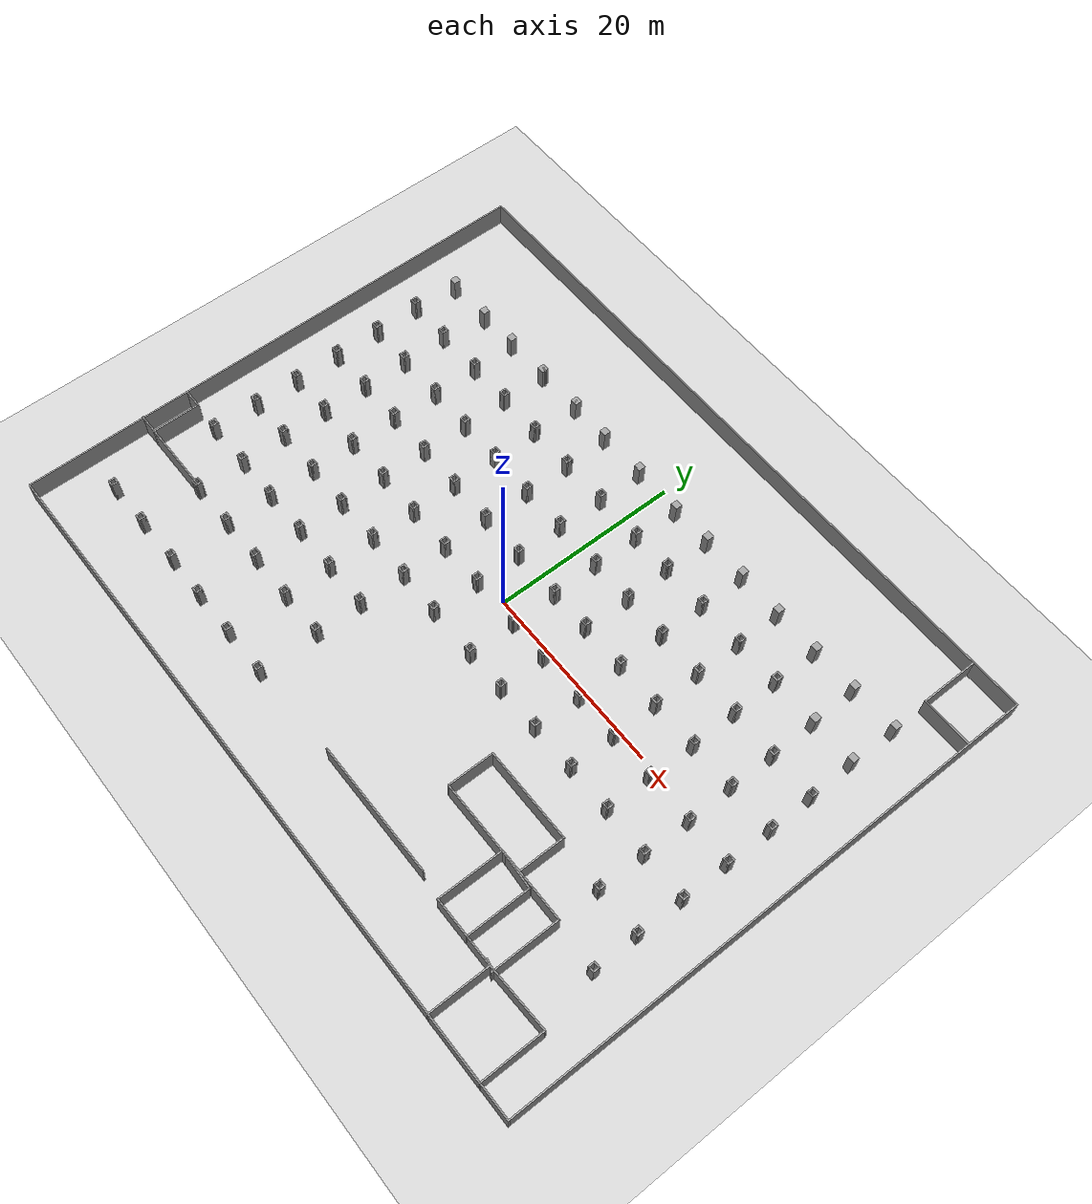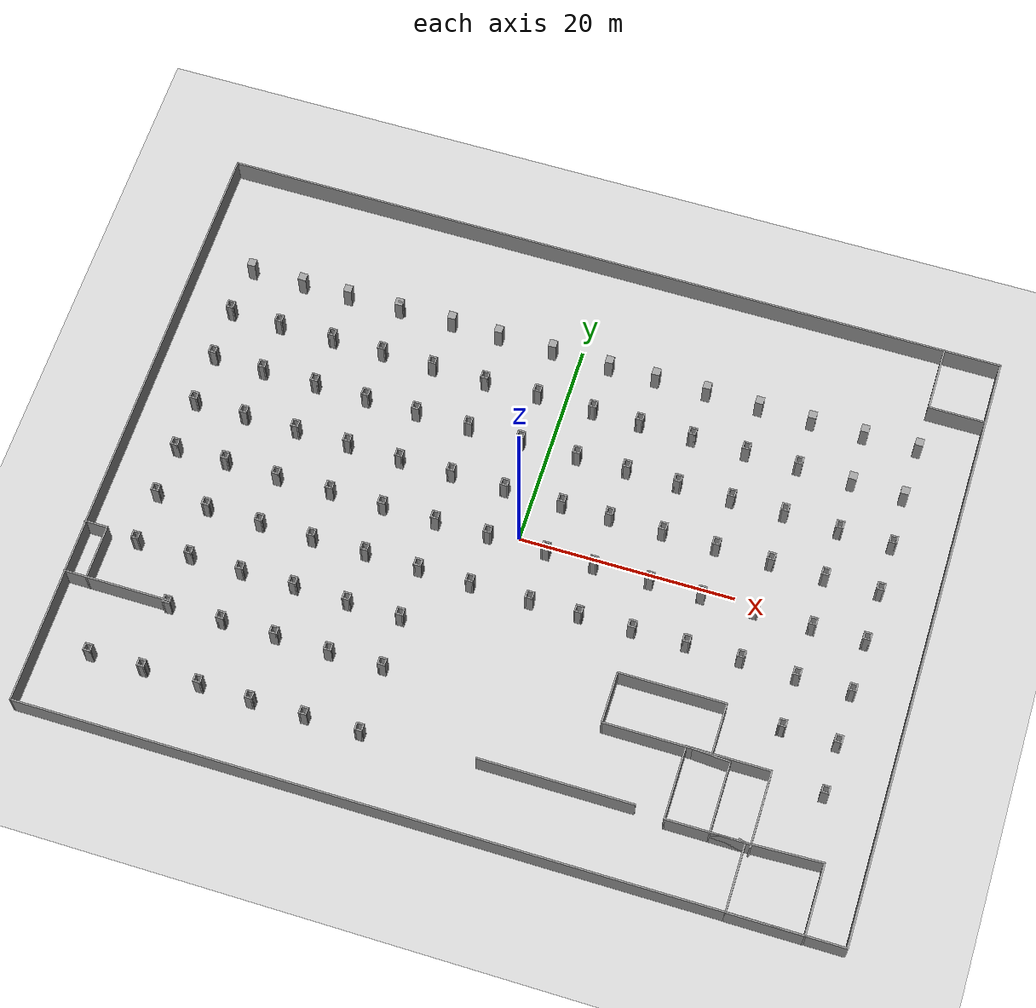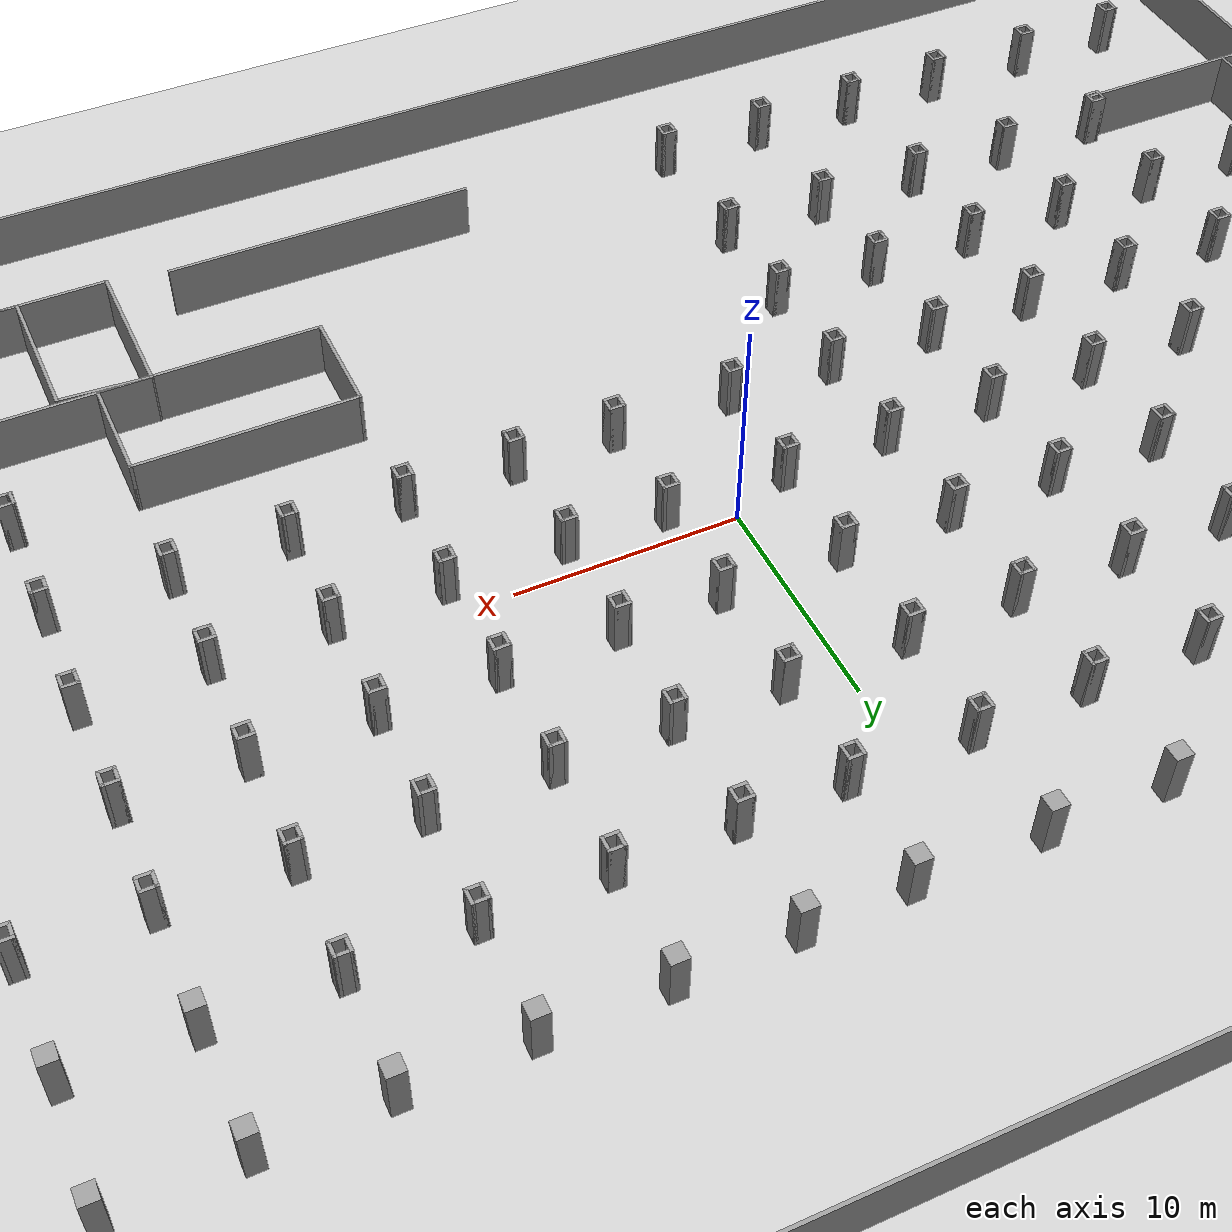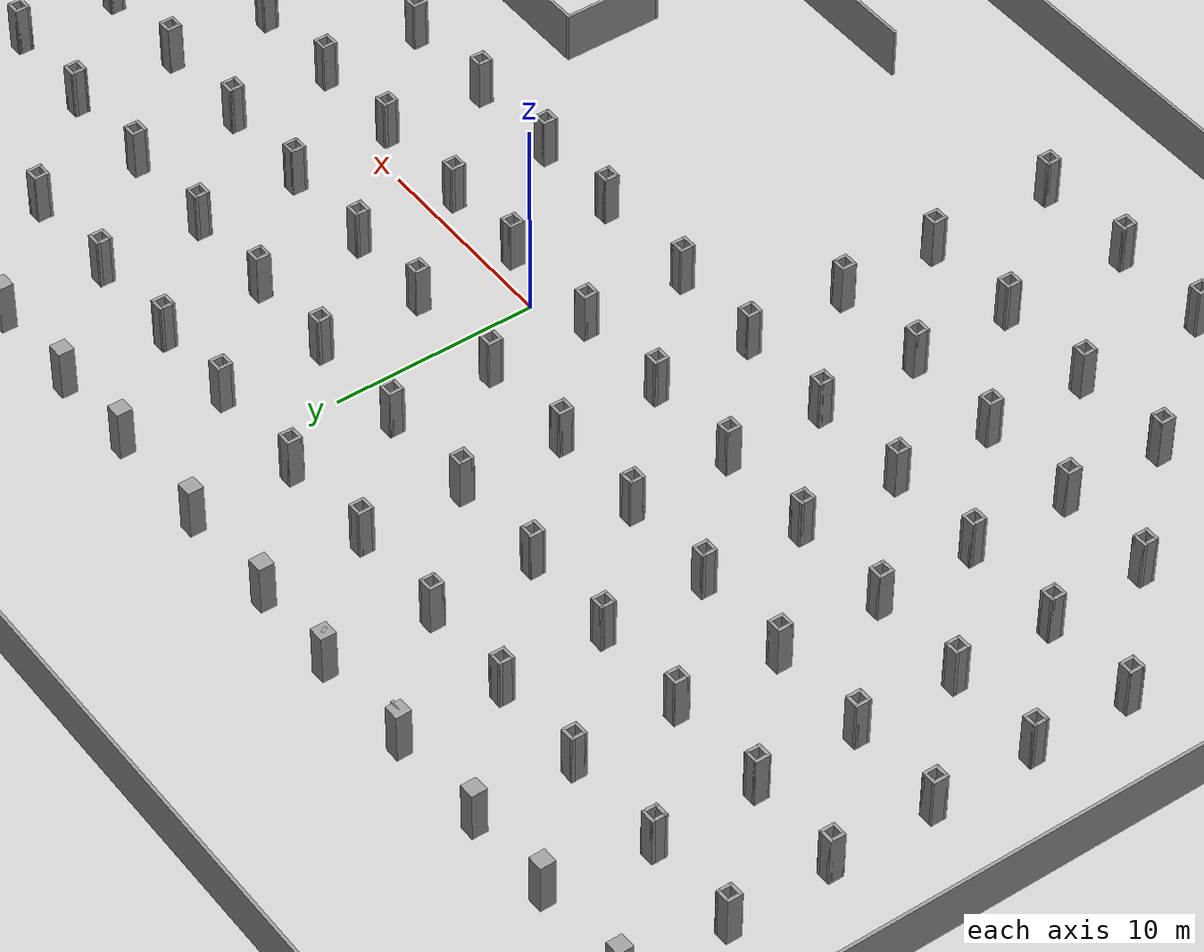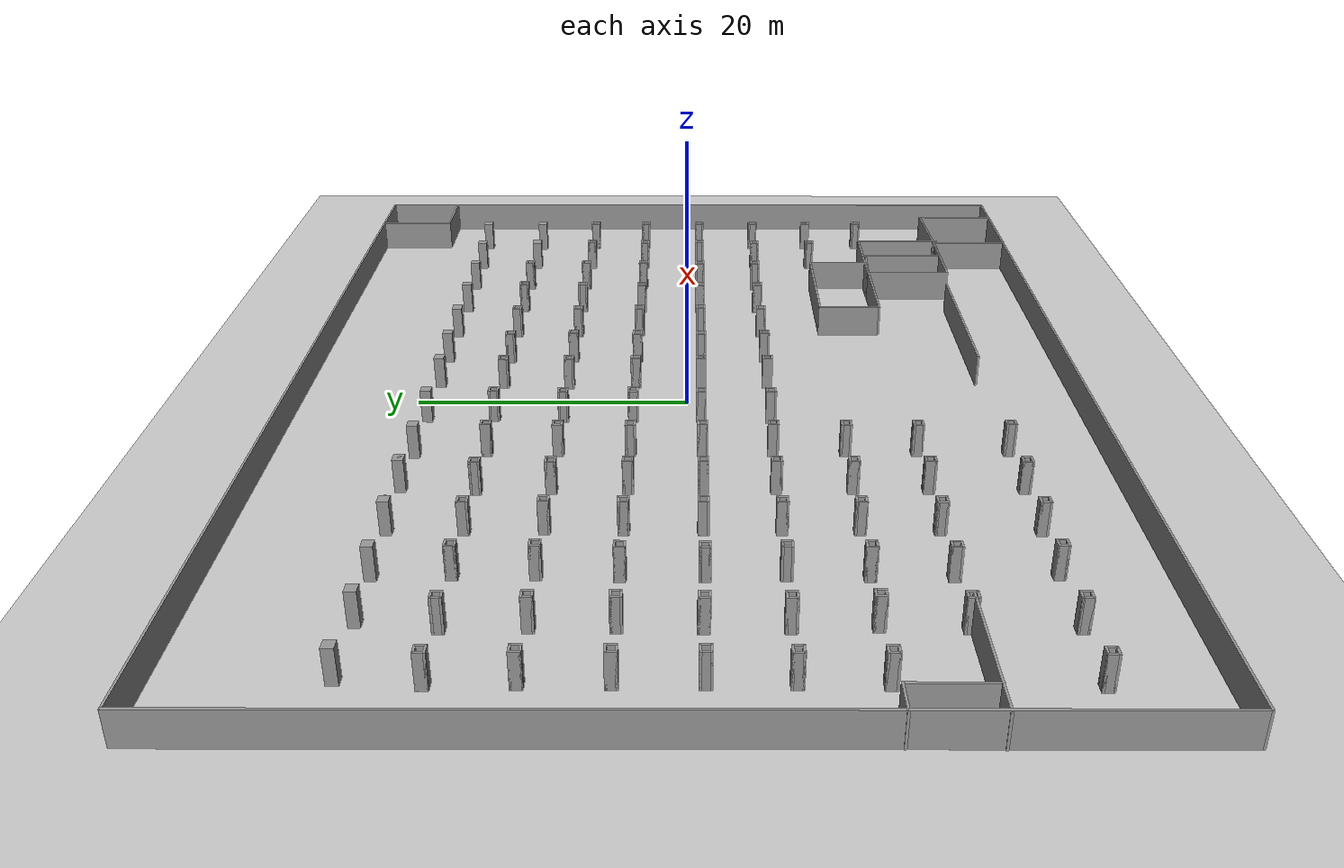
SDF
<sdf version="1.6">
 <world name="default">
  <light name="sun" type="directional">
   <pose>0 0 10 0 -0 0</pose>
   <diffuse>0.8 0.8 0.8 1</diffuse>
   <specular>0.2 0.2 0.2 1</specular>
   <attenuation>
    <range>1000</range>
    <constant>0.9</constant>
    <linear>0.01</linear>
    <quadratic>0.001</quadratic>
   </attenuation>
   <direction>-0.5 0.1 -0.9</direction>
  </light>
  <model name="ground_plane">
   <static>1</static>
   <link name="link">
    <collision name="collision">
     <geometry><plane><normal>0 0 1</normal><size>100 100</size></plane></geometry>
     <surface>
      <contact><collide_bitmask>65535</collide_bitmask></contact>
      <friction><ode><mu>100</mu><mu2>50</mu2></ode></friction>
     </surface>
    </collision>
    <visual name="visual">
     <cast_shadows>0</cast_shadows>
     <geometry><plane><normal>0 0 1</normal><size>100 100</size></plane></geometry>
     <material>
      <script><uri>file://media/materials/scripts/gazebo.material</uri><name>Gazebo/Grey</name></script>
     </material>
    </visual>
   </link>
  </model>
  <gravity>0 0 -9.8</gravity>
  <magnetic_field>6e-06 2.3e-05 -4.2e-05</magnetic_field>
  <atmosphere type="adiabatic"/>
  <physics name="default_physics" default="0" type="ode">
   <max_step_size>0.001</max_step_size>
   <real_time_factor>1</real_time_factor>
   <real_time_update_rate>1000</real_time_update_rate>
  </physics>
  <scene><ambient>0.4 0.4 0.4 1</ambient><background>0.7 0.7 0.7 1</background><shadows>1</shadows></scene>
  <audio><device>default</device></audio>
  <spherical_coordinates>
   <surface_model>EARTH_WGS84</surface_model>
   <latitude_deg>0</latitude_deg>
   <longitude_deg>0</longitude_deg>
   <elevation>0</elevation>
   <heading_deg>0</heading_deg>
  </spherical_coordinates>
  <model name="parking_area_big">
   <pose>0.030669 -0.012869 0 0 -0 0</pose>
   <link name="Wall_100">
    <collision name="Wall_100_Collision">
     <geometry><box><size>0.75 0.15 2.5</size></box></geometry>
     <pose>0 0 1.25 0 -0 0</pose>
    </collision>
    <visual name="Wall_100_Visual">
     <pose>0 0 1.25 0 -0 0</pose>
     <geometry><box><size>0.75 0.15 2.5</size></box></geometry>
     <material>
      <script><uri>file://media/materials/scripts/gazebo.material</uri><name>Gazebo/Grey</name></script>
      <ambient>1 1 1 1</ambient>
     </material>
     <meta><layer>0</layer></meta>
    </visual>
    <pose>27.266 -0.720336 0 0 -0 0</pose>
   </link>
   <link name="Wall_101">
    <collision name="Wall_101_Collision">
     <geometry><box><size>0.75 0.15 2.5</size></box></geometry>
     <pose>0 0 1.25 0 -0 0</pose>
    </collision>
    <visual name="Wall_101_Visual">
     <pose>0 0 1.25 0 -0 0</pose>
     <geometry><box><size>0.75 0.15 2.5</size></box></geometry>
     <material>
      <script><uri>file://media/materials/scripts/gazebo.material</uri><name>Gazebo/Grey</name></script>
      <ambient>1 1 1 1</ambient>
     </material>
     <meta><layer>0</layer></meta>
    </visual>
    <pose>27.566 -1.02034 0 0 -0 -1.5708</pose>
   </link>
   <link name="Wall_102">
    <collision name="Wall_102_Collision">
     <geometry><box><size>0.75 0.15 2.5</size></box></geometry>
     <pose>0 0 1.25 0 -0 0</pose>
    </collision>
    <visual name="Wall_102_Visual">
     <pose>0 0 1.25 0 -0 0</pose>
     <geometry><box><size>0.75 0.15 2.5</size></box></geometry>
     <material>
      <script><uri>file://media/materials/scripts/gazebo.material</uri><name>Gazebo/Grey</name></script>
      <ambient>1 1 1 1</ambient>
     </material>
     <meta><layer>0</layer></meta>
    </visual>
    <pose>27.266 -1.32034 0 0 -0 3.14159</pose>
   </link>
   <link name="Wall_103">
    <collision name="Wall_103_Collision">
     <geometry><box><size>0.75 0.15 2.5</size></box></geometry>
     <pose>0 0 1.25 0 -0 0</pose>
    </collision>
    <visual name="Wall_103_Visual">
     <pose>0 0 1.25 0 -0 0</pose>
     <geometry><box><size>0.75 0.15 2.5</size></box></geometry>
     <material>
      <script><uri>file://media/materials/scripts/gazebo.material</uri><name>Gazebo/Grey</name></script>
      <ambient>1 1 1 1</ambient>
     </material>
     <meta><layer>0</layer></meta>
    </visual>
    <pose>26.966 -1.02034 0 0 -0 1.5708</pose>
   </link>
   <link name="Wall_105">
    <collision name="Wall_105_Collision">
     <geometry><box><size>0.75 0.15 2.5</size></box></geometry>
     <pose>0 0 1.25 0 -0 0</pose>
    </collision>
    <visual name="Wall_105_Visual">
     <pose>0 0 1.25 0 -0 0</pose>
     <geometry><box><size>0.75 0.15 2.5</size></box></geometry>
     <material>
      <script><uri>file://media/materials/scripts/gazebo.material</uri><name>Gazebo/Grey</name></script>
      <ambient>1 1 1 1</ambient>
     </material>
     <meta><layer>0</layer></meta>
    </visual>
    <pose>32.1551 -0.719051 0 0 -0 0</pose>
   </link>
   <link name="Wall_106">
    <collision name="Wall_106_Collision">
     <geometry><box><size>0.75 0.15 2.5</size></box></geometry>
     <pose>0 0 1.25 0 -0 0</pose>
    </collision>
    <visual name="Wall_106_Visual">
     <pose>0 0 1.25 0 -0 0</pose>
     <geometry><box><size>0.75 0.15 2.5</size></box></geometry>
     <material>
      <script><uri>file://media/materials/scripts/gazebo.material</uri><name>Gazebo/Grey</name></script>
      <ambient>1 1 1 1</ambient>
     </material>
     <meta><layer>0</layer></meta>
    </visual>
    <pose>32.4551 -1.01905 0 0 -0 -1.5708</pose>
   </link>
   <link name="Wall_107">
    <collision name="Wall_107_Collision">
     <geometry><box><size>0.75 0.15 2.5</size></box></geometry>
     <pose>0 0 1.25 0 -0 0</pose>
    </collision>
    <visual name="Wall_107_Visual">
     <pose>0 0 1.25 0 -0 0</pose>
     <geometry><box><size>0.75 0.15 2.5</size></box></geometry>
     <material>
      <script><uri>file://media/materials/scripts/gazebo.material</uri><name>Gazebo/Grey</name></script>
      <ambient>1 1 1 1</ambient>
     </material>
     <meta><layer>0</layer></meta>
    </visual>
    <pose>32.1551 -1.31905 0 0 -0 3.14159</pose>
   </link>
   <link name="Wall_108">
    <collision name="Wall_108_Collision">
     <geometry><box><size>0.75 0.15 2.5</size></box></geometry>
     <pose>0 0 1.25 0 -0 0</pose>
    </collision>
    <visual name="Wall_108_Visual">
     <pose>0 0 1.25 0 -0 0</pose>
     <geometry><box><size>0.75 0.15 2.5</size></box></geometry>
     <material>
      <script><uri>file://media/materials/scripts/gazebo.material</uri><name>Gazebo/Grey</name></script>
      <ambient>1 1 1 1</ambient>
     </material>
     <meta><layer>0</layer></meta>
    </visual>
    <pose>31.8551 -1.01905 0 0 -0 1.5708</pose>
   </link>
   <link name="Wall_110">
    <collision name="Wall_110_Collision">
     <geometry><box><size>0.75 0.15 2.5</size></box></geometry>
     <pose>0 0 1.25 0 -0 0</pose>
    </collision>
    <visual name="Wall_110_Visual">
     <pose>0 0 1.25 0 -0 0</pose>
     <geometry><box><size>0.75 0.15 2.5</size></box></geometry>
     <material>
      <script><uri>file://media/materials/scripts/gazebo.material</uri><name>Gazebo/Grey</name></script>
      <ambient>1 1 1 1</ambient>
     </material>
     <meta><layer>0</layer></meta>
    </visual>
    <pose>27.1351 -5.75905 0 0 -0 0</pose>
   </link>
   <link name="Wall_111">
    <collision name="Wall_111_Collision">
     <geometry><box><size>0.75 0.15 2.5</size></box></geometry>
     <pose>0 0 1.25 0 -0 0</pose>
    </collision>
    <visual name="Wall_111_Visual">
     <pose>0 0 1.25 0 -0 0</pose>
     <geometry><box><size>0.75 0.15 2.5</size></box></geometry>
     <material>
      <script><uri>file://media/materials/scripts/gazebo.material</uri><name>Gazebo/Grey</name></script>
      <ambient>1 1 1 1</ambient>
     </material>
     <meta><layer>0</layer></meta>
    </visual>
    <pose>27.4351 -6.05905 0 0 -0 -1.5708</pose>
   </link>
   <link name="Wall_112">
    <collision name="Wall_112_Collision">
     <geometry><box><size>0.75 0.15 2.5</size></box></geometry>
     <pose>0 0 1.25 0 -0 0</pose>
    </collision>
    <visual name="Wall_112_Visual">
     <pose>0 0 1.25 0 -0 0</pose>
     <geometry><box><size>0.75 0.15 2.5</size></box></geometry>
     <material>
      <script><uri>file://media/materials/scripts/gazebo.material</uri><name>Gazebo/Grey</name></script>
      <ambient>1 1 1 1</ambient>
     </material>
     <meta><layer>0</layer></meta>
    </visual>
    <pose>27.1351 -6.35905 0 0 -0 3.14159</pose>
   </link>
   <link name="Wall_113">
    <collision name="Wall_113_Collision">
     <geometry><box><size>0.75 0.15 2.5</size></box></geometry>
     <pose>0 0 1.25 0 -0 0</pose>
    </collision>
    <visual name="Wall_113_Visual">
     <pose>0 0 1.25 0 -0 0</pose>
     <geometry><box><size>0.75 0.15 2.5</size></box></geometry>
     <material>
      <script><uri>file://media/materials/scripts/gazebo.material</uri><name>Gazebo/Grey</name></script>
      <ambient>1 1 1 1</ambient>
     </material>
     <meta><layer>0</layer></meta>
    </visual>
    <pose>26.8351 -6.05905 0 0 -0 1.5708</pose>
   </link>
   <link name="Wall_115">
    <collision name="Wall_115_Collision">
     <geometry><box><size>0.75 0.15 2.5</size></box></geometry>
     <pose>0 0 1.25 0 -0 0</pose>
    </collision>
    <visual name="Wall_115_Visual">
     <pose>0 0 1.25 0 -0 0</pose>
     <geometry><box><size>0.75 0.15 2.5</size></box></geometry>
     <material>
      <script><uri>file://media/materials/scripts/gazebo.material</uri><name>Gazebo/Grey</name></script>
      <ambient>1 1 1 1</ambient>
     </material>
     <meta><layer>0</layer></meta>
    </visual>
    <pose>32.1351 -5.75905 0 0 -0 0</pose>
   </link>
   <link name="Wall_116">
    <collision name="Wall_116_Collision">
     <geometry><box><size>0.75 0.15 2.5</size></box></geometry>
     <pose>0 0 1.25 0 -0 0</pose>
    </collision>
    <visual name="Wall_116_Visual">
     <pose>0 0 1.25 0 -0 0</pose>
     <geometry><box><size>0.75 0.15 2.5</size></box></geometry>
     <material>
      <script><uri>file://media/materials/scripts/gazebo.material</uri><name>Gazebo/Grey</name></script>
      <ambient>1 1 1 1</ambient>
     </material>
     <meta><layer>0</layer></meta>
    </visual>
    <pose>32.4351 -6.05905 0 0 -0 -1.5708</pose>
   </link>
   <link name="Wall_117">
    <collision name="Wall_117_Collision">
     <geometry><box><size>0.75 0.15 2.5</size></box></geometry>
     <pose>0 0 1.25 0 -0 0</pose>
    </collision>
    <visual name="Wall_117_Visual">
     <pose>0 0 1.25 0 -0 0</pose>
     <geometry><box><size>0.75 0.15 2.5</size></box></geometry>
     <material>
      <script><uri>file://media/materials/scripts/gazebo.material</uri><name>Gazebo/Grey</name></script>
      <ambient>1 1 1 1</ambient>
     </material>
     <meta><layer>0</layer></meta>
    </visual>
    <pose>32.1351 -6.35905 0 0 -0 3.14159</pose>
   </link>
   <link name="Wall_118">
    <collision name="Wall_118_Collision">
     <geometry><box><size>0.75 0.15 2.5</size></box></geometry>
     <pose>0 0 1.25 0 -0 0</pose>
    </collision>
    <visual name="Wall_118_Visual">
     <pose>0 0 1.25 0 -0 0</pose>
     <geometry><box><size>0.75 0.15 2.5</size></box></geometry>
     <material>
      <script><uri>file://media/materials/scripts/gazebo.material</uri><name>Gazebo/Grey</name></script>
      <ambient>1 1 1 1</ambient>
     </material>
     <meta><layer>0</layer></meta>
    </visual>
    <pose>31.8351 -6.05905 0 0 -0 1.5708</pose>
   </link>
   <link name="Wall_120">
    <collision name="Wall_120_Collision">
     <geometry><box><size>0.75 0.15 2.5</size></box></geometry>
     <pose>0 0 1.25 0 -0 0</pose>
    </collision>
    <visual name="Wall_120_Visual">
     <pose>0 0 1.25 0 -0 0</pose>
     <geometry><box><size>0.75 0.15 2.5</size></box></geometry>
     <material>
      <script><uri>file://media/materials/scripts/gazebo.material</uri><name>Gazebo/Grey</name></script>
      <ambient>1 1 1 1</ambient>
     </material>
     <meta><layer>0</layer></meta>
    </visual>
    <pose>27.1351 -10.7591 0 0 -0 0</pose>
   </link>
   <link name="Wall_121">
    <collision name="Wall_121_Collision">
     <geometry><box><size>0.75 0.15 2.5</size></box></geometry>
     <pose>0 0 1.25 0 -0 0</pose>
    </collision>
    <visual name="Wall_121_Visual">
     <pose>0 0 1.25 0 -0 0</pose>
     <geometry><box><size>0.75 0.15 2.5</size></box></geometry>
     <material>
      <script><uri>file://media/materials/scripts/gazebo.material</uri><name>Gazebo/Grey</name></script>
      <ambient>1 1 1 1</ambient>
     </material>
     <meta><layer>0</layer></meta>
    </visual>
    <pose>27.4351 -11.0591 0 0 -0 -1.5708</pose>
   </link>
   <link name="Wall_122">
    <collision name="Wall_122_Collision">
     <geometry><box><size>0.640408 0.15 2.5</size></box></geometry>
     <pose>0 0 1.25 0 -0 0</pose>
    </collision>
    <visual name="Wall_122_Visual">
     <pose>0 0 1.25 0 -0 0</pose>
     <geometry><box><size>0.640408 0.15 2.5</size></box></geometry>
     <material>
      <script><uri>file://media/materials/scripts/gazebo.material</uri><name>Gazebo/Grey</name></script>
      <ambient>1 1 1 1</ambient>
     </material>
     <meta><layer>0</layer></meta>
    </visual>
    <pose>27.19 -11.3491 0 0 -0 3.1008</pose>
   </link>
   <link name="Wall_123">
    <collision name="Wall_123_Collision">
     <geometry><box><size>0.25 0.15 2.5</size></box></geometry>
     <pose>0 0 1.25 0 -0 0</pose>
    </collision>
    <visual name="Wall_123_Visual">
     <pose>0 0 1.25 0 -0 0</pose>
     <geometry><box><size>0.25 0.15 2.5</size></box></geometry>
     <material>
      <script><uri>file://media/materials/scripts/gazebo.material</uri><name>Gazebo/Grey</name></script>
      <ambient>1 1 1 1</ambient>
     </material>
     <meta><layer>0</layer></meta>
    </visual>
    <pose>26.8751 -11.3391 0 0 -0 3.14159</pose>
   </link>
   <link name="Wall_124">
    <collision name="Wall_124_Collision">
     <geometry><box><size>0.15 0.15 2.5</size></box></geometry>
     <pose>0 0 1.25 0 -0 0</pose>
    </collision>
    <visual name="Wall_124_Visual">
     <pose>0 0 1.25 0 -0 0</pose>
     <geometry><box><size>0.15 0.15 2.5</size></box></geometry>
     <material>
      <script><uri>file://media/materials/scripts/gazebo.material</uri><name>Gazebo/Grey</name></script>
      <ambient>1 1 1 1</ambient>
     </material>
     <meta><layer>0</layer></meta>
    </visual>
    <pose>26.8451 -11.3391 0 0 -0 0</pose>
   </link>
   <link name="Wall_126">
    <collision name="Wall_126_Collision">
     <geometry><box><size>0.730086 0.15 2.5</size></box></geometry>
     <pose>0 0 1.25 0 -0 0</pose>
    </collision>
    <visual name="Wall_126_Visual">
     <pose>0 0 1.25 0 -0 0</pose>
     <geometry><box><size>0.730086 0.15 2.5</size></box></geometry>
     <material>
      <script><uri>file://media/materials/scripts/gazebo.material</uri><name>Gazebo/Grey</name></script>
      <ambient>1 1 1 1</ambient>
     </material>
     <meta><layer>0</layer></meta>
    </visual>
    <pose>26.8401 -11.0491 0 0 -0 -1.55356</pose>
   </link>
   <link name="Wall_128">
    <collision name="Wall_128_Collision">
     <geometry><box><size>0.75 0.15 2.5</size></box></geometry>
     <pose>0 0 1.25 0 -0 0</pose>
    </collision>
    <visual name="Wall_128_Visual">
     <pose>0 0 1.25 0 -0 0</pose>
     <geometry><box><size>0.75 0.15 2.5</size></box></geometry>
     <material>
      <script><uri>file://media/materials/scripts/gazebo.material</uri><name>Gazebo/Grey</name></script>
      <ambient>1 1 1 1</ambient>
     </material>
     <meta><layer>0</layer></meta>
    </visual>
    <pose>32.1151 -10.7391 0 0 -0 0</pose>
   </link>
   <link name="Wall_129">
    <collision name="Wall_129_Collision">
     <geometry><box><size>0.75 0.15 2.5</size></box></geometry>
     <pose>0 0 1.25 0 -0 0</pose>
    </collision>
    <visual name="Wall_129_Visual">
     <pose>0 0 1.25 0 -0 0</pose>
     <geometry><box><size>0.75 0.15 2.5</size></box></geometry>
     <material>
      <script><uri>file://media/materials/scripts/gazebo.material</uri><name>Gazebo/Grey</name></script>
      <ambient>1 1 1 1</ambient>
     </material>
     <meta><layer>0</layer></meta>
    </visual>
    <pose>32.4151 -11.0391 0 0 -0 -1.5708</pose>
   </link>
   <link name="Wall_130">
    <collision name="Wall_130_Collision">
     <geometry><box><size>0.75 0.15 2.5</size></box></geometry>
     <pose>0 0 1.25 0 -0 0</pose>
    </collision>
    <visual name="Wall_130_Visual">
     <pose>0 0 1.25 0 -0 0</pose>
     <geometry><box><size>0.75 0.15 2.5</size></box></geometry>
     <material>
      <script><uri>file://media/materials/scripts/gazebo.material</uri><name>Gazebo/Grey</name></script>
      <ambient>1 1 1 1</ambient>
     </material>
     <meta><layer>0</layer></meta>
    </visual>
    <pose>32.1151 -11.3391 0 0 -0 3.14159</pose>
   </link>
   <link name="Wall_131">
    <collision name="Wall_131_Collision">
     <geometry><box><size>0.75 0.15 2.5</size></box></geometry>
     <pose>0 0 1.25 0 -0 0</pose>
    </collision>
    <visual name="Wall_131_Visual">
     <pose>0 0 1.25 0 -0 0</pose>
     <geometry><box><size>0.75 0.15 2.5</size></box></geometry>
     <material>
      <script><uri>file://media/materials/scripts/gazebo.material</uri><name>Gazebo/Grey</name></script>
      <ambient>1 1 1 1</ambient>
     </material>
     <meta><layer>0</layer></meta>
    </visual>
    <pose>31.815 -11.0391 0 0 -0 1.5708</pose>
   </link>
   <link name="Wall_134">
    <collision name="Wall_134_Collision">
     <geometry><box><size>0.75 0.15 2.5</size></box></geometry>
     <pose>0 0 1.25 0 -0 0</pose>
    </collision>
    <visual name="Wall_134_Visual">
     <pose>0 0 1.25 0 -0 0</pose>
     <geometry><box><size>0.75 0.15 2.5</size></box></geometry>
     <material>
      <script><uri>file://media/materials/scripts/gazebo.material</uri><name>Gazebo/Grey</name></script>
      <ambient>1 1 1 1</ambient>
     </material>
     <meta><layer>0</layer></meta>
    </visual>
    <pose>32.1751 -15.5391 0 0 -0 0</pose>
   </link>
   <link name="Wall_135">
    <collision name="Wall_135_Collision">
     <geometry><box><size>0.75 0.15 2.5</size></box></geometry>
     <pose>0 0 1.25 0 -0 0</pose>
    </collision>
    <visual name="Wall_135_Visual">
     <pose>0 0 1.25 0 -0 0</pose>
     <geometry><box><size>0.75 0.15 2.5</size></box></geometry>
     <material>
      <script><uri>file://media/materials/scripts/gazebo.material</uri><name>Gazebo/Grey</name></script>
      <ambient>1 1 1 1</ambient>
     </material>
     <meta><layer>0</layer></meta>
    </visual>
    <pose>32.4751 -15.8391 0 0 -0 -1.5708</pose>
   </link>
   <link name="Wall_136">
    <collision name="Wall_136_Collision">
     <geometry><box><size>0.75 0.15 2.5</size></box></geometry>
     <pose>0 0 1.25 0 -0 0</pose>
    </collision>
    <visual name="Wall_136_Visual">
     <pose>0 0 1.25 0 -0 0</pose>
     <geometry><box><size>0.75 0.15 2.5</size></box></geometry>
     <material>
      <script><uri>file://media/materials/scripts/gazebo.material</uri><name>Gazebo/Grey</name></script>
      <ambient>1 1 1 1</ambient>
     </material>
     <meta><layer>0</layer></meta>
    </visual>
    <pose>32.1751 -16.1391 0 0 -0 3.14159</pose>
   </link>
   <link name="Wall_137">
    <collision name="Wall_137_Collision">
     <geometry><box><size>0.75 0.15 2.5</size></box></geometry>
     <pose>0 0 1.25 0 -0 0</pose>
    </collision>
    <visual name="Wall_137_Visual">
     <pose>0 0 1.25 0 -0 0</pose>
     <geometry><box><size>0.75 0.15 2.5</size></box></geometry>
     <material>
      <script><uri>file://media/materials/scripts/gazebo.material</uri><name>Gazebo/Grey</name></script>
      <ambient>1 1 1 1</ambient>
     </material>
     <meta><layer>0</layer></meta>
    </visual>
    <pose>31.8751 -15.8391 0 0 -0 1.5708</pose>
   </link>
   <link name="Wall_139">
    <collision name="Wall_139_Collision">
     <geometry><box><size>10 0.15 2.5</size></box></geometry>
     <pose>0 0 1.25 0 -0 0</pose>
    </collision>
    <visual name="Wall_139_Visual">
     <pose>0 0 1.25 0 -0 0</pose>
     <geometry><box><size>10 0.15 2.5</size></box></geometry>
     <material>
      <script><uri>file://media/materials/scripts/gazebo.material</uri><name>Gazebo/Grey</name></script>
      <ambient>1 1 1 1</ambient>
     </material>
     <meta><layer>0</layer></meta>
    </visual>
    <pose>17.1385 -10.7965 0 0 -0 0</pose>
   </link>
   <link name="Wall_140">
    <collision name="Wall_140_Collision">
     <geometry><box><size>5 0.15 2.5</size></box></geometry>
     <pose>0 0 1.25 0 -0 0</pose>
    </collision>
    <visual name="Wall_140_Visual">
     <pose>0 0 1.25 0 -0 0</pose>
     <geometry><box><size>5 0.15 2.5</size></box></geometry>
     <material>
      <script><uri>file://media/materials/scripts/gazebo.material</uri><name>Gazebo/Grey</name></script>
      <ambient>1 1 1 1</ambient>
     </material>
     <meta><layer>0</layer></meta>
    </visual>
    <pose>22.0635 -13.2215 0 0 -0 -1.5708</pose>
   </link>
   <link name="Wall_141">
    <collision name="Wall_141_Collision">
     <geometry><box><size>10 0.15 2.5</size></box></geometry>
     <pose>0 0 1.25 0 -0 0</pose>
    </collision>
    <visual name="Wall_141_Visual">
     <pose>0 0 1.25 0 -0 0</pose>
     <geometry><box><size>10 0.15 2.5</size></box></geometry>
     <material>
      <script><uri>file://media/materials/scripts/gazebo.material</uri><name>Gazebo/Grey</name></script>
      <ambient>1 1 1 1</ambient>
     </material>
     <meta><layer>0</layer></meta>
    </visual>
    <pose>17.1385 -15.6465 0 0 -0 3.14159</pose>
   </link>
   <link name="Wall_142">
    <collision name="Wall_142_Collision">
     <geometry><box><size>5 0.15 2.5</size></box></geometry>
     <pose>0 0 1.25 0 -0 0</pose>
    </collision>
    <visual name="Wall_142_Visual">
     <pose>0 0 1.25 0 -0 0</pose>
     <geometry><box><size>5 0.15 2.5</size></box></geometry>
     <material>
      <script><uri>file://media/materials/scripts/gazebo.material</uri><name>Gazebo/Grey</name></script>
      <ambient>1 1 1 1</ambient>
     </material>
     <meta><layer>0</layer></meta>
    </visual>
    <pose>12.2135 -13.2215 0 0 -0 1.5708</pose>
   </link>
   <link name="Wall_144">
    <collision name="Wall_144_Collision">
     <geometry><box><size>0.75 0.15 2.5</size></box></geometry>
     <pose>0 0 1.25 0 -0 0</pose>
    </collision>
    <visual name="Wall_144_Visual">
     <pose>0 0 1.25 0 -0 0</pose>
     <geometry><box><size>0.75 0.15 2.5</size></box></geometry>
     <material>
      <script><uri>file://media/materials/scripts/gazebo.material</uri><name>Gazebo/Grey</name></script>
      <ambient>1 1 1 1</ambient>
     </material>
     <meta><layer>0</layer></meta>
    </visual>
    <pose>2.74065 -5.725 0 0 -0 0</pose>
   </link>
   <link name="Wall_145">
    <collision name="Wall_145_Collision">
     <geometry><box><size>0.75 0.15 2.5</size></box></geometry>
     <pose>0 0 1.25 0 -0 0</pose>
    </collision>
    <visual name="Wall_145_Visual">
     <pose>0 0 1.25 0 -0 0</pose>
     <geometry><box><size>0.75 0.15 2.5</size></box></geometry>
     <material>
      <script><uri>file://media/materials/scripts/gazebo.material</uri><name>Gazebo/Grey</name></script>
      <ambient>1 1 1 1</ambient>
     </material>
     <meta><layer>0</layer></meta>
    </visual>
    <pose>3.04065 -6.025 0 0 -0 -1.5708</pose>
   </link>
   <link name="Wall_146">
    <collision name="Wall_146_Collision">
     <geometry><box><size>0.75 0.15 2.5</size></box></geometry>
     <pose>0 0 1.25 0 -0 0</pose>
    </collision>
    <visual name="Wall_146_Visual">
     <pose>0 0 1.25 0 -0 0</pose>
     <geometry><box><size>0.75 0.15 2.5</size></box></geometry>
     <material>
      <script><uri>file://media/materials/scripts/gazebo.material</uri><name>Gazebo/Grey</name></script>
      <ambient>1 1 1 1</ambient>
     </material>
     <meta><layer>0</layer></meta>
    </visual>
    <pose>2.74065 -6.325 0 0 -0 3.14159</pose>
   </link>
   <link name="Wall_147">
    <collision name="Wall_147_Collision">
     <geometry><box><size>0.75 0.15 2.5</size></box></geometry>
     <pose>0 0 1.25 0 -0 0</pose>
    </collision>
    <visual name="Wall_147_Visual">
     <pose>0 0 1.25 0 -0 0</pose>
     <geometry><box><size>0.75 0.15 2.5</size></box></geometry>
     <material>
      <script><uri>file://media/materials/scripts/gazebo.material</uri><name>Gazebo/Grey</name></script>
      <ambient>1 1 1 1</ambient>
     </material>
     <meta><layer>0</layer></meta>
    </visual>
    <pose>2.44064 -6.025 0 0 -0 1.5708</pose>
   </link>
   <link name="Wall_152">
    <collision name="Wall_152_Collision">
     <geometry><box><size>0.75 0.15 2.5</size></box></geometry>
     <pose>0 0 1.25 0 -0 0</pose>
    </collision>
    <visual name="Wall_152_Visual">
     <pose>0 0 1.25 0 -0 0</pose>
     <geometry><box><size>0.75 0.15 2.5</size></box></geometry>
     <material>
      <script><uri>file://media/materials/scripts/gazebo.material</uri><name>Gazebo/Grey</name></script>
      <ambient>1 1 1 1</ambient>
     </material>
     <meta><layer>0</layer></meta>
    </visual>
    <pose>2.71765 -0.688004 0 0 -0 0</pose>
   </link>
   <link name="Wall_153">
    <collision name="Wall_153_Collision">
     <geometry><box><size>0.75 0.15 2.5</size></box></geometry>
     <pose>0 0 1.25 0 -0 0</pose>
    </collision>
    <visual name="Wall_153_Visual">
     <pose>0 0 1.25 0 -0 0</pose>
     <geometry><box><size>0.75 0.15 2.5</size></box></geometry>
     <material>
      <script><uri>file://media/materials/scripts/gazebo.material</uri><name>Gazebo/Grey</name></script>
      <ambient>1 1 1 1</ambient>
     </material>
     <meta><layer>0</layer></meta>
    </visual>
    <pose>3.01764 -0.988004 0 0 -0 -1.5708</pose>
   </link>
   <link name="Wall_154">
    <collision name="Wall_154_Collision">
     <geometry><box><size>0.75 0.15 2.5</size></box></geometry>
     <pose>0 0 1.25 0 -0 0</pose>
    </collision>
    <visual name="Wall_154_Visual">
     <pose>0 0 1.25 0 -0 0</pose>
     <geometry><box><size>0.75 0.15 2.5</size></box></geometry>
     <material>
      <script><uri>file://media/materials/scripts/gazebo.material</uri><name>Gazebo/Grey</name></script>
      <ambient>1 1 1 1</ambient>
     </material>
     <meta><layer>0</layer></meta>
    </visual>
    <pose>2.71765 -1.288 0 0 -0 3.14159</pose>
   </link>
   <link name="Wall_155">
    <collision name="Wall_155_Collision">
     <geometry><box><size>0.75 0.15 2.5</size></box></geometry>
     <pose>0 0 1.25 0 -0 0</pose>
    </collision>
    <visual name="Wall_155_Visual">
     <pose>0 0 1.25 0 -0 0</pose>
     <geometry><box><size>0.75 0.15 2.5</size></box></geometry>
     <material>
      <script><uri>file://media/materials/scripts/gazebo.material</uri><name>Gazebo/Grey</name></script>
      <ambient>1 1 1 1</ambient>
     </material>
     <meta><layer>0</layer></meta>
    </visual>
    <pose>2.41764 -0.988004 0 0 -0 1.5708</pose>
   </link>
   <link name="Wall_163">
    <collision name="Wall_163_Collision">
     <geometry><box><size>0.75 0.15 2.5</size></box></geometry>
     <pose>0 0 1.25 0 -0 0</pose>
    </collision>
    <visual name="Wall_163_Visual">
     <pose>0 0 1.25 0 -0 0</pose>
     <geometry><box><size>0.75 0.15 2.5</size></box></geometry>
     <material>
      <script><uri>file://media/materials/scripts/gazebo.material</uri><name>Gazebo/Grey</name></script>
      <ambient>1 1 1 1</ambient>
     </material>
     <meta><layer>0</layer></meta>
    </visual>
    <pose>7.17964 -0.734004 0 0 -0 0</pose>
   </link>
   <link name="Wall_164">
    <collision name="Wall_164_Collision">
     <geometry><box><size>0.75 0.15 2.5</size></box></geometry>
     <pose>0 0 1.25 0 -0 0</pose>
    </collision>
    <visual name="Wall_164_Visual">
     <pose>0 0 1.25 0 -0 0</pose>
     <geometry><box><size>0.75 0.15 2.5</size></box></geometry>
     <material>
      <script><uri>file://media/materials/scripts/gazebo.material</uri><name>Gazebo/Grey</name></script>
      <ambient>1 1 1 1</ambient>
     </material>
     <meta><layer>0</layer></meta>
    </visual>
    <pose>7.47964 -1.034 0 0 -0 -1.5708</pose>
   </link>
   <link name="Wall_165">
    <collision name="Wall_165_Collision">
     <geometry><box><size>0.75 0.15 2.5</size></box></geometry>
     <pose>0 0 1.25 0 -0 0</pose>
    </collision>
    <visual name="Wall_165_Visual">
     <pose>0 0 1.25 0 -0 0</pose>
     <geometry><box><size>0.75 0.15 2.5</size></box></geometry>
     <material>
      <script><uri>file://media/materials/scripts/gazebo.material</uri><name>Gazebo/Grey</name></script>
      <ambient>1 1 1 1</ambient>
     </material>
     <meta><layer>0</layer></meta>
    </visual>
    <pose>7.17964 -1.334 0 0 -0 3.14159</pose>
   </link>
   <link name="Wall_166">
    <collision name="Wall_166_Collision">
     <geometry><box><size>0.75 0.15 2.5</size></box></geometry>
     <pose>0 0 1.25 0 -0 0</pose>
    </collision>
    <visual name="Wall_166_Visual">
     <pose>0 0 1.25 0 -0 0</pose>
     <geometry><box><size>0.75 0.15 2.5</size></box></geometry>
     <material>
      <script><uri>file://media/materials/scripts/gazebo.material</uri><name>Gazebo/Grey</name></script>
      <ambient>1 1 1 1</ambient>
     </material>
     <meta><layer>0</layer></meta>
    </visual>
    <pose>6.87965 -1.034 0 0 -0 1.5708</pose>
   </link>
   <link name="Wall_168">
    <collision name="Wall_168_Collision">
     <geometry><box><size>0.75 0.15 2.5</size></box></geometry>
     <pose>0 0 1.25 0 -0 0</pose>
    </collision>
    <visual name="Wall_168_Visual">
     <pose>0 0 1.25 0 -0 0</pose>
     <geometry><box><size>0.75 0.15 2.5</size></box></geometry>
     <material>
      <script><uri>file://media/materials/scripts/gazebo.material</uri><name>Gazebo/Grey</name></script>
      <ambient>1 1 1 1</ambient>
     </material>
     <meta><layer>0</layer></meta>
    </visual>
    <pose>12.3546 -0.734004 0 0 -0 0</pose>
   </link>
   <link name="Wall_169">
    <collision name="Wall_169_Collision">
     <geometry><box><size>0.75 0.15 2.5</size></box></geometry>
     <pose>0 0 1.25 0 -0 0</pose>
    </collision>
    <visual name="Wall_169_Visual">
     <pose>0 0 1.25 0 -0 0</pose>
     <geometry><box><size>0.75 0.15 2.5</size></box></geometry>
     <material>
      <script><uri>file://media/materials/scripts/gazebo.material</uri><name>Gazebo/Grey</name></script>
      <ambient>1 1 1 1</ambient>
     </material>
     <meta><layer>0</layer></meta>
    </visual>
    <pose>12.6546 -1.034 0 0 -0 -1.5708</pose>
   </link>
   <link name="Wall_170">
    <collision name="Wall_170_Collision">
     <geometry><box><size>0.75 0.15 2.5</size></box></geometry>
     <pose>0 0 1.25 0 -0 0</pose>
    </collision>
    <visual name="Wall_170_Visual">
     <pose>0 0 1.25 0 -0 0</pose>
     <geometry><box><size>0.75 0.15 2.5</size></box></geometry>
     <material>
      <script><uri>file://media/materials/scripts/gazebo.material</uri><name>Gazebo/Grey</name></script>
      <ambient>1 1 1 1</ambient>
     </material>
     <meta><layer>0</layer></meta>
    </visual>
    <pose>12.3546 -1.334 0 0 -0 3.14159</pose>
   </link>
   <link name="Wall_171">
    <collision name="Wall_171_Collision">
     <geometry><box><size>0.75 0.15 2.5</size></box></geometry>
     <pose>0 0 1.25 0 -0 0</pose>
    </collision>
    <visual name="Wall_171_Visual">
     <pose>0 0 1.25 0 -0 0</pose>
     <geometry><box><size>0.75 0.15 2.5</size></box></geometry>
     <material>
      <script><uri>file://media/materials/scripts/gazebo.material</uri><name>Gazebo/Grey</name></script>
      <ambient>1 1 1 1</ambient>
     </material>
     <meta><layer>0</layer></meta>
    </visual>
    <pose>12.0546 -1.034 0 0 -0 1.5708</pose>
   </link>
   <link name="Wall_173">
    <collision name="Wall_173_Collision">
     <geometry><box><size>0.75 0.15 2.5</size></box></geometry>
     <pose>0 0 1.25 0 -0 0</pose>
    </collision>
    <visual name="Wall_173_Visual">
     <pose>0 0 1.25 0 -0 0</pose>
     <geometry><box><size>0.75 0.15 2.5</size></box></geometry>
     <material>
      <script><uri>file://media/materials/scripts/gazebo.material</uri><name>Gazebo/Grey</name></script>
      <ambient>1 1 1 1</ambient>
     </material>
     <meta><layer>0</layer></meta>
    </visual>
    <pose>7.29465 -5.725 0 0 -0 0</pose>
   </link>
   <link name="Wall_174">
    <collision name="Wall_174_Collision">
     <geometry><box><size>0.75 0.15 2.5</size></box></geometry>
     <pose>0 0 1.25 0 -0 0</pose>
    </collision>
    <visual name="Wall_174_Visual">
     <pose>0 0 1.25 0 -0 0</pose>
     <geometry><box><size>0.75 0.15 2.5</size></box></geometry>
     <material>
      <script><uri>file://media/materials/scripts/gazebo.material</uri><name>Gazebo/Grey</name></script>
      <ambient>1 1 1 1</ambient>
     </material>
     <meta><layer>0</layer></meta>
    </visual>
    <pose>7.59464 -6.025 0 0 -0 -1.5708</pose>
   </link>
   <link name="Wall_175">
    <collision name="Wall_175_Collision">
     <geometry><box><size>0.75 0.15 2.5</size></box></geometry>
     <pose>0 0 1.25 0 -0 0</pose>
    </collision>
    <visual name="Wall_175_Visual">
     <pose>0 0 1.25 0 -0 0</pose>
     <geometry><box><size>0.75 0.15 2.5</size></box></geometry>
     <material>
      <script><uri>file://media/materials/scripts/gazebo.material</uri><name>Gazebo/Grey</name></script>
      <ambient>1 1 1 1</ambient>
     </material>
     <meta><layer>0</layer></meta>
    </visual>
    <pose>7.29465 -6.325 0 0 -0 3.14159</pose>
   </link>
   <link name="Wall_176">
    <collision name="Wall_176_Collision">
     <geometry><box><size>0.75 0.15 2.5</size></box></geometry>
     <pose>0 0 1.25 0 -0 0</pose>
    </collision>
    <visual name="Wall_176_Visual">
     <pose>0 0 1.25 0 -0 0</pose>
     <geometry><box><size>0.75 0.15 2.5</size></box></geometry>
     <material>
      <script><uri>file://media/materials/scripts/gazebo.material</uri><name>Gazebo/Grey</name></script>
      <ambient>1 1 1 1</ambient>
     </material>
     <meta><layer>0</layer></meta>
    </visual>
    <pose>6.99465 -6.025 0 0 -0 1.5708</pose>
   </link>
   <link name="Wall_178">
    <collision name="Wall_178_Collision">
     <geometry><box><size>0.75 0.15 2.5</size></box></geometry>
     <pose>0 0 1.25 0 -0 0</pose>
    </collision>
    <visual name="Wall_178_Visual">
     <pose>0 0 1.25 0 -0 0</pose>
     <geometry><box><size>0.75 0.15 2.5</size></box></geometry>
     <material>
      <script><uri>file://media/materials/scripts/gazebo.material</uri><name>Gazebo/Grey</name></script>
      <ambient>1 1 1 1</ambient>
     </material>
     <meta><layer>0</layer></meta>
    </visual>
    <pose>12.1706 -5.679 0 0 -0 0</pose>
   </link>
   <link name="Wall_179">
    <collision name="Wall_179_Collision">
     <geometry><box><size>0.75 0.15 2.5</size></box></geometry>
     <pose>0 0 1.25 0 -0 0</pose>
    </collision>
    <visual name="Wall_179_Visual">
     <pose>0 0 1.25 0 -0 0</pose>
     <geometry><box><size>0.75 0.15 2.5</size></box></geometry>
     <material>
      <script><uri>file://media/materials/scripts/gazebo.material</uri><name>Gazebo/Grey</name></script>
      <ambient>1 1 1 1</ambient>
     </material>
     <meta><layer>0</layer></meta>
    </visual>
    <pose>12.4706 -5.979 0 0 -0 -1.5708</pose>
   </link>
   <link name="Wall_18">
    <collision name="Wall_18_Collision">
     <geometry><box><size>57.75 0.15 2.5</size></box></geometry>
     <pose>0 0 1.25 0 -0 0</pose>
    </collision>
    <visual name="Wall_18_Visual">
     <pose>0 0 1.25 0 -0 0</pose>
     <geometry><box><size>57.75 0.15 2.5</size></box></geometry>
     <material>
      <script><uri>file://media/materials/scripts/gazebo.material</uri><name>Gazebo/Grey</name></script>
      <ambient>1 1 1 1</ambient>
     </material>
     <meta><layer>0</layer></meta>
    </visual>
    <pose>37.3314 0.011069 0 0 -0 -1.5708</pose>
   </link>
   <link name="Wall_180">
    <collision name="Wall_180_Collision">
     <geometry><box><size>0.75 0.15 2.5</size></box></geometry>
     <pose>0 0 1.25 0 -0 0</pose>
    </collision>
    <visual name="Wall_180_Visual">
     <pose>0 0 1.25 0 -0 0</pose>
     <geometry><box><size>0.75 0.15 2.5</size></box></geometry>
     <material>
      <script><uri>file://media/materials/scripts/gazebo.material</uri><name>Gazebo/Grey</name></script>
      <ambient>1 1 1 1</ambient>
     </material>
     <meta><layer>0</layer></meta>
    </visual>
    <pose>12.1706 -6.279 0 0 -0 3.14159</pose>
   </link>
   <link name="Wall_181">
    <collision name="Wall_181_Collision">
     <geometry><box><size>0.75 0.15 2.5</size></box></geometry>
     <pose>0 0 1.25 0 -0 0</pose>
    </collision>
    <visual name="Wall_181_Visual">
     <pose>0 0 1.25 0 -0 0</pose>
     <geometry><box><size>0.75 0.15 2.5</size></box></geometry>
     <material>
      <script><uri>file://media/materials/scripts/gazebo.material</uri><name>Gazebo/Grey</name></script>
      <ambient>1 1 1 1</ambient>
     </material>
     <meta><layer>0</layer></meta>
    </visual>
    <pose>11.8706 -5.979 0 0 -0 1.5708</pose>
   </link>
   <link name="Wall_183">
    <collision name="Wall_183_Collision">
     <geometry><box><size>0.75 0.15 2.5</size></box></geometry>
     <pose>0 0 1.25 0 -0 0</pose>
    </collision>
    <visual name="Wall_183_Visual">
     <pose>0 0 1.25 0 -0 0</pose>
     <geometry><box><size>0.75 0.15 2.5</size></box></geometry>
     <material>
      <script><uri>file://media/materials/scripts/gazebo.material</uri><name>Gazebo/Grey</name></script>
      <ambient>1 1 1 1</ambient>
     </material>
     <meta><layer>0</layer></meta>
    </visual>
    <pose>17.1156 -5.587 0 0 -0 0</pose>
   </link>
   <link name="Wall_184">
    <collision name="Wall_184_Collision">
     <geometry><box><size>0.75 0.15 2.5</size></box></geometry>
     <pose>0 0 1.25 0 -0 0</pose>
    </collision>
    <visual name="Wall_184_Visual">
     <pose>0 0 1.25 0 -0 0</pose>
     <geometry><box><size>0.75 0.15 2.5</size></box></geometry>
     <material>
      <script><uri>file://media/materials/scripts/gazebo.material</uri><name>Gazebo/Grey</name></script>
      <ambient>1 1 1 1</ambient>
     </material>
     <meta><layer>0</layer></meta>
    </visual>
    <pose>17.4156 -5.887 0 0 -0 -1.5708</pose>
   </link>
   <link name="Wall_185">
    <collision name="Wall_185_Collision">
     <geometry><box><size>0.75 0.15 2.5</size></box></geometry>
     <pose>0 0 1.25 0 -0 0</pose>
    </collision>
    <visual name="Wall_185_Visual">
     <pose>0 0 1.25 0 -0 0</pose>
     <geometry><box><size>0.75 0.15 2.5</size></box></geometry>
     <material>
      <script><uri>file://media/materials/scripts/gazebo.material</uri><name>Gazebo/Grey</name></script>
      <ambient>1 1 1 1</ambient>
     </material>
     <meta><layer>0</layer></meta>
    </visual>
    <pose>17.1156 -6.187 0 0 -0 3.14159</pose>
   </link>
   <link name="Wall_186">
    <collision name="Wall_186_Collision">
     <geometry><box><size>0.75 0.15 2.5</size></box></geometry>
     <pose>0 0 1.25 0 -0 0</pose>
    </collision>
    <visual name="Wall_186_Visual">
     <pose>0 0 1.25 0 -0 0</pose>
     <geometry><box><size>0.75 0.15 2.5</size></box></geometry>
     <material>
      <script><uri>file://media/materials/scripts/gazebo.material</uri><name>Gazebo/Grey</name></script>
      <ambient>1 1 1 1</ambient>
     </material>
     <meta><layer>0</layer></meta>
    </visual>
    <pose>16.8156 -5.887 0 0 -0 1.5708</pose>
   </link>
   <link name="Wall_188">
    <collision name="Wall_188_Collision">
     <geometry><box><size>0.75 0.15 2.5</size></box></geometry>
     <pose>0 0 1.25 0 -0 0</pose>
    </collision>
    <visual name="Wall_188_Visual">
     <pose>0 0 1.25 0 -0 0</pose>
     <geometry><box><size>0.75 0.15 2.5</size></box></geometry>
     <material>
      <script><uri>file://media/materials/scripts/gazebo.material</uri><name>Gazebo/Grey</name></script>
      <ambient>1 1 1 1</ambient>
     </material>
     <meta><layer>0</layer></meta>
    </visual>
    <pose>22.0606 -5.587 0 0 -0 0</pose>
   </link>
   <link name="Wall_189">
    <collision name="Wall_189_Collision">
     <geometry><box><size>0.75 0.15 2.5</size></box></geometry>
     <pose>0 0 1.25 0 -0 0</pose>
    </collision>
    <visual name="Wall_189_Visual">
     <pose>0 0 1.25 0 -0 0</pose>
     <geometry><box><size>0.75 0.15 2.5</size></box></geometry>
     <material>
      <script><uri>file://media/materials/scripts/gazebo.material</uri><name>Gazebo/Grey</name></script>
      <ambient>1 1 1 1</ambient>
     </material>
     <meta><layer>0</layer></meta>
    </visual>
    <pose>22.3606 -5.887 0 0 -0 -1.5708</pose>
   </link>
   <link name="Wall_19">
    <collision name="Wall_19_Collision">
     <geometry><box><size>74.75 0.15 2.5</size></box></geometry>
     <pose>0 0 1.25 0 -0 0</pose>
    </collision>
    <visual name="Wall_19_Visual">
     <pose>0 0 1.25 0 -0 0</pose>
     <geometry><box><size>74.75 0.15 2.5</size></box></geometry>
     <material>
      <script><uri>file://media/materials/scripts/gazebo.material</uri><name>Gazebo/Grey</name></script>
      <ambient>1 1 1 1</ambient>
     </material>
     <meta><layer>0</layer></meta>
    </visual>
    <pose>0.03142 -28.7889 0 0 -0 3.14159</pose>
   </link>
   <link name="Wall_190">
    <collision name="Wall_190_Collision">
     <geometry><box><size>0.75 0.15 2.5</size></box></geometry>
     <pose>0 0 1.25 0 -0 0</pose>
    </collision>
    <visual name="Wall_190_Visual">
     <pose>0 0 1.25 0 -0 0</pose>
     <geometry><box><size>0.75 0.15 2.5</size></box></geometry>
     <material>
      <script><uri>file://media/materials/scripts/gazebo.material</uri><name>Gazebo/Grey</name></script>
      <ambient>1 1 1 1</ambient>
     </material>
     <meta><layer>0</layer></meta>
    </visual>
    <pose>22.0606 -6.187 0 0 -0 3.14159</pose>
   </link>
   <link name="Wall_191">
    <collision name="Wall_191_Collision">
     <geometry><box><size>0.75 0.15 2.5</size></box></geometry>
     <pose>0 0 1.25 0 -0 0</pose>
    </collision>
    <visual name="Wall_191_Visual">
     <pose>0 0 1.25 0 -0 0</pose>
     <geometry><box><size>0.75 0.15 2.5</size></box></geometry>
     <material>
      <script><uri>file://media/materials/scripts/gazebo.material</uri><name>Gazebo/Grey</name></script>
      <ambient>1 1 1 1</ambient>
     </material>
     <meta><layer>0</layer></meta>
    </visual>
    <pose>21.7606 -5.887 0 0 -0 1.5708</pose>
   </link>
   <link name="Wall_193">
    <collision name="Wall_193_Collision">
     <geometry><box><size>0.75 0.15 2.5</size></box></geometry>
     <pose>0 0 1.25 0 -0 0</pose>
    </collision>
    <visual name="Wall_193_Visual">
     <pose>0 0 1.25 0 -0 0</pose>
     <geometry><box><size>0.75 0.15 2.5</size></box></geometry>
     <material>
      <script><uri>file://media/materials/scripts/gazebo.material</uri><name>Gazebo/Grey</name></script>
      <ambient>1 1 1 1</ambient>
     </material>
     <meta><layer>0</layer></meta>
    </visual>
    <pose>22.0376 -0.734004 0 0 -0 0</pose>
   </link>
   <link name="Wall_194">
    <collision name="Wall_194_Collision">
     <geometry><box><size>0.75 0.15 2.5</size></box></geometry>
     <pose>0 0 1.25 0 -0 0</pose>
    </collision>
    <visual name="Wall_194_Visual">
     <pose>0 0 1.25 0 -0 0</pose>
     <geometry><box><size>0.75 0.15 2.5</size></box></geometry>
     <material>
      <script><uri>file://media/materials/scripts/gazebo.material</uri><name>Gazebo/Grey</name></script>
      <ambient>1 1 1 1</ambient>
     </material>
     <meta><layer>0</layer></meta>
    </visual>
    <pose>22.3376 -1.034 0 0 -0 -1.5708</pose>
   </link>
   <link name="Wall_195">
    <collision name="Wall_195_Collision">
     <geometry><box><size>0.75 0.15 2.5</size></box></geometry>
     <pose>0 0 1.25 0 -0 0</pose>
    </collision>
    <visual name="Wall_195_Visual">
     <pose>0 0 1.25 0 -0 0</pose>
     <geometry><box><size>0.75 0.15 2.5</size></box></geometry>
     <material>
      <script><uri>file://media/materials/scripts/gazebo.material</uri><name>Gazebo/Grey</name></script>
      <ambient>1 1 1 1</ambient>
     </material>
     <meta><layer>0</layer></meta>
    </visual>
    <pose>22.0376 -1.334 0 0 -0 3.14159</pose>
   </link>
   <link name="Wall_196">
    <collision name="Wall_196_Collision">
     <geometry><box><size>0.75 0.15 2.5</size></box></geometry>
     <pose>0 0 1.25 0 -0 0</pose>
    </collision>
    <visual name="Wall_196_Visual">
     <pose>0 0 1.25 0 -0 0</pose>
     <geometry><box><size>0.75 0.15 2.5</size></box></geometry>
     <material>
      <script><uri>file://media/materials/scripts/gazebo.material</uri><name>Gazebo/Grey</name></script>
      <ambient>1 1 1 1</ambient>
     </material>
     <meta><layer>0</layer></meta>
    </visual>
    <pose>21.7376 -1.034 0 0 -0 1.5708</pose>
   </link>
   <link name="Wall_198">
    <collision name="Wall_198_Collision">
     <geometry><box><size>0.75 0.15 2.5</size></box></geometry>
     <pose>0 0 1.25 0 -0 0</pose>
    </collision>
    <visual name="Wall_198_Visual">
     <pose>0 0 1.25 0 -0 0</pose>
     <geometry><box><size>0.75 0.15 2.5</size></box></geometry>
     <material>
      <script><uri>file://media/materials/scripts/gazebo.material</uri><name>Gazebo/Grey</name></script>
      <ambient>1 1 1 1</ambient>
     </material>
     <meta><layer>0</layer></meta>
    </visual>
    <pose>17.1386 -0.711004 0 0 -0 0</pose>
   </link>
   <link name="Wall_199">
    <collision name="Wall_199_Collision">
     <geometry><box><size>0.75 0.15 2.5</size></box></geometry>
     <pose>0 0 1.25 0 -0 0</pose>
    </collision>
    <visual name="Wall_199_Visual">
     <pose>0 0 1.25 0 -0 0</pose>
     <geometry><box><size>0.75 0.15 2.5</size></box></geometry>
     <material>
      <script><uri>file://media/materials/scripts/gazebo.material</uri><name>Gazebo/Grey</name></script>
      <ambient>1 1 1 1</ambient>
     </material>
     <meta><layer>0</layer></meta>
    </visual>
    <pose>17.4386 -1.011 0 0 -0 -1.5708</pose>
   </link>
   <link name="Wall_20">
    <collision name="Wall_20_Collision">
     <geometry><box><size>57.75 0.15 2.5</size></box></geometry>
     <pose>0 0 1.25 0 -0 0</pose>
    </collision>
    <visual name="Wall_20_Visual">
     <pose>0 0 1.25 0 -0 0</pose>
     <geometry><box><size>57.75 0.15 2.5</size></box></geometry>
     <material>
      <script><uri>file://media/materials/scripts/gazebo.material</uri><name>Gazebo/Grey</name></script>
      <ambient>1 1 1 1</ambient>
     </material>
     <meta><layer>0</layer></meta>
    </visual>
    <pose>-37.2686 0.011069 0 0 -0 1.5708</pose>
   </link>
   <link name="Wall_200">
    <collision name="Wall_200_Collision">
     <geometry><box><size>0.75 0.15 2.5</size></box></geometry>
     <pose>0 0 1.25 0 -0 0</pose>
    </collision>
    <visual name="Wall_200_Visual">
     <pose>0 0 1.25 0 -0 0</pose>
     <geometry><box><size>0.75 0.15 2.5</size></box></geometry>
     <material>
      <script><uri>file://media/materials/scripts/gazebo.material</uri><name>Gazebo/Grey</name></script>
      <ambient>1 1 1 1</ambient>
     </material>
     <meta><layer>0</layer></meta>
    </visual>
    <pose>17.1386 -1.311 0 0 -0 3.14159</pose>
   </link>
   <link name="Wall_201">
    <collision name="Wall_201_Collision">
     <geometry><box><size>0.75 0.15 2.5</size></box></geometry>
     <pose>0 0 1.25 0 -0 0</pose>
    </collision>
    <visual name="Wall_201_Visual">
     <pose>0 0 1.25 0 -0 0</pose>
     <geometry><box><size>0.75 0.15 2.5</size></box></geometry>
     <material>
      <script><uri>file://media/materials/scripts/gazebo.material</uri><name>Gazebo/Grey</name></script>
      <ambient>1 1 1 1</ambient>
     </material>
     <meta><layer>0</layer></meta>
    </visual>
    <pose>16.8386 -1.011 0 0 -0 1.5708</pose>
   </link>
   <link name="Wall_203">
    <collision name="Wall_203_Collision">
     <geometry><box><size>0.75 0.15 2.5</size></box></geometry>
     <pose>0 0 1.25 0 -0 0</pose>
    </collision>
    <visual name="Wall_203_Visual">
     <pose>0 0 1.25 0 -0 0</pose>
     <geometry><box><size>0.75 0.15 2.5</size></box></geometry>
     <material>
      <script><uri>file://media/materials/scripts/gazebo.material</uri><name>Gazebo/Grey</name></script>
      <ambient>1 1 1 1</ambient>
     </material>
     <meta><layer>0</layer></meta>
    </visual>
    <pose>-2.71545 -0.677885 0 0 -0 0</pose>
   </link>
   <link name="Wall_204">
    <collision name="Wall_204_Collision">
     <geometry><box><size>0.75 0.15 2.5</size></box></geometry>
     <pose>0 0 1.25 0 -0 0</pose>
    </collision>
    <visual name="Wall_204_Visual">
     <pose>0 0 1.25 0 -0 0</pose>
     <geometry><box><size>0.75 0.15 2.5</size></box></geometry>
     <material>
      <script><uri>file://media/materials/scripts/gazebo.material</uri><name>Gazebo/Grey</name></script>
      <ambient>1 1 1 1</ambient>
     </material>
     <meta><layer>0</layer></meta>
    </visual>
    <pose>-2.41545 -0.977885 0 0 -0 -1.5708</pose>
   </link>
   <link name="Wall_205">
    <collision name="Wall_205_Collision">
     <geometry><box><size>0.75 0.15 2.5</size></box></geometry>
     <pose>0 0 1.25 0 -0 0</pose>
    </collision>
    <visual name="Wall_205_Visual">
     <pose>0 0 1.25 0 -0 0</pose>
     <geometry><box><size>0.75 0.15 2.5</size></box></geometry>
     <material>
      <script><uri>file://media/materials/scripts/gazebo.material</uri><name>Gazebo/Grey</name></script>
      <ambient>1 1 1 1</ambient>
     </material>
     <meta><layer>0</layer></meta>
    </visual>
    <pose>-2.71545 -1.27788 0 0 -0 3.14159</pose>
   </link>
   <link name="Wall_206">
    <collision name="Wall_206_Collision">
     <geometry><box><size>0.75 0.15 2.5</size></box></geometry>
     <pose>0 0 1.25 0 -0 0</pose>
    </collision>
    <visual name="Wall_206_Visual">
     <pose>0 0 1.25 0 -0 0</pose>
     <geometry><box><size>0.75 0.15 2.5</size></box></geometry>
     <material>
      <script><uri>file://media/materials/scripts/gazebo.material</uri><name>Gazebo/Grey</name></script>
      <ambient>1 1 1 1</ambient>
     </material>
     <meta><layer>0</layer></meta>
    </visual>
    <pose>-3.01545 -0.977885 0 0 -0 1.5708</pose>
   </link>
   <link name="Wall_208">
    <collision name="Wall_208_Collision">
     <geometry><box><size>0.75 0.15 2.5</size></box></geometry>
     <pose>0 0 1.25 0 -0 0</pose>
    </collision>
    <visual name="Wall_208_Visual">
     <pose>0 0 1.25 0 -0 0</pose>
     <geometry><box><size>0.75 0.15 2.5</size></box></geometry>
     <material>
      <script><uri>file://media/materials/scripts/gazebo.material</uri><name>Gazebo/Grey</name></script>
      <ambient>1 1 1 1</ambient>
     </material>
     <meta><layer>0</layer></meta>
    </visual>
    <pose>-2.77188 -5.7202 0 0 -0 0</pose>
   </link>
   <link name="Wall_209">
    <collision name="Wall_209_Collision">
     <geometry><box><size>0.75 0.15 2.5</size></box></geometry>
     <pose>0 0 1.25 0 -0 0</pose>
    </collision>
    <visual name="Wall_209_Visual">
     <pose>0 0 1.25 0 -0 0</pose>
     <geometry><box><size>0.75 0.15 2.5</size></box></geometry>
     <material>
      <script><uri>file://media/materials/scripts/gazebo.material</uri><name>Gazebo/Grey</name></script>
      <ambient>1 1 1 1</ambient>
     </material>
     <meta><layer>0</layer></meta>
    </visual>
    <pose>-2.47188 -6.0202 0 0 -0 -1.5708</pose>
   </link>
   <link name="Wall_210">
    <collision name="Wall_210_Collision">
     <geometry><box><size>0.75 0.15 2.5</size></box></geometry>
     <pose>0 0 1.25 0 -0 0</pose>
    </collision>
    <visual name="Wall_210_Visual">
     <pose>0 0 1.25 0 -0 0</pose>
     <geometry><box><size>0.75 0.15 2.5</size></box></geometry>
     <material>
      <script><uri>file://media/materials/scripts/gazebo.material</uri><name>Gazebo/Grey</name></script>
      <ambient>1 1 1 1</ambient>
     </material>
     <meta><layer>0</layer></meta>
    </visual>
    <pose>-2.77188 -6.3202 0 0 -0 3.14159</pose>
   </link>
   <link name="Wall_211">
    <collision name="Wall_211_Collision">
     <geometry><box><size>0.75 0.15 2.5</size></box></geometry>
     <pose>0 0 1.25 0 -0 0</pose>
    </collision>
    <visual name="Wall_211_Visual">
     <pose>0 0 1.25 0 -0 0</pose>
     <geometry><box><size>0.75 0.15 2.5</size></box></geometry>
     <material>
      <script><uri>file://media/materials/scripts/gazebo.material</uri><name>Gazebo/Grey</name></script>
      <ambient>1 1 1 1</ambient>
     </material>
     <meta><layer>0</layer></meta>
    </visual>
    <pose>-3.07188 -6.0202 0 0 -0 1.5708</pose>
   </link>
   <link name="Wall_213">
    <collision name="Wall_213_Collision">
     <geometry><box><size>0.75 0.15 2.5</size></box></geometry>
     <pose>0 0 1.25 0 -0 0</pose>
    </collision>
    <visual name="Wall_213_Visual">
     <pose>0 0 1.25 0 -0 0</pose>
     <geometry><box><size>0.75 0.15 2.5</size></box></geometry>
     <material>
      <script><uri>file://media/materials/scripts/gazebo.material</uri><name>Gazebo/Grey</name></script>
      <ambient>1 1 1 1</ambient>
     </material>
     <meta><layer>0</layer></meta>
    </visual>
    <pose>-2.71898 9.27695 0 0 -0 0</pose>
   </link>
   <link name="Wall_214">
    <collision name="Wall_214_Collision">
     <geometry><box><size>0.75 0.15 2.5</size></box></geometry>
     <pose>0 0 1.25 0 -0 0</pose>
    </collision>
    <visual name="Wall_214_Visual">
     <pose>0 0 1.25 0 -0 0</pose>
     <geometry><box><size>0.75 0.15 2.5</size></box></geometry>
     <material>
      <script><uri>file://media/materials/scripts/gazebo.material</uri><name>Gazebo/Grey</name></script>
      <ambient>1 1 1 1</ambient>
     </material>
     <meta><layer>0</layer></meta>
    </visual>
    <pose>-2.41898 8.97695 0 0 -0 -1.5708</pose>
   </link>
   <link name="Wall_215">
    <collision name="Wall_215_Collision">
     <geometry><box><size>0.75 0.15 2.5</size></box></geometry>
     <pose>0 0 1.25 0 -0 0</pose>
    </collision>
    <visual name="Wall_215_Visual">
     <pose>0 0 1.25 0 -0 0</pose>
     <geometry><box><size>0.75 0.15 2.5</size></box></geometry>
     <material>
      <script><uri>file://media/materials/scripts/gazebo.material</uri><name>Gazebo/Grey</name></script>
      <ambient>1 1 1 1</ambient>
     </material>
     <meta><layer>0</layer></meta>
    </visual>
    <pose>-2.71898 8.67695 0 0 -0 3.14159</pose>
   </link>
   <link name="Wall_216">
    <collision name="Wall_216_Collision">
     <geometry><box><size>0.75 0.15 2.5</size></box></geometry>
     <pose>0 0 1.25 0 -0 0</pose>
    </collision>
    <visual name="Wall_216_Visual">
     <pose>0 0 1.25 0 -0 0</pose>
     <geometry><box><size>0.75 0.15 2.5</size></box></geometry>
     <material>
      <script><uri>file://media/materials/scripts/gazebo.material</uri><name>Gazebo/Grey</name></script>
      <ambient>1 1 1 1</ambient>
     </material>
     <meta><layer>0</layer></meta>
    </visual>
    <pose>-3.01898 8.97695 0 0 -0 1.5708</pose>
   </link>
   <link name="Wall_218">
    <collision name="Wall_218_Collision">
     <geometry><box><size>0.75 0.15 2.5</size></box></geometry>
     <pose>0 0 1.25 0 -0 0</pose>
    </collision>
    <visual name="Wall_218_Visual">
     <pose>0 0 1.25 0 -0 0</pose>
     <geometry><box><size>0.75 0.15 2.5</size></box></geometry>
     <material>
      <script><uri>file://media/materials/scripts/gazebo.material</uri><name>Gazebo/Grey</name></script>
      <ambient>1 1 1 1</ambient>
     </material>
     <meta><layer>0</layer></meta>
    </visual>
    <pose>-2.66608 4.225 0 0 -0 0</pose>
   </link>
   <link name="Wall_219">
    <collision name="Wall_219_Collision">
     <geometry><box><size>0.75 0.15 2.5</size></box></geometry>
     <pose>0 0 1.25 0 -0 0</pose>
    </collision>
    <visual name="Wall_219_Visual">
     <pose>0 0 1.25 0 -0 0</pose>
     <geometry><box><size>0.75 0.15 2.5</size></box></geometry>
     <material>
      <script><uri>file://media/materials/scripts/gazebo.material</uri><name>Gazebo/Grey</name></script>
      <ambient>1 1 1 1</ambient>
     </material>
     <meta><layer>0</layer></meta>
    </visual>
    <pose>-2.36608 3.925 0 0 -0 -1.5708</pose>
   </link>
   <link name="Wall_22">
    <collision name="Wall_22_Collision">
     <geometry><box><size>10 0.15 2.5</size></box></geometry>
     <pose>0 0 1.25 0 -0 0</pose>
    </collision>
    <visual name="Wall_22_Visual">
     <pose>0 0 1.25 0 -0 0</pose>
     <geometry><box><size>10 0.15 2.5</size></box></geometry>
     <material>
      <script><uri>file://media/materials/scripts/gazebo.material</uri><name>Gazebo/Grey</name></script>
      <ambient>1 1 1 1</ambient>
     </material>
     <meta><layer>0</layer></meta>
    </visual>
    <pose>-32.4064 -15.9854 0 0 -0 0</pose>
   </link>
   <link name="Wall_220">
    <collision name="Wall_220_Collision">
     <geometry><box><size>0.75 0.15 2.5</size></box></geometry>
     <pose>0 0 1.25 0 -0 0</pose>
    </collision>
    <visual name="Wall_220_Visual">
     <pose>0 0 1.25 0 -0 0</pose>
     <geometry><box><size>0.75 0.15 2.5</size></box></geometry>
     <material>
      <script><uri>file://media/materials/scripts/gazebo.material</uri><name>Gazebo/Grey</name></script>
      <ambient>1 1 1 1</ambient>
     </material>
     <meta><layer>0</layer></meta>
    </visual>
    <pose>-2.66608 3.625 0 0 -0 3.14159</pose>
   </link>
   <link name="Wall_221">
    <collision name="Wall_221_Collision">
     <geometry><box><size>0.75 0.15 2.5</size></box></geometry>
     <pose>0 0 1.25 0 -0 0</pose>
    </collision>
    <visual name="Wall_221_Visual">
     <pose>0 0 1.25 0 -0 0</pose>
     <geometry><box><size>0.75 0.15 2.5</size></box></geometry>
     <material>
      <script><uri>file://media/materials/scripts/gazebo.material</uri><name>Gazebo/Grey</name></script>
      <ambient>1 1 1 1</ambient>
     </material>
     <meta><layer>0</layer></meta>
    </visual>
    <pose>-2.96608 3.925 0 0 -0 1.5708</pose>
   </link>
   <link name="Wall_223">
    <collision name="Wall_223_Collision">
     <geometry><box><size>0.75 0.15 2.5</size></box></geometry>
     <pose>0 0 1.25 0 -0 0</pose>
    </collision>
    <visual name="Wall_223_Visual">
     <pose>0 0 1.25 0 -0 0</pose>
     <geometry><box><size>0.75 0.15 2.5</size></box></geometry>
     <material>
      <script><uri>file://media/materials/scripts/gazebo.material</uri><name>Gazebo/Grey</name></script>
      <ambient>1 1 1 1</ambient>
     </material>
     <meta><layer>0</layer></meta>
    </visual>
    <pose>2.62392 9.27695 0 0 -0 0</pose>
   </link>
   <link name="Wall_224">
    <collision name="Wall_224_Collision">
     <geometry><box><size>0.75 0.15 2.5</size></box></geometry>
     <pose>0 0 1.25 0 -0 0</pose>
    </collision>
    <visual name="Wall_224_Visual">
     <pose>0 0 1.25 0 -0 0</pose>
     <geometry><box><size>0.75 0.15 2.5</size></box></geometry>
     <material>
      <script><uri>file://media/materials/scripts/gazebo.material</uri><name>Gazebo/Grey</name></script>
      <ambient>1 1 1 1</ambient>
     </material>
     <meta><layer>0</layer></meta>
    </visual>
    <pose>2.92392 8.97695 0 0 -0 -1.5708</pose>
   </link>
   <link name="Wall_225">
    <collision name="Wall_225_Collision">
     <geometry><box><size>0.75 0.15 2.5</size></box></geometry>
     <pose>0 0 1.25 0 -0 0</pose>
    </collision>
    <visual name="Wall_225_Visual">
     <pose>0 0 1.25 0 -0 0</pose>
     <geometry><box><size>0.75 0.15 2.5</size></box></geometry>
     <material>
      <script><uri>file://media/materials/scripts/gazebo.material</uri><name>Gazebo/Grey</name></script>
      <ambient>1 1 1 1</ambient>
     </material>
     <meta><layer>0</layer></meta>
    </visual>
    <pose>2.62392 8.67695 0 0 -0 3.14159</pose>
   </link>
   <link name="Wall_226">
    <collision name="Wall_226_Collision">
     <geometry><box><size>0.75 0.15 2.5</size></box></geometry>
     <pose>0 0 1.25 0 -0 0</pose>
    </collision>
    <visual name="Wall_226_Visual">
     <pose>0 0 1.25 0 -0 0</pose>
     <geometry><box><size>0.75 0.15 2.5</size></box></geometry>
     <material>
      <script><uri>file://media/materials/scripts/gazebo.material</uri><name>Gazebo/Grey</name></script>
      <ambient>1 1 1 1</ambient>
     </material>
     <meta><layer>0</layer></meta>
    </visual>
    <pose>2.32392 8.97695 0 0 -0 1.5708</pose>
   </link>
   <link name="Wall_228">
    <collision name="Wall_228_Collision">
     <geometry><box><size>0.75 0.15 2.5</size></box></geometry>
     <pose>0 0 1.25 0 -0 0</pose>
    </collision>
    <visual name="Wall_228_Visual">
     <pose>0 0 1.25 0 -0 0</pose>
     <geometry><box><size>0.75 0.15 2.5</size></box></geometry>
     <material>
      <script><uri>file://media/materials/scripts/gazebo.material</uri><name>Gazebo/Grey</name></script>
      <ambient>1 1 1 1</ambient>
     </material>
     <meta><layer>0</layer></meta>
    </visual>
    <pose>2.72972 4.225 0 0 -0 0</pose>
   </link>
   <link name="Wall_229">
    <collision name="Wall_229_Collision">
     <geometry><box><size>0.75 0.15 2.5</size></box></geometry>
     <pose>0 0 1.25 0 -0 0</pose>
    </collision>
    <visual name="Wall_229_Visual">
     <pose>0 0 1.25 0 -0 0</pose>
     <geometry><box><size>0.75 0.15 2.5</size></box></geometry>
     <material>
      <script><uri>file://media/materials/scripts/gazebo.material</uri><name>Gazebo/Grey</name></script>
      <ambient>1 1 1 1</ambient>
     </material>
     <meta><layer>0</layer></meta>
    </visual>
    <pose>3.02972 3.925 0 0 -0 -1.5708</pose>
   </link>
   <link name="Wall_230">
    <collision name="Wall_230_Collision">
     <geometry><box><size>0.75 0.15 2.5</size></box></geometry>
     <pose>0 0 1.25 0 -0 0</pose>
    </collision>
    <visual name="Wall_230_Visual">
     <pose>0 0 1.25 0 -0 0</pose>
     <geometry><box><size>0.75 0.15 2.5</size></box></geometry>
     <material>
      <script><uri>file://media/materials/scripts/gazebo.material</uri><name>Gazebo/Grey</name></script>
      <ambient>1 1 1 1</ambient>
     </material>
     <meta><layer>0</layer></meta>
    </visual>
    <pose>2.72972 3.625 0 0 -0 3.14159</pose>
   </link>
   <link name="Wall_231">
    <collision name="Wall_231_Collision">
     <geometry><box><size>0.75 0.15 2.5</size></box></geometry>
     <pose>0 0 1.25 0 -0 0</pose>
    </collision>
    <visual name="Wall_231_Visual">
     <pose>0 0 1.25 0 -0 0</pose>
     <geometry><box><size>0.75 0.15 2.5</size></box></geometry>
     <material>
      <script><uri>file://media/materials/scripts/gazebo.material</uri><name>Gazebo/Grey</name></script>
      <ambient>1 1 1 1</ambient>
     </material>
     <meta><layer>0</layer></meta>
    </visual>
    <pose>2.42972 3.925 0 0 -0 1.5708</pose>
   </link>
   <link name="Wall_233">
    <collision name="Wall_233_Collision">
     <geometry><box><size>0.75 0.15 2.5</size></box></geometry>
     <pose>0 0 1.25 0 -0 0</pose>
    </collision>
    <visual name="Wall_233_Visual">
     <pose>0 0 1.25 0 -0 0</pose>
     <geometry><box><size>0.75 0.15 2.5</size></box></geometry>
     <material>
      <script><uri>file://media/materials/scripts/gazebo.material</uri><name>Gazebo/Grey</name></script>
      <ambient>1 1 1 1</ambient>
     </material>
     <meta><layer>0</layer></meta>
    </visual>
    <pose>7.33202 9.27695 0 0 -0 0</pose>
   </link>
   <link name="Wall_234">
    <collision name="Wall_234_Collision">
     <geometry><box><size>0.75 0.15 2.5</size></box></geometry>
     <pose>0 0 1.25 0 -0 0</pose>
    </collision>
    <visual name="Wall_234_Visual">
     <pose>0 0 1.25 0 -0 0</pose>
     <geometry><box><size>0.75 0.15 2.5</size></box></geometry>
     <material>
      <script><uri>file://media/materials/scripts/gazebo.material</uri><name>Gazebo/Grey</name></script>
      <ambient>1 1 1 1</ambient>
     </material>
     <meta><layer>0</layer></meta>
    </visual>
    <pose>7.63202 8.97695 0 0 -0 -1.5708</pose>
   </link>
   <link name="Wall_235">
    <collision name="Wall_235_Collision">
     <geometry><box><size>0.75 0.15 2.5</size></box></geometry>
     <pose>0 0 1.25 0 -0 0</pose>
    </collision>
    <visual name="Wall_235_Visual">
     <pose>0 0 1.25 0 -0 0</pose>
     <geometry><box><size>0.75 0.15 2.5</size></box></geometry>
     <material>
      <script><uri>file://media/materials/scripts/gazebo.material</uri><name>Gazebo/Grey</name></script>
      <ambient>1 1 1 1</ambient>
     </material>
     <meta><layer>0</layer></meta>
    </visual>
    <pose>7.33202 8.67695 0 0 -0 3.14159</pose>
   </link>
   <link name="Wall_236">
    <collision name="Wall_236_Collision">
     <geometry><box><size>0.75 0.15 2.5</size></box></geometry>
     <pose>0 0 1.25 0 -0 0</pose>
    </collision>
    <visual name="Wall_236_Visual">
     <pose>0 0 1.25 0 -0 0</pose>
     <geometry><box><size>0.75 0.15 2.5</size></box></geometry>
     <material>
      <script><uri>file://media/materials/scripts/gazebo.material</uri><name>Gazebo/Grey</name></script>
      <ambient>1 1 1 1</ambient>
     </material>
     <meta><layer>0</layer></meta>
    </visual>
    <pose>7.03202 8.97695 0 0 -0 1.5708</pose>
   </link>
   <link name="Wall_238">
    <collision name="Wall_238_Collision">
     <geometry><box><size>0.75 0.15 2.5</size></box></geometry>
     <pose>0 0 1.25 0 -0 0</pose>
    </collision>
    <visual name="Wall_238_Visual">
     <pose>0 0 1.25 0 -0 0</pose>
     <geometry><box><size>0.75 0.15 2.5</size></box></geometry>
     <material>
      <script><uri>file://media/materials/scripts/gazebo.material</uri><name>Gazebo/Grey</name></script>
      <ambient>1 1 1 1</ambient>
     </material>
     <meta><layer>0</layer></meta>
    </visual>
    <pose>7.19977 4.25145 0 0 -0 0</pose>
   </link>
   <link name="Wall_239">
    <collision name="Wall_239_Collision">
     <geometry><box><size>0.75 0.15 2.5</size></box></geometry>
     <pose>0 0 1.25 0 -0 0</pose>
    </collision>
    <visual name="Wall_239_Visual">
     <pose>0 0 1.25 0 -0 0</pose>
     <geometry><box><size>0.75 0.15 2.5</size></box></geometry>
     <material>
      <script><uri>file://media/materials/scripts/gazebo.material</uri><name>Gazebo/Grey</name></script>
      <ambient>1 1 1 1</ambient>
     </material>
     <meta><layer>0</layer></meta>
    </visual>
    <pose>7.49977 3.95145 0 0 -0 -1.5708</pose>
   </link>
   <link name="Wall_24">
    <collision name="Wall_24_Collision">
     <geometry><box><size>14.25 0.15 2.5</size></box></geometry>
     <pose>0 0 1.25 0 -0 0</pose>
    </collision>
    <visual name="Wall_24_Visual">
     <pose>0 0 1.25 0 -0 0</pose>
     <geometry><box><size>14.25 0.15 2.5</size></box></geometry>
     <material>
      <script><uri>file://media/materials/scripts/gazebo.material</uri><name>Gazebo/Grey</name></script>
      <ambient>1 1 1 1</ambient>
     </material>
     <meta><layer>0</layer></meta>
    </visual>
    <pose>9.95634 -21.9743 0 0 -0 0</pose>
   </link>
   <link name="Wall_240">
    <collision name="Wall_240_Collision">
     <geometry><box><size>0.75 0.15 2.5</size></box></geometry>
     <pose>0 0 1.25 0 -0 0</pose>
    </collision>
    <visual name="Wall_240_Visual">
     <pose>0 0 1.25 0 -0 0</pose>
     <geometry><box><size>0.75 0.15 2.5</size></box></geometry>
     <material>
      <script><uri>file://media/materials/scripts/gazebo.material</uri><name>Gazebo/Grey</name></script>
      <ambient>1 1 1 1</ambient>
     </material>
     <meta><layer>0</layer></meta>
    </visual>
    <pose>7.19977 3.65145 0 0 -0 3.14159</pose>
   </link>
   <link name="Wall_241">
    <collision name="Wall_241_Collision">
     <geometry><box><size>0.75 0.15 2.5</size></box></geometry>
     <pose>0 0 1.25 0 -0 0</pose>
    </collision>
    <visual name="Wall_241_Visual">
     <pose>0 0 1.25 0 -0 0</pose>
     <geometry><box><size>0.75 0.15 2.5</size></box></geometry>
     <material>
      <script><uri>file://media/materials/scripts/gazebo.material</uri><name>Gazebo/Grey</name></script>
      <ambient>1 1 1 1</ambient>
     </material>
     <meta><layer>0</layer></meta>
    </visual>
    <pose>6.89977 3.95145 0 0 -0 1.5708</pose>
   </link>
   <link name="Wall_243">
    <collision name="Wall_243_Collision">
     <geometry><box><size>0.75 0.15 2.5</size></box></geometry>
     <pose>0 0 1.25 0 -0 0</pose>
    </collision>
    <visual name="Wall_243_Visual">
     <pose>0 0 1.25 0 -0 0</pose>
     <geometry><box><size>0.75 0.15 2.5</size></box></geometry>
     <material>
      <script><uri>file://media/materials/scripts/gazebo.material</uri><name>Gazebo/Grey</name></script>
      <ambient>1 1 1 1</ambient>
     </material>
     <meta><layer>0</layer></meta>
    </visual>
    <pose>12.1724 4.25145 0 0 -0 0</pose>
   </link>
   <link name="Wall_244">
    <collision name="Wall_244_Collision">
     <geometry><box><size>0.75 0.15 2.5</size></box></geometry>
     <pose>0 0 1.25 0 -0 0</pose>
    </collision>
    <visual name="Wall_244_Visual">
     <pose>0 0 1.25 0 -0 0</pose>
     <geometry><box><size>0.75 0.15 2.5</size></box></geometry>
     <material>
      <script><uri>file://media/materials/scripts/gazebo.material</uri><name>Gazebo/Grey</name></script>
      <ambient>1 1 1 1</ambient>
     </material>
     <meta><layer>0</layer></meta>
    </visual>
    <pose>12.4724 3.95145 0 0 -0 -1.5708</pose>
   </link>
   <link name="Wall_245">
    <collision name="Wall_245_Collision">
     <geometry><box><size>0.75 0.15 2.5</size></box></geometry>
     <pose>0 0 1.25 0 -0 0</pose>
    </collision>
    <visual name="Wall_245_Visual">
     <pose>0 0 1.25 0 -0 0</pose>
     <geometry><box><size>0.75 0.15 2.5</size></box></geometry>
     <material>
      <script><uri>file://media/materials/scripts/gazebo.material</uri><name>Gazebo/Grey</name></script>
      <ambient>1 1 1 1</ambient>
     </material>
     <meta><layer>0</layer></meta>
    </visual>
    <pose>12.1724 3.65145 0 0 -0 3.14159</pose>
   </link>
   <link name="Wall_246">
    <collision name="Wall_246_Collision">
     <geometry><box><size>0.75 0.15 2.5</size></box></geometry>
     <pose>0 0 1.25 0 -0 0</pose>
    </collision>
    <visual name="Wall_246_Visual">
     <pose>0 0 1.25 0 -0 0</pose>
     <geometry><box><size>0.75 0.15 2.5</size></box></geometry>
     <material>
      <script><uri>file://media/materials/scripts/gazebo.material</uri><name>Gazebo/Grey</name></script>
      <ambient>1 1 1 1</ambient>
     </material>
     <meta><layer>0</layer></meta>
    </visual>
    <pose>11.8724 3.95145 0 0 -0 1.5708</pose>
   </link>
   <link name="Wall_248">
    <collision name="Wall_248_Collision">
     <geometry><box><size>0.75 0.15 2.5</size></box></geometry>
     <pose>0 0 1.25 0 -0 0</pose>
    </collision>
    <visual name="Wall_248_Visual">
     <pose>0 0 1.25 0 -0 0</pose>
     <geometry><box><size>0.75 0.15 2.5</size></box></geometry>
     <material>
      <script><uri>file://media/materials/scripts/gazebo.material</uri><name>Gazebo/Grey</name></script>
      <ambient>1 1 1 1</ambient>
     </material>
     <meta><layer>0</layer></meta>
    </visual>
    <pose>12.1459 9.2505 0 0 -0 0</pose>
   </link>
   <link name="Wall_249">
    <collision name="Wall_249_Collision">
     <geometry><box><size>0.75 0.15 2.5</size></box></geometry>
     <pose>0 0 1.25 0 -0 0</pose>
    </collision>
    <visual name="Wall_249_Visual">
     <pose>0 0 1.25 0 -0 0</pose>
     <geometry><box><size>0.75 0.15 2.5</size></box></geometry>
     <material>
      <script><uri>file://media/materials/scripts/gazebo.material</uri><name>Gazebo/Grey</name></script>
      <ambient>1 1 1 1</ambient>
     </material>
     <meta><layer>0</layer></meta>
    </visual>
    <pose>12.4459 8.9505 0 0 -0 -1.5708</pose>
   </link>
   <link name="Wall_250">
    <collision name="Wall_250_Collision">
     <geometry><box><size>0.75 0.15 2.5</size></box></geometry>
     <pose>0 0 1.25 0 -0 0</pose>
    </collision>
    <visual name="Wall_250_Visual">
     <pose>0 0 1.25 0 -0 0</pose>
     <geometry><box><size>0.75 0.15 2.5</size></box></geometry>
     <material>
      <script><uri>file://media/materials/scripts/gazebo.material</uri><name>Gazebo/Grey</name></script>
      <ambient>1 1 1 1</ambient>
     </material>
     <meta><layer>0</layer></meta>
    </visual>
    <pose>12.1459 8.6505 0 0 -0 3.14159</pose>
   </link>
   <link name="Wall_251">
    <collision name="Wall_251_Collision">
     <geometry><box><size>0.75 0.15 2.5</size></box></geometry>
     <pose>0 0 1.25 0 -0 0</pose>
    </collision>
    <visual name="Wall_251_Visual">
     <pose>0 0 1.25 0 -0 0</pose>
     <geometry><box><size>0.75 0.15 2.5</size></box></geometry>
     <material>
      <script><uri>file://media/materials/scripts/gazebo.material</uri><name>Gazebo/Grey</name></script>
      <ambient>1 1 1 1</ambient>
     </material>
     <meta><layer>0</layer></meta>
    </visual>
    <pose>11.8459 8.9505 0 0 -0 1.5708</pose>
   </link>
   <link name="Wall_253">
    <collision name="Wall_253_Collision">
     <geometry><box><size>0.75 0.15 2.5</size></box></geometry>
     <pose>0 0 1.25 0 -0 0</pose>
    </collision>
    <visual name="Wall_253_Visual">
     <pose>0 0 1.25 0 -0 0</pose>
     <geometry><box><size>0.75 0.15 2.5</size></box></geometry>
     <material>
      <script><uri>file://media/materials/scripts/gazebo.material</uri><name>Gazebo/Grey</name></script>
      <ambient>1 1 1 1</ambient>
     </material>
     <meta><layer>0</layer></meta>
    </visual>
    <pose>17.1714 9.2505 0 0 -0 0</pose>
   </link>
   <link name="Wall_254">
    <collision name="Wall_254_Collision">
     <geometry><box><size>0.75 0.15 2.5</size></box></geometry>
     <pose>0 0 1.25 0 -0 0</pose>
    </collision>
    <visual name="Wall_254_Visual">
     <pose>0 0 1.25 0 -0 0</pose>
     <geometry><box><size>0.75 0.15 2.5</size></box></geometry>
     <material>
      <script><uri>file://media/materials/scripts/gazebo.material</uri><name>Gazebo/Grey</name></script>
      <ambient>1 1 1 1</ambient>
     </material>
     <meta><layer>0</layer></meta>
    </visual>
    <pose>17.4714 8.9505 0 0 -0 -1.5708</pose>
   </link>
   <link name="Wall_255">
    <collision name="Wall_255_Collision">
     <geometry><box><size>0.75 0.15 2.5</size></box></geometry>
     <pose>0 0 1.25 0 -0 0</pose>
    </collision>
    <visual name="Wall_255_Visual">
     <pose>0 0 1.25 0 -0 0</pose>
     <geometry><box><size>0.75 0.15 2.5</size></box></geometry>
     <material>
      <script><uri>file://media/materials/scripts/gazebo.material</uri><name>Gazebo/Grey</name></script>
      <ambient>1 1 1 1</ambient>
     </material>
     <meta><layer>0</layer></meta>
    </visual>
    <pose>17.1714 8.6505 0 0 -0 3.14159</pose>
   </link>
   <link name="Wall_256">
    <collision name="Wall_256_Collision">
     <geometry><box><size>0.75 0.15 2.5</size></box></geometry>
     <pose>0 0 1.25 0 -0 0</pose>
    </collision>
    <visual name="Wall_256_Visual">
     <pose>0 0 1.25 0 -0 0</pose>
     <geometry><box><size>0.75 0.15 2.5</size></box></geometry>
     <material>
      <script><uri>file://media/materials/scripts/gazebo.material</uri><name>Gazebo/Grey</name></script>
      <ambient>1 1 1 1</ambient>
     </material>
     <meta><layer>0</layer></meta>
    </visual>
    <pose>16.8714 8.9505 0 0 -0 1.5708</pose>
   </link>
   <link name="Wall_258">
    <collision name="Wall_258_Collision">
     <geometry><box><size>0.75 0.15 2.5</size></box></geometry>
     <pose>0 0 1.25 0 -0 0</pose>
    </collision>
    <visual name="Wall_258_Visual">
     <pose>0 0 1.25 0 -0 0</pose>
     <geometry><box><size>0.75 0.15 2.5</size></box></geometry>
     <material>
      <script><uri>file://media/materials/scripts/gazebo.material</uri><name>Gazebo/Grey</name></script>
      <ambient>1 1 1 1</ambient>
     </material>
     <meta><layer>0</layer></meta>
    </visual>
    <pose>22.1176 9.27695 0 0 -0 0</pose>
   </link>
   <link name="Wall_259">
    <collision name="Wall_259_Collision">
     <geometry><box><size>0.75 0.15 2.5</size></box></geometry>
     <pose>0 0 1.25 0 -0 0</pose>
    </collision>
    <visual name="Wall_259_Visual">
     <pose>0 0 1.25 0 -0 0</pose>
     <geometry><box><size>0.75 0.15 2.5</size></box></geometry>
     <material>
      <script><uri>file://media/materials/scripts/gazebo.material</uri><name>Gazebo/Grey</name></script>
      <ambient>1 1 1 1</ambient>
     </material>
     <meta><layer>0</layer></meta>
    </visual>
    <pose>22.4176 8.97695 0 0 -0 -1.5708</pose>
   </link>
   <link name="Wall_26">
    <collision name="Wall_26_Collision">
     <geometry><box><size>7 0.15 2.5</size></box></geometry>
     <pose>0 0 1.25 0 -0 0</pose>
    </collision>
    <visual name="Wall_26_Visual">
     <pose>0 0 1.25 0 -0 0</pose>
     <geometry><box><size>7 0.15 2.5</size></box></geometry>
     <material>
      <script><uri>file://media/materials/scripts/gazebo.material</uri><name>Gazebo/Grey</name></script>
      <ambient>1 1 1 1</ambient>
     </material>
     <meta><layer>0</layer></meta>
    </visual>
    <pose>19.7501 -19.0361 0 0 -0 -1.5708</pose>
   </link>
   <link name="Wall_260">
    <collision name="Wall_260_Collision">
     <geometry><box><size>0.75 0.15 2.5</size></box></geometry>
     <pose>0 0 1.25 0 -0 0</pose>
    </collision>
    <visual name="Wall_260_Visual">
     <pose>0 0 1.25 0 -0 0</pose>
     <geometry><box><size>0.75 0.15 2.5</size></box></geometry>
     <material>
      <script><uri>file://media/materials/scripts/gazebo.material</uri><name>Gazebo/Grey</name></script>
      <ambient>1 1 1 1</ambient>
     </material>
     <meta><layer>0</layer></meta>
    </visual>
    <pose>22.1176 8.67695 0 0 -0 3.14159</pose>
   </link>
   <link name="Wall_261">
    <collision name="Wall_261_Collision">
     <geometry><box><size>0.75 0.15 2.5</size></box></geometry>
     <pose>0 0 1.25 0 -0 0</pose>
    </collision>
    <visual name="Wall_261_Visual">
     <pose>0 0 1.25 0 -0 0</pose>
     <geometry><box><size>0.75 0.15 2.5</size></box></geometry>
     <material>
      <script><uri>file://media/materials/scripts/gazebo.material</uri><name>Gazebo/Grey</name></script>
      <ambient>1 1 1 1</ambient>
     </material>
     <meta><layer>0</layer></meta>
    </visual>
    <pose>21.8176 8.97695 0 0 -0 1.5708</pose>
   </link>
   <link name="Wall_263">
    <collision name="Wall_263_Collision">
     <geometry><box><size>0.75 0.15 2.5</size></box></geometry>
     <pose>0 0 1.25 0 -0 0</pose>
    </collision>
    <visual name="Wall_263_Visual">
     <pose>0 0 1.25 0 -0 0</pose>
     <geometry><box><size>0.75 0.15 2.5</size></box></geometry>
     <material>
      <script><uri>file://media/materials/scripts/gazebo.material</uri><name>Gazebo/Grey</name></script>
      <ambient>1 1 1 1</ambient>
     </material>
     <meta><layer>0</layer></meta>
    </visual>
    <pose>17.1185 4.225 0 0 -0 0</pose>
   </link>
   <link name="Wall_264">
    <collision name="Wall_264_Collision">
     <geometry><box><size>0.75 0.15 2.5</size></box></geometry>
     <pose>0 0 1.25 0 -0 0</pose>
    </collision>
    <visual name="Wall_264_Visual">
     <pose>0 0 1.25 0 -0 0</pose>
     <geometry><box><size>0.75 0.15 2.5</size></box></geometry>
     <material>
      <script><uri>file://media/materials/scripts/gazebo.material</uri><name>Gazebo/Grey</name></script>
      <ambient>1 1 1 1</ambient>
     </material>
     <meta><layer>0</layer></meta>
    </visual>
    <pose>17.4185 3.925 0 0 -0 -1.5708</pose>
   </link>
   <link name="Wall_265">
    <collision name="Wall_265_Collision">
     <geometry><box><size>0.75 0.15 2.5</size></box></geometry>
     <pose>0 0 1.25 0 -0 0</pose>
    </collision>
    <visual name="Wall_265_Visual">
     <pose>0 0 1.25 0 -0 0</pose>
     <geometry><box><size>0.75 0.15 2.5</size></box></geometry>
     <material>
      <script><uri>file://media/materials/scripts/gazebo.material</uri><name>Gazebo/Grey</name></script>
      <ambient>1 1 1 1</ambient>
     </material>
     <meta><layer>0</layer></meta>
    </visual>
    <pose>17.1185 3.625 0 0 -0 3.14159</pose>
   </link>
   <link name="Wall_266">
    <collision name="Wall_266_Collision">
     <geometry><box><size>0.75 0.15 2.5</size></box></geometry>
     <pose>0 0 1.25 0 -0 0</pose>
    </collision>
    <visual name="Wall_266_Visual">
     <pose>0 0 1.25 0 -0 0</pose>
     <geometry><box><size>0.75 0.15 2.5</size></box></geometry>
     <material>
      <script><uri>file://media/materials/scripts/gazebo.material</uri><name>Gazebo/Grey</name></script>
      <ambient>1 1 1 1</ambient>
     </material>
     <meta><layer>0</layer></meta>
    </visual>
    <pose>16.8185 3.925 0 0 -0 1.5708</pose>
   </link>
   <link name="Wall_268">
    <collision name="Wall_268_Collision">
     <geometry><box><size>0.75 0.15 2.5</size></box></geometry>
     <pose>0 0 1.25 0 -0 0</pose>
    </collision>
    <visual name="Wall_268_Visual">
     <pose>0 0 1.25 0 -0 0</pose>
     <geometry><box><size>0.75 0.15 2.5</size></box></geometry>
     <material>
      <script><uri>file://media/materials/scripts/gazebo.material</uri><name>Gazebo/Grey</name></script>
      <ambient>1 1 1 1</ambient>
     </material>
     <meta><layer>0</layer></meta>
    </visual>
    <pose>22.1705 4.25145 0 0 -0 0</pose>
   </link>
   <link name="Wall_269">
    <collision name="Wall_269_Collision">
     <geometry><box><size>0.75 0.15 2.5</size></box></geometry>
     <pose>0 0 1.25 0 -0 0</pose>
    </collision>
    <visual name="Wall_269_Visual">
     <pose>0 0 1.25 0 -0 0</pose>
     <geometry><box><size>0.75 0.15 2.5</size></box></geometry>
     <material>
      <script><uri>file://media/materials/scripts/gazebo.material</uri><name>Gazebo/Grey</name></script>
      <ambient>1 1 1 1</ambient>
     </material>
     <meta><layer>0</layer></meta>
    </visual>
    <pose>22.4705 3.95145 0 0 -0 -1.5708</pose>
   </link>
   <link name="Wall_27">
    <collision name="Wall_27_Collision">
     <geometry><box><size>7.25 0.15 2.5</size></box></geometry>
     <pose>0 0 1.25 0 -0 0</pose>
    </collision>
    <visual name="Wall_27_Visual">
     <pose>0 0 1.25 0 -0 0</pose>
     <geometry><box><size>7.25 0.15 2.5</size></box></geometry>
     <material>
      <script><uri>file://media/materials/scripts/gazebo.material</uri><name>Gazebo/Grey</name></script>
      <ambient>1 1 1 1</ambient>
     </material>
     <meta><layer>0</layer></meta>
    </visual>
    <pose>23.3001 -22.4611 0 0 -0 0</pose>
   </link>
   <link name="Wall_270">
    <collision name="Wall_270_Collision">
     <geometry><box><size>0.75 0.15 2.5</size></box></geometry>
     <pose>0 0 1.25 0 -0 0</pose>
    </collision>
    <visual name="Wall_270_Visual">
     <pose>0 0 1.25 0 -0 0</pose>
     <geometry><box><size>0.75 0.15 2.5</size></box></geometry>
     <material>
      <script><uri>file://media/materials/scripts/gazebo.material</uri><name>Gazebo/Grey</name></script>
      <ambient>1 1 1 1</ambient>
     </material>
     <meta><layer>0</layer></meta>
    </visual>
    <pose>22.1705 3.65145 0 0 -0 3.14159</pose>
   </link>
   <link name="Wall_271">
    <collision name="Wall_271_Collision">
     <geometry><box><size>0.75 0.15 2.5</size></box></geometry>
     <pose>0 0 1.25 0 -0 0</pose>
    </collision>
    <visual name="Wall_271_Visual">
     <pose>0 0 1.25 0 -0 0</pose>
     <geometry><box><size>0.75 0.15 2.5</size></box></geometry>
     <material>
      <script><uri>file://media/materials/scripts/gazebo.material</uri><name>Gazebo/Grey</name></script>
      <ambient>1 1 1 1</ambient>
     </material>
     <meta><layer>0</layer></meta>
    </visual>
    <pose>21.8705 3.95145 0 0 -0 1.5708</pose>
   </link>
   <link name="Wall_277">
    <collision name="Wall_277_Collision">
     <geometry><box><size>0.75 0.15 2.5</size></box></geometry>
     <pose>0 0 1.25 0 -0 0</pose>
    </collision>
    <visual name="Wall_277_Visual">
     <pose>0 0 1.25 0 -0 0</pose>
     <geometry><box><size>0.75 0.15 2.5</size></box></geometry>
     <material>
      <script><uri>file://media/materials/scripts/gazebo.material</uri><name>Gazebo/Grey</name></script>
      <ambient>1 1 1 1</ambient>
     </material>
     <meta><layer>0</layer></meta>
    </visual>
    <pose>-2.63963 14.276 0 0 -0 0</pose>
   </link>
   <link name="Wall_278">
    <collision name="Wall_278_Collision">
     <geometry><box><size>0.75 0.15 2.5</size></box></geometry>
     <pose>0 0 1.25 0 -0 0</pose>
    </collision>
    <visual name="Wall_278_Visual">
     <pose>0 0 1.25 0 -0 0</pose>
     <geometry><box><size>0.75 0.15 2.5</size></box></geometry>
     <material>
      <script><uri>file://media/materials/scripts/gazebo.material</uri><name>Gazebo/Grey</name></script>
      <ambient>1 1 1 1</ambient>
     </material>
     <meta><layer>0</layer></meta>
    </visual>
    <pose>-2.33963 13.976 0 0 -0 -1.5708</pose>
   </link>
   <link name="Wall_279">
    <collision name="Wall_279_Collision">
     <geometry><box><size>0.75 0.15 2.5</size></box></geometry>
     <pose>0 0 1.25 0 -0 0</pose>
    </collision>
    <visual name="Wall_279_Visual">
     <pose>0 0 1.25 0 -0 0</pose>
     <geometry><box><size>0.75 0.15 2.5</size></box></geometry>
     <material>
      <script><uri>file://media/materials/scripts/gazebo.material</uri><name>Gazebo/Grey</name></script>
      <ambient>1 1 1 1</ambient>
     </material>
     <meta><layer>0</layer></meta>
    </visual>
    <pose>-2.63963 13.676 0 0 -0 3.14159</pose>
   </link>
   <link name="Wall_28">
    <collision name="Wall_28_Collision">
     <geometry><box><size>6.5 0.15 2.5</size></box></geometry>
     <pose>0 0 1.25 0 -0 0</pose>
    </collision>
    <visual name="Wall_28_Visual">
     <pose>0 0 1.25 0 -0 0</pose>
     <geometry><box><size>6.5 0.15 2.5</size></box></geometry>
     <material>
      <script><uri>file://media/materials/scripts/gazebo.material</uri><name>Gazebo/Grey</name></script>
      <ambient>1 1 1 1</ambient>
     </material>
     <meta><layer>0</layer></meta>
    </visual>
    <pose>26.8501 -25.6361 0 0 -0 -1.5708</pose>
   </link>
   <link name="Wall_280">
    <collision name="Wall_280_Collision">
     <geometry><box><size>0.75 0.15 2.5</size></box></geometry>
     <pose>0 0 1.25 0 -0 0</pose>
    </collision>
    <visual name="Wall_280_Visual">
     <pose>0 0 1.25 0 -0 0</pose>
     <geometry><box><size>0.75 0.15 2.5</size></box></geometry>
     <material>
      <script><uri>file://media/materials/scripts/gazebo.material</uri><name>Gazebo/Grey</name></script>
      <ambient>1 1 1 1</ambient>
     </material>
     <meta><layer>0</layer></meta>
    </visual>
    <pose>-2.93963 13.976 0 0 -0 1.5708</pose>
   </link>
   <link name="Wall_282">
    <collision name="Wall_282_Collision">
     <geometry><box><size>0.75 0.15 2.5</size></box></geometry>
     <pose>0 0 1.25 0 -0 0</pose>
    </collision>
    <visual name="Wall_282_Visual">
     <pose>0 0 1.25 0 -0 0</pose>
     <geometry><box><size>0.75 0.15 2.5</size></box></geometry>
     <material>
      <script><uri>file://media/materials/scripts/gazebo.material</uri><name>Gazebo/Grey</name></script>
      <ambient>1 1 1 1</ambient>
     </material>
     <meta><layer>0</layer></meta>
    </visual>
    <pose>2.67682 14.2231 0 0 -0 0</pose>
   </link>
   <link name="Wall_283">
    <collision name="Wall_283_Collision">
     <geometry><box><size>0.75 0.15 2.5</size></box></geometry>
     <pose>0 0 1.25 0 -0 0</pose>
    </collision>
    <visual name="Wall_283_Visual">
     <pose>0 0 1.25 0 -0 0</pose>
     <geometry><box><size>0.75 0.15 2.5</size></box></geometry>
     <material>
      <script><uri>file://media/materials/scripts/gazebo.material</uri><name>Gazebo/Grey</name></script>
      <ambient>1 1 1 1</ambient>
     </material>
     <meta><layer>0</layer></meta>
    </visual>
    <pose>2.97682 13.9231 0 0 -0 -1.5708</pose>
   </link>
   <link name="Wall_284">
    <collision name="Wall_284_Collision">
     <geometry><box><size>0.75 0.15 2.5</size></box></geometry>
     <pose>0 0 1.25 0 -0 0</pose>
    </collision>
    <visual name="Wall_284_Visual">
     <pose>0 0 1.25 0 -0 0</pose>
     <geometry><box><size>0.75 0.15 2.5</size></box></geometry>
     <material>
      <script><uri>file://media/materials/scripts/gazebo.material</uri><name>Gazebo/Grey</name></script>
      <ambient>1 1 1 1</ambient>
     </material>
     <meta><layer>0</layer></meta>
    </visual>
    <pose>2.67682 13.6231 0 0 -0 3.14159</pose>
   </link>
   <link name="Wall_285">
    <collision name="Wall_285_Collision">
     <geometry><box><size>0.75 0.15 2.5</size></box></geometry>
     <pose>0 0 1.25 0 -0 0</pose>
    </collision>
    <visual name="Wall_285_Visual">
     <pose>0 0 1.25 0 -0 0</pose>
     <geometry><box><size>0.75 0.15 2.5</size></box></geometry>
     <material>
      <script><uri>file://media/materials/scripts/gazebo.material</uri><name>Gazebo/Grey</name></script>
      <ambient>1 1 1 1</ambient>
     </material>
     <meta><layer>0</layer></meta>
    </visual>
    <pose>2.37682 13.9231 0 0 -0 1.5708</pose>
   </link>
   <link name="Wall_287">
    <collision name="Wall_287_Collision">
     <geometry><box><size>0.75 0.15 2.5</size></box></geometry>
     <pose>0 0 1.25 0 -0 0</pose>
    </collision>
    <visual name="Wall_287_Visual">
     <pose>0 0 1.25 0 -0 0</pose>
     <geometry><box><size>0.75 0.15 2.5</size></box></geometry>
     <material>
      <script><uri>file://media/materials/scripts/gazebo.material</uri><name>Gazebo/Grey</name></script>
      <ambient>1 1 1 1</ambient>
     </material>
     <meta><layer>0</layer></meta>
    </visual>
    <pose>7.14687 14.2231 0 0 -0 0</pose>
   </link>
   <link name="Wall_288">
    <collision name="Wall_288_Collision">
     <geometry><box><size>0.75 0.15 2.5</size></box></geometry>
     <pose>0 0 1.25 0 -0 0</pose>
    </collision>
    <visual name="Wall_288_Visual">
     <pose>0 0 1.25 0 -0 0</pose>
     <geometry><box><size>0.75 0.15 2.5</size></box></geometry>
     <material>
      <script><uri>file://media/materials/scripts/gazebo.material</uri><name>Gazebo/Grey</name></script>
      <ambient>1 1 1 1</ambient>
     </material>
     <meta><layer>0</layer></meta>
    </visual>
    <pose>7.44687 13.9231 0 0 -0 -1.5708</pose>
   </link>
   <link name="Wall_289">
    <collision name="Wall_289_Collision">
     <geometry><box><size>0.75 0.15 2.5</size></box></geometry>
     <pose>0 0 1.25 0 -0 0</pose>
    </collision>
    <visual name="Wall_289_Visual">
     <pose>0 0 1.25 0 -0 0</pose>
     <geometry><box><size>0.75 0.15 2.5</size></box></geometry>
     <material>
      <script><uri>file://media/materials/scripts/gazebo.material</uri><name>Gazebo/Grey</name></script>
      <ambient>1 1 1 1</ambient>
     </material>
     <meta><layer>0</layer></meta>
    </visual>
    <pose>7.14687 13.6231 0 0 -0 3.14159</pose>
   </link>
   <link name="Wall_29">
    <collision name="Wall_29_Collision">
     <geometry><box><size>7 0.15 2.5</size></box></geometry>
     <pose>0 0 1.25 0 -0 0</pose>
    </collision>
    <visual name="Wall_29_Visual">
     <pose>0 0 1.25 0 -0 0</pose>
     <geometry><box><size>7 0.15 2.5</size></box></geometry>
     <material>
      <script><uri>file://media/materials/scripts/gazebo.material</uri><name>Gazebo/Grey</name></script>
      <ambient>1 1 1 1</ambient>
     </material>
     <meta><layer>0</layer></meta>
    </visual>
    <pose>30.2751 -28.8111 0 0 -0 0</pose>
   </link>
   <link name="Wall_290">
    <collision name="Wall_290_Collision">
     <geometry><box><size>0.75 0.15 2.5</size></box></geometry>
     <pose>0 0 1.25 0 -0 0</pose>
    </collision>
    <visual name="Wall_290_Visual">
     <pose>0 0 1.25 0 -0 0</pose>
     <geometry><box><size>0.75 0.15 2.5</size></box></geometry>
     <material>
      <script><uri>file://media/materials/scripts/gazebo.material</uri><name>Gazebo/Grey</name></script>
      <ambient>1 1 1 1</ambient>
     </material>
     <meta><layer>0</layer></meta>
    </visual>
    <pose>6.84687 13.9231 0 0 -0 1.5708</pose>
   </link>
   <link name="Wall_292">
    <collision name="Wall_292_Collision">
     <geometry><box><size>0.75 0.15 2.5</size></box></geometry>
     <pose>0 0 1.25 0 -0 0</pose>
    </collision>
    <visual name="Wall_292_Visual">
     <pose>0 0 1.25 0 -0 0</pose>
     <geometry><box><size>0.75 0.15 2.5</size></box></geometry>
     <material>
      <script><uri>file://media/materials/scripts/gazebo.material</uri><name>Gazebo/Grey</name></script>
      <ambient>1 1 1 1</ambient>
     </material>
     <meta><layer>0</layer></meta>
    </visual>
    <pose>12.1195 14.2231 0 0 -0 0</pose>
   </link>
   <link name="Wall_293">
    <collision name="Wall_293_Collision">
     <geometry><box><size>0.75 0.15 2.5</size></box></geometry>
     <pose>0 0 1.25 0 -0 0</pose>
    </collision>
    <visual name="Wall_293_Visual">
     <pose>0 0 1.25 0 -0 0</pose>
     <geometry><box><size>0.75 0.15 2.5</size></box></geometry>
     <material>
      <script><uri>file://media/materials/scripts/gazebo.material</uri><name>Gazebo/Grey</name></script>
      <ambient>1 1 1 1</ambient>
     </material>
     <meta><layer>0</layer></meta>
    </visual>
    <pose>12.4195 13.9231 0 0 -0 -1.5708</pose>
   </link>
   <link name="Wall_294">
    <collision name="Wall_294_Collision">
     <geometry><box><size>0.75 0.15 2.5</size></box></geometry>
     <pose>0 0 1.25 0 -0 0</pose>
    </collision>
    <visual name="Wall_294_Visual">
     <pose>0 0 1.25 0 -0 0</pose>
     <geometry><box><size>0.75 0.15 2.5</size></box></geometry>
     <material>
      <script><uri>file://media/materials/scripts/gazebo.material</uri><name>Gazebo/Grey</name></script>
      <ambient>1 1 1 1</ambient>
     </material>
     <meta><layer>0</layer></meta>
    </visual>
    <pose>12.1195 13.6231 0 0 -0 3.14159</pose>
   </link>
   <link name="Wall_295">
    <collision name="Wall_295_Collision">
     <geometry><box><size>0.75 0.15 2.5</size></box></geometry>
     <pose>0 0 1.25 0 -0 0</pose>
    </collision>
    <visual name="Wall_295_Visual">
     <pose>0 0 1.25 0 -0 0</pose>
     <geometry><box><size>0.75 0.15 2.5</size></box></geometry>
     <material>
      <script><uri>file://media/materials/scripts/gazebo.material</uri><name>Gazebo/Grey</name></script>
      <ambient>1 1 1 1</ambient>
     </material>
     <meta><layer>0</layer></meta>
    </visual>
    <pose>11.8195 13.9231 0 0 -0 1.5708</pose>
   </link>
   <link name="Wall_297">
    <collision name="Wall_297_Collision">
     <geometry><box><size>0.75 0.15 2.5</size></box></geometry>
     <pose>0 0 1.25 0 -0 0</pose>
    </collision>
    <visual name="Wall_297_Visual">
     <pose>0 0 1.25 0 -0 0</pose>
     <geometry><box><size>0.75 0.15 2.5</size></box></geometry>
     <material>
      <script><uri>file://media/materials/scripts/gazebo.material</uri><name>Gazebo/Grey</name></script>
      <ambient>1 1 1 1</ambient>
     </material>
     <meta><layer>0</layer></meta>
    </visual>
    <pose>17.1979 14.2231 0 0 -0 0</pose>
   </link>
   <link name="Wall_298">
    <collision name="Wall_298_Collision">
     <geometry><box><size>0.75 0.15 2.5</size></box></geometry>
     <pose>0 0 1.25 0 -0 0</pose>
    </collision>
    <visual name="Wall_298_Visual">
     <pose>0 0 1.25 0 -0 0</pose>
     <geometry><box><size>0.75 0.15 2.5</size></box></geometry>
     <material>
      <script><uri>file://media/materials/scripts/gazebo.material</uri><name>Gazebo/Grey</name></script>
      <ambient>1 1 1 1</ambient>
     </material>
     <meta><layer>0</layer></meta>
    </visual>
    <pose>17.4979 13.9231 0 0 -0 -1.5708</pose>
   </link>
   <link name="Wall_299">
    <collision name="Wall_299_Collision">
     <geometry><box><size>0.75 0.15 2.5</size></box></geometry>
     <pose>0 0 1.25 0 -0 0</pose>
    </collision>
    <visual name="Wall_299_Visual">
     <pose>0 0 1.25 0 -0 0</pose>
     <geometry><box><size>0.75 0.15 2.5</size></box></geometry>
     <material>
      <script><uri>file://media/materials/scripts/gazebo.material</uri><name>Gazebo/Grey</name></script>
      <ambient>1 1 1 1</ambient>
     </material>
     <meta><layer>0</layer></meta>
    </visual>
    <pose>17.1979 13.6231 0 0 -0 3.14159</pose>
   </link>
   <link name="Wall_30">
    <collision name="Wall_30_Collision">
     <geometry><box><size>6.75 0.15 2.5</size></box></geometry>
     <pose>0 0 1.25 0 -0 0</pose>
    </collision>
    <visual name="Wall_30_Visual">
     <pose>0 0 1.25 0 -0 0</pose>
     <geometry><box><size>6.75 0.15 2.5</size></box></geometry>
     <material>
      <script><uri>file://media/materials/scripts/gazebo.material</uri><name>Gazebo/Grey</name></script>
      <ambient>1 1 1 1</ambient>
     </material>
     <meta><layer>0</layer></meta>
    </visual>
    <pose>33.7001 -25.5111 0 0 -0 1.5708</pose>
   </link>
   <link name="Wall_300">
    <collision name="Wall_300_Collision">
     <geometry><box><size>0.75 0.15 2.5</size></box></geometry>
     <pose>0 0 1.25 0 -0 0</pose>
    </collision>
    <visual name="Wall_300_Visual">
     <pose>0 0 1.25 0 -0 0</pose>
     <geometry><box><size>0.75 0.15 2.5</size></box></geometry>
     <material>
      <script><uri>file://media/materials/scripts/gazebo.material</uri><name>Gazebo/Grey</name></script>
      <ambient>1 1 1 1</ambient>
     </material>
     <meta><layer>0</layer></meta>
    </visual>
    <pose>16.8979 13.9231 0 0 -0 1.5708</pose>
   </link>
   <link name="Wall_302">
    <collision name="Wall_302_Collision">
     <geometry><box><size>0.75 0.15 2.5</size></box></geometry>
     <pose>0 0 1.25 0 -0 0</pose>
    </collision>
    <visual name="Wall_302_Visual">
     <pose>0 0 1.25 0 -0 0</pose>
     <geometry><box><size>0.75 0.15 2.5</size></box></geometry>
     <material>
      <script><uri>file://media/materials/scripts/gazebo.material</uri><name>Gazebo/Grey</name></script>
      <ambient>1 1 1 1</ambient>
     </material>
     <meta><layer>0</layer></meta>
    </visual>
    <pose>22.1176 14.2231 0 0 -0 0</pose>
   </link>
   <link name="Wall_303">
    <collision name="Wall_303_Collision">
     <geometry><box><size>0.75 0.15 2.5</size></box></geometry>
     <pose>0 0 1.25 0 -0 0</pose>
    </collision>
    <visual name="Wall_303_Visual">
     <pose>0 0 1.25 0 -0 0</pose>
     <geometry><box><size>0.75 0.15 2.5</size></box></geometry>
     <material>
      <script><uri>file://media/materials/scripts/gazebo.material</uri><name>Gazebo/Grey</name></script>
      <ambient>1 1 1 1</ambient>
     </material>
     <meta><layer>0</layer></meta>
    </visual>
    <pose>22.4176 13.9231 0 0 -0 -1.5708</pose>
   </link>
   <link name="Wall_304">
    <collision name="Wall_304_Collision">
     <geometry><box><size>0.75 0.15 2.5</size></box></geometry>
     <pose>0 0 1.25 0 -0 0</pose>
    </collision>
    <visual name="Wall_304_Visual">
     <pose>0 0 1.25 0 -0 0</pose>
     <geometry><box><size>0.75 0.15 2.5</size></box></geometry>
     <material>
      <script><uri>file://media/materials/scripts/gazebo.material</uri><name>Gazebo/Grey</name></script>
      <ambient>1 1 1 1</ambient>
     </material>
     <meta><layer>0</layer></meta>
    </visual>
    <pose>22.1176 13.6231 0 0 -0 3.14159</pose>
   </link>
   <link name="Wall_305">
    <collision name="Wall_305_Collision">
     <geometry><box><size>0.75 0.15 2.5</size></box></geometry>
     <pose>0 0 1.25 0 -0 0</pose>
    </collision>
    <visual name="Wall_305_Visual">
     <pose>0 0 1.25 0 -0 0</pose>
     <geometry><box><size>0.75 0.15 2.5</size></box></geometry>
     <material>
      <script><uri>file://media/materials/scripts/gazebo.material</uri><name>Gazebo/Grey</name></script>
      <ambient>1 1 1 1</ambient>
     </material>
     <meta><layer>0</layer></meta>
    </visual>
    <pose>21.8176 13.9231 0 0 -0 1.5708</pose>
   </link>
   <link name="Wall_31">
    <collision name="Wall_31_Collision">
     <geometry><box><size>7.00456 0.15 2.5</size></box></geometry>
     <pose>0 0 1.25 0 -0 0</pose>
    </collision>
    <visual name="Wall_31_Visual">
     <pose>0 0 1.25 0 -0 0</pose>
     <geometry><box><size>7.00456 0.15 2.5</size></box></geometry>
     <material>
      <script><uri>file://media/materials/scripts/gazebo.material</uri><name>Gazebo/Grey</name></script>
      <ambient>1 1 1 1</ambient>
     </material>
     <meta><layer>0</layer></meta>
    </visual>
    <pose>30.2751 -22.3361 0 0 -0 -3.10511</pose>
   </link>
   <link name="Wall_310">
    <collision name="Wall_310_Collision">
     <geometry><box><size>0.75 0.15 2.5</size></box></geometry>
     <pose>0 0 1.25 0 -0 0</pose>
    </collision>
    <visual name="Wall_310_Visual">
     <pose>0 0 1.25 0 -0 0</pose>
     <geometry><box><size>0.75 0.15 2.5</size></box></geometry>
     <material>
      <script><uri>file://media/materials/scripts/gazebo.material</uri><name>Gazebo/Grey</name></script>
      <ambient>1 1 1 1</ambient>
     </material>
     <meta><layer>0</layer></meta>
    </visual>
    <pose>-27.7407 14.2231 0 0 -0 0</pose>
   </link>
   <link name="Wall_311">
    <collision name="Wall_311_Collision">
     <geometry><box><size>0.75 0.15 2.5</size></box></geometry>
     <pose>0 0 1.25 0 -0 0</pose>
    </collision>
    <visual name="Wall_311_Visual">
     <pose>0 0 1.25 0 -0 0</pose>
     <geometry><box><size>0.75 0.15 2.5</size></box></geometry>
     <material>
      <script><uri>file://media/materials/scripts/gazebo.material</uri><name>Gazebo/Grey</name></script>
      <ambient>1 1 1 1</ambient>
     </material>
     <meta><layer>0</layer></meta>
    </visual>
    <pose>-27.4407 13.9231 0 0 -0 -1.5708</pose>
   </link>
   <link name="Wall_312">
    <collision name="Wall_312_Collision">
     <geometry><box><size>0.75 0.15 2.5</size></box></geometry>
     <pose>0 0 1.25 0 -0 0</pose>
    </collision>
    <visual name="Wall_312_Visual">
     <pose>0 0 1.25 0 -0 0</pose>
     <geometry><box><size>0.75 0.15 2.5</size></box></geometry>
     <material>
      <script><uri>file://media/materials/scripts/gazebo.material</uri><name>Gazebo/Grey</name></script>
      <ambient>1 1 1 1</ambient>
     </material>
     <meta><layer>0</layer></meta>
    </visual>
    <pose>-27.7407 13.6231 0 0 -0 3.14159</pose>
   </link>
   <link name="Wall_313">
    <collision name="Wall_313_Collision">
     <geometry><box><size>0.75 0.15 2.5</size></box></geometry>
     <pose>0 0 1.25 0 -0 0</pose>
    </collision>
    <visual name="Wall_313_Visual">
     <pose>0 0 1.25 0 -0 0</pose>
     <geometry><box><size>0.75 0.15 2.5</size></box></geometry>
     <material>
      <script><uri>file://media/materials/scripts/gazebo.material</uri><name>Gazebo/Grey</name></script>
      <ambient>1 1 1 1</ambient>
     </material>
     <meta><layer>0</layer></meta>
    </visual>
    <pose>-28.0407 13.9231 0 0 -0 1.5708</pose>
   </link>
   <link name="Wall_315">
    <collision name="Wall_315_Collision">
     <geometry><box><size>0.75 0.15 2.5</size></box></geometry>
     <pose>0 0 1.25 0 -0 0</pose>
    </collision>
    <visual name="Wall_315_Visual">
     <pose>0 0 1.25 0 -0 0</pose>
     <geometry><box><size>0.75 0.15 2.5</size></box></geometry>
     <material>
      <script><uri>file://media/materials/scripts/gazebo.material</uri><name>Gazebo/Grey</name></script>
      <ambient>1 1 1 1</ambient>
     </material>
     <meta><layer>0</layer></meta>
    </visual>
    <pose>-22.5565 14.276 0 0 -0 0</pose>
   </link>
   <link name="Wall_316">
    <collision name="Wall_316_Collision">
     <geometry><box><size>0.75 0.15 2.5</size></box></geometry>
     <pose>0 0 1.25 0 -0 0</pose>
    </collision>
    <visual name="Wall_316_Visual">
     <pose>0 0 1.25 0 -0 0</pose>
     <geometry><box><size>0.75 0.15 2.5</size></box></geometry>
     <material>
      <script><uri>file://media/materials/scripts/gazebo.material</uri><name>Gazebo/Grey</name></script>
      <ambient>1 1 1 1</ambient>
     </material>
     <meta><layer>0</layer></meta>
    </visual>
    <pose>-22.2565 13.976 0 0 -0 -1.5708</pose>
   </link>
   <link name="Wall_317">
    <collision name="Wall_317_Collision">
     <geometry><box><size>0.75 0.15 2.5</size></box></geometry>
     <pose>0 0 1.25 0 -0 0</pose>
    </collision>
    <visual name="Wall_317_Visual">
     <pose>0 0 1.25 0 -0 0</pose>
     <geometry><box><size>0.75 0.15 2.5</size></box></geometry>
     <material>
      <script><uri>file://media/materials/scripts/gazebo.material</uri><name>Gazebo/Grey</name></script>
      <ambient>1 1 1 1</ambient>
     </material>
     <meta><layer>0</layer></meta>
    </visual>
    <pose>-22.5565 13.676 0 0 -0 3.14159</pose>
   </link>
   <link name="Wall_319">
    <collision name="Wall_319_Collision">
     <geometry><box><size>0.75 0.15 2.5</size></box></geometry>
     <pose>0 0 1.25 0 -0 0</pose>
    </collision>
    <visual name="Wall_319_Visual">
     <pose>0 0 1.25 0 -0 0</pose>
     <geometry><box><size>0.75 0.15 2.5</size></box></geometry>
     <material>
      <script><uri>file://media/materials/scripts/gazebo.material</uri><name>Gazebo/Grey</name></script>
      <ambient>1 1 1 1</ambient>
     </material>
     <meta><layer>0</layer></meta>
    </visual>
    <pose>-22.8565 13.976 0 0 -0 -1.5708</pose>
   </link>
   <link name="Wall_32">
    <collision name="Wall_32_Collision">
     <geometry><box><size>0.75 0.15 2.5</size></box></geometry>
     <pose>0 0 1.25 0 -0 0</pose>
    </collision>
    <visual name="Wall_32_Visual">
     <pose>0 0 1.25 0 -0 0</pose>
     <geometry><box><size>0.75 0.15 2.5</size></box></geometry>
     <material>
      <script><uri>file://media/materials/scripts/gazebo.material</uri><name>Gazebo/Grey</name></script>
      <ambient>1 1 1 1</ambient>
     </material>
     <meta><layer>0</layer></meta>
    </visual>
    <pose>26.5603 -22.3834 0 0 -0 2.87979</pose>
   </link>
   <link name="Wall_323">
    <collision name="Wall_323_Collision">
     <geometry><box><size>0.75 0.15 2.5</size></box></geometry>
     <pose>0 0 1.25 0 -0 0</pose>
    </collision>
    <visual name="Wall_323_Visual">
     <pose>0 0 1.25 0 -0 0</pose>
     <geometry><box><size>0.75 0.15 2.5</size></box></geometry>
     <material>
      <script><uri>file://media/materials/scripts/gazebo.material</uri><name>Gazebo/Grey</name></script>
      <ambient>1 1 1 1</ambient>
     </material>
     <meta><layer>0</layer></meta>
    </visual>
    <pose>-17.6897 14.276 0 0 -0 0</pose>
   </link>
   <link name="Wall_324">
    <collision name="Wall_324_Collision">
     <geometry><box><size>0.75 0.15 2.5</size></box></geometry>
     <pose>0 0 1.25 0 -0 0</pose>
    </collision>
    <visual name="Wall_324_Visual">
     <pose>0 0 1.25 0 -0 0</pose>
     <geometry><box><size>0.75 0.15 2.5</size></box></geometry>
     <material>
      <script><uri>file://media/materials/scripts/gazebo.material</uri><name>Gazebo/Grey</name></script>
      <ambient>1 1 1 1</ambient>
     </material>
     <meta><layer>0</layer></meta>
    </visual>
    <pose>-17.3897 13.976 0 0 -0 -1.5708</pose>
   </link>
   <link name="Wall_325">
    <collision name="Wall_325_Collision">
     <geometry><box><size>0.75 0.15 2.5</size></box></geometry>
     <pose>0 0 1.25 0 -0 0</pose>
    </collision>
    <visual name="Wall_325_Visual">
     <pose>0 0 1.25 0 -0 0</pose>
     <geometry><box><size>0.75 0.15 2.5</size></box></geometry>
     <material>
      <script><uri>file://media/materials/scripts/gazebo.material</uri><name>Gazebo/Grey</name></script>
      <ambient>1 1 1 1</ambient>
     </material>
     <meta><layer>0</layer></meta>
    </visual>
    <pose>-17.6897 13.676 0 0 -0 3.14159</pose>
   </link>
   <link name="Wall_326">
    <collision name="Wall_326_Collision">
     <geometry><box><size>0.75 0.15 2.5</size></box></geometry>
     <pose>0 0 1.25 0 -0 0</pose>
    </collision>
    <visual name="Wall_326_Visual">
     <pose>0 0 1.25 0 -0 0</pose>
     <geometry><box><size>0.75 0.15 2.5</size></box></geometry>
     <material>
      <script><uri>file://media/materials/scripts/gazebo.material</uri><name>Gazebo/Grey</name></script>
      <ambient>1 1 1 1</ambient>
     </material>
     <meta><layer>0</layer></meta>
    </visual>
    <pose>-17.9897 13.976 0 0 -0 1.5708</pose>
   </link>
   <link name="Wall_328">
    <collision name="Wall_328_Collision">
     <geometry><box><size>0.75 0.15 2.5</size></box></geometry>
     <pose>0 0 1.25 0 -0 0</pose>
    </collision>
    <visual name="Wall_328_Visual">
     <pose>0 0 1.25 0 -0 0</pose>
     <geometry><box><size>0.75 0.15 2.5</size></box></geometry>
     <material>
      <script><uri>file://media/materials/scripts/gazebo.material</uri><name>Gazebo/Grey</name></script>
      <ambient>1 1 1 1</ambient>
     </material>
     <meta><layer>0</layer></meta>
    </visual>
    <pose>-12.77 14.2231 0 0 -0 0</pose>
   </link>
   <link name="Wall_329">
    <collision name="Wall_329_Collision">
     <geometry><box><size>0.75 0.15 2.5</size></box></geometry>
     <pose>0 0 1.25 0 -0 0</pose>
    </collision>
    <visual name="Wall_329_Visual">
     <pose>0 0 1.25 0 -0 0</pose>
     <geometry><box><size>0.75 0.15 2.5</size></box></geometry>
     <material>
      <script><uri>file://media/materials/scripts/gazebo.material</uri><name>Gazebo/Grey</name></script>
      <ambient>1 1 1 1</ambient>
     </material>
     <meta><layer>0</layer></meta>
    </visual>
    <pose>-12.47 13.9231 0 0 -0 -1.5708</pose>
   </link>
   <link name="Wall_33">
    <collision name="Wall_33_Collision">
     <geometry><box><size>0.75 0.15 2.5</size></box></geometry>
     <pose>0 0 1.25 0 -0 0</pose>
    </collision>
    <visual name="Wall_33_Visual">
     <pose>0 0 1.25 0 -0 0</pose>
     <geometry><box><size>0.75 0.15 2.5</size></box></geometry>
     <material>
      <script><uri>file://media/materials/scripts/gazebo.material</uri><name>Gazebo/Grey</name></script>
      <ambient>1 1 1 1</ambient>
     </material>
     <meta><layer>0</layer></meta>
    </visual>
    <pose>26.5603 -22.3834 0 0 -0 -0.261799</pose>
   </link>
   <link name="Wall_330">
    <collision name="Wall_330_Collision">
     <geometry><box><size>0.75 0.15 2.5</size></box></geometry>
     <pose>0 0 1.25 0 -0 0</pose>
    </collision>
    <visual name="Wall_330_Visual">
     <pose>0 0 1.25 0 -0 0</pose>
     <geometry><box><size>0.75 0.15 2.5</size></box></geometry>
     <material>
      <script><uri>file://media/materials/scripts/gazebo.material</uri><name>Gazebo/Grey</name></script>
      <ambient>1 1 1 1</ambient>
     </material>
     <meta><layer>0</layer></meta>
    </visual>
    <pose>-12.77 13.6231 0 0 -0 3.14159</pose>
   </link>
   <link name="Wall_331">
    <collision name="Wall_331_Collision">
     <geometry><box><size>0.75 0.15 2.5</size></box></geometry>
     <pose>0 0 1.25 0 -0 0</pose>
    </collision>
    <visual name="Wall_331_Visual">
     <pose>0 0 1.25 0 -0 0</pose>
     <geometry><box><size>0.75 0.15 2.5</size></box></geometry>
     <material>
      <script><uri>file://media/materials/scripts/gazebo.material</uri><name>Gazebo/Grey</name></script>
      <ambient>1 1 1 1</ambient>
     </material>
     <meta><layer>0</layer></meta>
    </visual>
    <pose>-13.07 13.9231 0 0 -0 1.5708</pose>
   </link>
   <link name="Wall_333">
    <collision name="Wall_333_Collision">
     <geometry><box><size>0.75 0.15 2.5</size></box></geometry>
     <pose>0 0 1.25 0 -0 0</pose>
    </collision>
    <visual name="Wall_333_Visual">
     <pose>0 0 1.25 0 -0 0</pose>
     <geometry><box><size>0.75 0.15 2.5</size></box></geometry>
     <material>
      <script><uri>file://media/materials/scripts/gazebo.material</uri><name>Gazebo/Grey</name></script>
      <ambient>1 1 1 1</ambient>
     </material>
     <meta><layer>0</layer></meta>
    </visual>
    <pose>-7.66513 14.1702 0 0 -0 0</pose>
   </link>
   <link name="Wall_334">
    <collision name="Wall_334_Collision">
     <geometry><box><size>0.75 0.15 2.5</size></box></geometry>
     <pose>0 0 1.25 0 -0 0</pose>
    </collision>
    <visual name="Wall_334_Visual">
     <pose>0 0 1.25 0 -0 0</pose>
     <geometry><box><size>0.75 0.15 2.5</size></box></geometry>
     <material>
      <script><uri>file://media/materials/scripts/gazebo.material</uri><name>Gazebo/Grey</name></script>
      <ambient>1 1 1 1</ambient>
     </material>
     <meta><layer>0</layer></meta>
    </visual>
    <pose>-7.36513 13.8702 0 0 -0 -1.5708</pose>
   </link>
   <link name="Wall_335">
    <collision name="Wall_335_Collision">
     <geometry><box><size>0.75 0.15 2.5</size></box></geometry>
     <pose>0 0 1.25 0 -0 0</pose>
    </collision>
    <visual name="Wall_335_Visual">
     <pose>0 0 1.25 0 -0 0</pose>
     <geometry><box><size>0.75 0.15 2.5</size></box></geometry>
     <material>
      <script><uri>file://media/materials/scripts/gazebo.material</uri><name>Gazebo/Grey</name></script>
      <ambient>1 1 1 1</ambient>
     </material>
     <meta><layer>0</layer></meta>
    </visual>
    <pose>-7.66513 13.5702 0 0 -0 3.14159</pose>
   </link>
   <link name="Wall_336">
    <collision name="Wall_336_Collision">
     <geometry><box><size>0.75 0.15 2.5</size></box></geometry>
     <pose>0 0 1.25 0 -0 0</pose>
    </collision>
    <visual name="Wall_336_Visual">
     <pose>0 0 1.25 0 -0 0</pose>
     <geometry><box><size>0.75 0.15 2.5</size></box></geometry>
     <material>
      <script><uri>file://media/materials/scripts/gazebo.material</uri><name>Gazebo/Grey</name></script>
      <ambient>1 1 1 1</ambient>
     </material>
     <meta><layer>0</layer></meta>
    </visual>
    <pose>-7.96513 13.8702 0 0 -0 1.5708</pose>
   </link>
   <link name="Wall_338">
    <collision name="Wall_338_Collision">
     <geometry><box><size>0.75 0.15 2.5</size></box></geometry>
     <pose>0 0 1.25 0 -0 0</pose>
    </collision>
    <visual name="Wall_338_Visual">
     <pose>0 0 1.25 0 -0 0</pose>
     <geometry><box><size>0.75 0.15 2.5</size></box></geometry>
     <material>
      <script><uri>file://media/materials/scripts/gazebo.material</uri><name>Gazebo/Grey</name></script>
      <ambient>1 1 1 1</ambient>
     </material>
     <meta><layer>0</layer></meta>
    </visual>
    <pose>-7.69158 9.22405 0 0 -0 0</pose>
   </link>
   <link name="Wall_339">
    <collision name="Wall_339_Collision">
     <geometry><box><size>0.75 0.15 2.5</size></box></geometry>
     <pose>0 0 1.25 0 -0 0</pose>
    </collision>
    <visual name="Wall_339_Visual">
     <pose>0 0 1.25 0 -0 0</pose>
     <geometry><box><size>0.75 0.15 2.5</size></box></geometry>
     <material>
      <script><uri>file://media/materials/scripts/gazebo.material</uri><name>Gazebo/Grey</name></script>
      <ambient>1 1 1 1</ambient>
     </material>
     <meta><layer>0</layer></meta>
    </visual>
    <pose>-7.39158 8.92405 0 0 -0 -1.5708</pose>
   </link>
   <link name="Wall_34">
    <collision name="Wall_34_Collision">
     <geometry><box><size>3.25 0.15 2.5</size></box></geometry>
     <pose>0 0 1.25 0 -0 0</pose>
    </collision>
    <visual name="Wall_34_Visual">
     <pose>0 0 1.25 0 -0 0</pose>
     <geometry><box><size>3.25 0.15 2.5</size></box></geometry>
     <material>
      <script><uri>file://media/materials/scripts/gazebo.material</uri><name>Gazebo/Grey</name></script>
      <ambient>1 1 1 1</ambient>
     </material>
     <meta><layer>0</layer></meta>
    </visual>
    <pose>25.3001 -22.4611 0 0 -0 3.14159</pose>
   </link>
   <link name="Wall_340">
    <collision name="Wall_340_Collision">
     <geometry><box><size>0.75 0.15 2.5</size></box></geometry>
     <pose>0 0 1.25 0 -0 0</pose>
    </collision>
    <visual name="Wall_340_Visual">
     <pose>0 0 1.25 0 -0 0</pose>
     <geometry><box><size>0.75 0.15 2.5</size></box></geometry>
     <material>
      <script><uri>file://media/materials/scripts/gazebo.material</uri><name>Gazebo/Grey</name></script>
      <ambient>1 1 1 1</ambient>
     </material>
     <meta><layer>0</layer></meta>
    </visual>
    <pose>-7.69158 8.62405 0 0 -0 3.14159</pose>
   </link>
   <link name="Wall_341">
    <collision name="Wall_341_Collision">
     <geometry><box><size>0.75 0.15 2.5</size></box></geometry>
     <pose>0 0 1.25 0 -0 0</pose>
    </collision>
    <visual name="Wall_341_Visual">
     <pose>0 0 1.25 0 -0 0</pose>
     <geometry><box><size>0.75 0.15 2.5</size></box></geometry>
     <material>
      <script><uri>file://media/materials/scripts/gazebo.material</uri><name>Gazebo/Grey</name></script>
      <ambient>1 1 1 1</ambient>
     </material>
     <meta><layer>0</layer></meta>
    </visual>
    <pose>-7.99158 8.92405 0 0 -0 1.5708</pose>
   </link>
   <link name="Wall_343">
    <collision name="Wall_343_Collision">
     <geometry><box><size>0.75 0.15 2.5</size></box></geometry>
     <pose>0 0 1.25 0 -0 0</pose>
    </collision>
    <visual name="Wall_343_Visual">
     <pose>0 0 1.25 0 -0 0</pose>
     <geometry><box><size>0.75 0.15 2.5</size></box></geometry>
     <material>
      <script><uri>file://media/materials/scripts/gazebo.material</uri><name>Gazebo/Grey</name></script>
      <ambient>1 1 1 1</ambient>
     </material>
     <meta><layer>0</layer></meta>
    </visual>
    <pose>-12.7435 9.2505 0 0 -0 0</pose>
   </link>
   <link name="Wall_344">
    <collision name="Wall_344_Collision">
     <geometry><box><size>0.75 0.15 2.5</size></box></geometry>
     <pose>0 0 1.25 0 -0 0</pose>
    </collision>
    <visual name="Wall_344_Visual">
     <pose>0 0 1.25 0 -0 0</pose>
     <geometry><box><size>0.75 0.15 2.5</size></box></geometry>
     <material>
      <script><uri>file://media/materials/scripts/gazebo.material</uri><name>Gazebo/Grey</name></script>
      <ambient>1 1 1 1</ambient>
     </material>
     <meta><layer>0</layer></meta>
    </visual>
    <pose>-12.4435 8.9505 0 0 -0 -1.5708</pose>
   </link>
   <link name="Wall_345">
    <collision name="Wall_345_Collision">
     <geometry><box><size>0.75 0.15 2.5</size></box></geometry>
     <pose>0 0 1.25 0 -0 0</pose>
    </collision>
    <visual name="Wall_345_Visual">
     <pose>0 0 1.25 0 -0 0</pose>
     <geometry><box><size>0.75 0.15 2.5</size></box></geometry>
     <material>
      <script><uri>file://media/materials/scripts/gazebo.material</uri><name>Gazebo/Grey</name></script>
      <ambient>1 1 1 1</ambient>
     </material>
     <meta><layer>0</layer></meta>
    </visual>
    <pose>-12.7435 8.6505 0 0 -0 3.14159</pose>
   </link>
   <link name="Wall_346">
    <collision name="Wall_346_Collision">
     <geometry><box><size>0.75 0.15 2.5</size></box></geometry>
     <pose>0 0 1.25 0 -0 0</pose>
    </collision>
    <visual name="Wall_346_Visual">
     <pose>0 0 1.25 0 -0 0</pose>
     <geometry><box><size>0.75 0.15 2.5</size></box></geometry>
     <material>
      <script><uri>file://media/materials/scripts/gazebo.material</uri><name>Gazebo/Grey</name></script>
      <ambient>1 1 1 1</ambient>
     </material>
     <meta><layer>0</layer></meta>
    </visual>
    <pose>-13.0435 8.9505 0 0 -0 1.5708</pose>
   </link>
   <link name="Wall_348">
    <collision name="Wall_348_Collision">
     <geometry><box><size>0.75 0.15 2.5</size></box></geometry>
     <pose>0 0 1.25 0 -0 0</pose>
    </collision>
    <visual name="Wall_348_Visual">
     <pose>0 0 1.25 0 -0 0</pose>
     <geometry><box><size>0.75 0.15 2.5</size></box></geometry>
     <material>
      <script><uri>file://media/materials/scripts/gazebo.material</uri><name>Gazebo/Grey</name></script>
      <ambient>1 1 1 1</ambient>
     </material>
     <meta><layer>0</layer></meta>
    </visual>
    <pose>-17.5839 9.2505 0 0 -0 0</pose>
   </link>
   <link name="Wall_349">
    <collision name="Wall_349_Collision">
     <geometry><box><size>0.75 0.15 2.5</size></box></geometry>
     <pose>0 0 1.25 0 -0 0</pose>
    </collision>
    <visual name="Wall_349_Visual">
     <pose>0 0 1.25 0 -0 0</pose>
     <geometry><box><size>0.75 0.15 2.5</size></box></geometry>
     <material>
      <script><uri>file://media/materials/scripts/gazebo.material</uri><name>Gazebo/Grey</name></script>
      <ambient>1 1 1 1</ambient>
     </material>
     <meta><layer>0</layer></meta>
    </visual>
    <pose>-17.2839 8.9505 0 0 -0 -1.5708</pose>
   </link>
   <link name="Wall_35">
    <collision name="Wall_35_Collision">
     <geometry><box><size>6.75 0.15 2.5</size></box></geometry>
     <pose>0 0 1.25 0 -0 0</pose>
    </collision>
    <visual name="Wall_35_Visual">
     <pose>0 0 1.25 0 -0 0</pose>
     <geometry><box><size>6.75 0.15 2.5</size></box></geometry>
     <material>
      <script><uri>file://media/materials/scripts/gazebo.material</uri><name>Gazebo/Grey</name></script>
      <ambient>1 1 1 1</ambient>
     </material>
     <meta><layer>0</layer></meta>
    </visual>
    <pose>23.7501 -19.1611 0 0 -0 1.5708</pose>
   </link>
   <link name="Wall_350">
    <collision name="Wall_350_Collision">
     <geometry><box><size>0.75 0.15 2.5</size></box></geometry>
     <pose>0 0 1.25 0 -0 0</pose>
    </collision>
    <visual name="Wall_350_Visual">
     <pose>0 0 1.25 0 -0 0</pose>
     <geometry><box><size>0.75 0.15 2.5</size></box></geometry>
     <material>
      <script><uri>file://media/materials/scripts/gazebo.material</uri><name>Gazebo/Grey</name></script>
      <ambient>1 1 1 1</ambient>
     </material>
     <meta><layer>0</layer></meta>
    </visual>
    <pose>-17.5839 8.6505 0 0 -0 3.14159</pose>
   </link>
   <link name="Wall_351">
    <collision name="Wall_351_Collision">
     <geometry><box><size>0.75 0.15 2.5</size></box></geometry>
     <pose>0 0 1.25 0 -0 0</pose>
    </collision>
    <visual name="Wall_351_Visual">
     <pose>0 0 1.25 0 -0 0</pose>
     <geometry><box><size>0.75 0.15 2.5</size></box></geometry>
     <material>
      <script><uri>file://media/materials/scripts/gazebo.material</uri><name>Gazebo/Grey</name></script>
      <ambient>1 1 1 1</ambient>
     </material>
     <meta><layer>0</layer></meta>
    </visual>
    <pose>-17.8839 8.9505 0 0 -0 1.5708</pose>
   </link>
   <link name="Wall_353">
    <collision name="Wall_353_Collision">
     <geometry><box><size>0.75 0.15 2.5</size></box></geometry>
     <pose>0 0 1.25 0 -0 0</pose>
    </collision>
    <visual name="Wall_353_Visual">
     <pose>0 0 1.25 0 -0 0</pose>
     <geometry><box><size>0.75 0.15 2.5</size></box></geometry>
     <material>
      <script><uri>file://media/materials/scripts/gazebo.material</uri><name>Gazebo/Grey</name></script>
      <ambient>1 1 1 1</ambient>
     </material>
     <meta><layer>0</layer></meta>
    </visual>
    <pose>-22.53 9.27695 0 0 -0 0</pose>
   </link>
   <link name="Wall_354">
    <collision name="Wall_354_Collision">
     <geometry><box><size>0.75 0.15 2.5</size></box></geometry>
     <pose>0 0 1.25 0 -0 0</pose>
    </collision>
    <visual name="Wall_354_Visual">
     <pose>0 0 1.25 0 -0 0</pose>
     <geometry><box><size>0.75 0.15 2.5</size></box></geometry>
     <material>
      <script><uri>file://media/materials/scripts/gazebo.material</uri><name>Gazebo/Grey</name></script>
      <ambient>1 1 1 1</ambient>
     </material>
     <meta><layer>0</layer></meta>
    </visual>
    <pose>-22.23 8.97695 0 0 -0 -1.5708</pose>
   </link>
   <link name="Wall_355">
    <collision name="Wall_355_Collision">
     <geometry><box><size>0.75 0.15 2.5</size></box></geometry>
     <pose>0 0 1.25 0 -0 0</pose>
    </collision>
    <visual name="Wall_355_Visual">
     <pose>0 0 1.25 0 -0 0</pose>
     <geometry><box><size>0.75 0.15 2.5</size></box></geometry>
     <material>
      <script><uri>file://media/materials/scripts/gazebo.material</uri><name>Gazebo/Grey</name></script>
      <ambient>1 1 1 1</ambient>
     </material>
     <meta><layer>0</layer></meta>
    </visual>
    <pose>-22.53 8.67695 0 0 -0 3.14159</pose>
   </link>
   <link name="Wall_356">
    <collision name="Wall_356_Collision">
     <geometry><box><size>0.75 0.15 2.5</size></box></geometry>
     <pose>0 0 1.25 0 -0 0</pose>
    </collision>
    <visual name="Wall_356_Visual">
     <pose>0 0 1.25 0 -0 0</pose>
     <geometry><box><size>0.75 0.15 2.5</size></box></geometry>
     <material>
      <script><uri>file://media/materials/scripts/gazebo.material</uri><name>Gazebo/Grey</name></script>
      <ambient>1 1 1 1</ambient>
     </material>
     <meta><layer>0</layer></meta>
    </visual>
    <pose>-22.83 8.97695 0 0 -0 1.5708</pose>
   </link>
   <link name="Wall_358">
    <collision name="Wall_358_Collision">
     <geometry><box><size>0.75 0.15 2.5</size></box></geometry>
     <pose>0 0 1.25 0 -0 0</pose>
    </collision>
    <visual name="Wall_358_Visual">
     <pose>0 0 1.25 0 -0 0</pose>
     <geometry><box><size>0.75 0.15 2.5</size></box></geometry>
     <material>
      <script><uri>file://media/materials/scripts/gazebo.material</uri><name>Gazebo/Grey</name></script>
      <ambient>1 1 1 1</ambient>
     </material>
     <meta><layer>0</layer></meta>
    </visual>
    <pose>-27.6349 9.1976 0 0 -0 0</pose>
   </link>
   <link name="Wall_359">
    <collision name="Wall_359_Collision">
     <geometry><box><size>0.75 0.15 2.5</size></box></geometry>
     <pose>0 0 1.25 0 -0 0</pose>
    </collision>
    <visual name="Wall_359_Visual">
     <pose>0 0 1.25 0 -0 0</pose>
     <geometry><box><size>0.75 0.15 2.5</size></box></geometry>
     <material>
      <script><uri>file://media/materials/scripts/gazebo.material</uri><name>Gazebo/Grey</name></script>
      <ambient>1 1 1 1</ambient>
     </material>
     <meta><layer>0</layer></meta>
    </visual>
    <pose>-27.3349 8.8976 0 0 -0 -1.5708</pose>
   </link>
   <link name="Wall_36">
    <collision name="Wall_36_Collision">
     <geometry><box><size>4.1578 0.15 2.5</size></box></geometry>
     <pose>0 0 1.25 0 -0 0</pose>
    </collision>
    <visual name="Wall_36_Visual">
     <pose>0 0 1.25 0 -0 0</pose>
     <geometry><box><size>4.1578 0.15 2.5</size></box></geometry>
     <material>
      <script><uri>file://media/materials/scripts/gazebo.material</uri><name>Gazebo/Grey</name></script>
      <ambient>1 1 1 1</ambient>
     </material>
     <meta><layer>0</layer></meta>
    </visual>
    <pose>21.7501 -15.7361 0 0 -0 3.07917</pose>
   </link>
   <link name="Wall_360">
    <collision name="Wall_360_Collision">
     <geometry><box><size>0.75 0.15 2.5</size></box></geometry>
     <pose>0 0 1.25 0 -0 0</pose>
    </collision>
    <visual name="Wall_360_Visual">
     <pose>0 0 1.25 0 -0 0</pose>
     <geometry><box><size>0.75 0.15 2.5</size></box></geometry>
     <material>
      <script><uri>file://media/materials/scripts/gazebo.material</uri><name>Gazebo/Grey</name></script>
      <ambient>1 1 1 1</ambient>
     </material>
     <meta><layer>0</layer></meta>
    </visual>
    <pose>-27.6349 8.5976 0 0 -0 3.14159</pose>
   </link>
   <link name="Wall_361">
    <collision name="Wall_361_Collision">
     <geometry><box><size>0.75 0.15 2.5</size></box></geometry>
     <pose>0 0 1.25 0 -0 0</pose>
    </collision>
    <visual name="Wall_361_Visual">
     <pose>0 0 1.25 0 -0 0</pose>
     <geometry><box><size>0.75 0.15 2.5</size></box></geometry>
     <material>
      <script><uri>file://media/materials/scripts/gazebo.material</uri><name>Gazebo/Grey</name></script>
      <ambient>1 1 1 1</ambient>
     </material>
     <meta><layer>0</layer></meta>
    </visual>
    <pose>-27.9349 8.8976 0 0 -0 1.5708</pose>
   </link>
   <link name="Wall_363">
    <collision name="Wall_363_Collision">
     <geometry><box><size>0.75 0.15 2.5</size></box></geometry>
     <pose>0 0 1.25 0 -0 0</pose>
    </collision>
    <visual name="Wall_363_Visual">
     <pose>0 0 1.25 0 -0 0</pose>
     <geometry><box><size>0.75 0.15 2.5</size></box></geometry>
     <material>
      <script><uri>file://media/materials/scripts/gazebo.material</uri><name>Gazebo/Grey</name></script>
      <ambient>1 1 1 1</ambient>
     </material>
     <meta><layer>0</layer></meta>
    </visual>
    <pose>-27.6349 4.25145 0 0 -0 0</pose>
   </link>
   <link name="Wall_364">
    <collision name="Wall_364_Collision">
     <geometry><box><size>0.75 0.15 2.5</size></box></geometry>
     <pose>0 0 1.25 0 -0 0</pose>
    </collision>
    <visual name="Wall_364_Visual">
     <pose>0 0 1.25 0 -0 0</pose>
     <geometry><box><size>0.75 0.15 2.5</size></box></geometry>
     <material>
      <script><uri>file://media/materials/scripts/gazebo.material</uri><name>Gazebo/Grey</name></script>
      <ambient>1 1 1 1</ambient>
     </material>
     <meta><layer>0</layer></meta>
    </visual>
    <pose>-27.3349 3.95145 0 0 -0 -1.5708</pose>
   </link>
   <link name="Wall_365">
    <collision name="Wall_365_Collision">
     <geometry><box><size>0.75 0.15 2.5</size></box></geometry>
     <pose>0 0 1.25 0 -0 0</pose>
    </collision>
    <visual name="Wall_365_Visual">
     <pose>0 0 1.25 0 -0 0</pose>
     <geometry><box><size>0.75 0.15 2.5</size></box></geometry>
     <material>
      <script><uri>file://media/materials/scripts/gazebo.material</uri><name>Gazebo/Grey</name></script>
      <ambient>1 1 1 1</ambient>
     </material>
     <meta><layer>0</layer></meta>
    </visual>
    <pose>-27.6349 3.65145 0 0 -0 3.14159</pose>
   </link>
   <link name="Wall_366">
    <collision name="Wall_366_Collision">
     <geometry><box><size>0.75 0.15 2.5</size></box></geometry>
     <pose>0 0 1.25 0 -0 0</pose>
    </collision>
    <visual name="Wall_366_Visual">
     <pose>0 0 1.25 0 -0 0</pose>
     <geometry><box><size>0.75 0.15 2.5</size></box></geometry>
     <material>
      <script><uri>file://media/materials/scripts/gazebo.material</uri><name>Gazebo/Grey</name></script>
      <ambient>1 1 1 1</ambient>
     </material>
     <meta><layer>0</layer></meta>
    </visual>
    <pose>-27.9349 3.95145 0 0 -0 1.5708</pose>
   </link>
   <link name="Wall_368">
    <collision name="Wall_368_Collision">
     <geometry><box><size>0.75 0.15 2.5</size></box></geometry>
     <pose>0 0 1.25 0 -0 0</pose>
    </collision>
    <visual name="Wall_368_Visual">
     <pose>0 0 1.25 0 -0 0</pose>
     <geometry><box><size>0.75 0.15 2.5</size></box></geometry>
     <material>
      <script><uri>file://media/materials/scripts/gazebo.material</uri><name>Gazebo/Grey</name></script>
      <ambient>1 1 1 1</ambient>
     </material>
     <meta><layer>0</layer></meta>
    </visual>
    <pose>-22.6623 4.2779 0 0 -0 0</pose>
   </link>
   <link name="Wall_369">
    <collision name="Wall_369_Collision">
     <geometry><box><size>0.75 0.15 2.5</size></box></geometry>
     <pose>0 0 1.25 0 -0 0</pose>
    </collision>
    <visual name="Wall_369_Visual">
     <pose>0 0 1.25 0 -0 0</pose>
     <geometry><box><size>0.75 0.15 2.5</size></box></geometry>
     <material>
      <script><uri>file://media/materials/scripts/gazebo.material</uri><name>Gazebo/Grey</name></script>
      <ambient>1 1 1 1</ambient>
     </material>
     <meta><layer>0</layer></meta>
    </visual>
    <pose>-22.3623 3.9779 0 0 -0 -1.5708</pose>
   </link>
   <link name="Wall_37">
    <collision name="Wall_37_Collision">
     <geometry><box><size>7.75 0.15 2.5</size></box></geometry>
     <pose>0 0 1.25 0 -0 0</pose>
    </collision>
    <visual name="Wall_37_Visual">
     <pose>0 0 1.25 0 -0 0</pose>
     <geometry><box><size>7.75 0.15 2.5</size></box></geometry>
     <material>
      <script><uri>file://media/materials/scripts/gazebo.material</uri><name>Gazebo/Grey</name></script>
      <ambient>1 1 1 1</ambient>
     </material>
     <meta><layer>0</layer></meta>
    </visual>
    <pose>23.5501 -15.6111 0 0 -0 0</pose>
   </link>
   <link name="Wall_370">
    <collision name="Wall_370_Collision">
     <geometry><box><size>0.75 0.15 2.5</size></box></geometry>
     <pose>0 0 1.25 0 -0 0</pose>
    </collision>
    <visual name="Wall_370_Visual">
     <pose>0 0 1.25 0 -0 0</pose>
     <geometry><box><size>0.75 0.15 2.5</size></box></geometry>
     <material>
      <script><uri>file://media/materials/scripts/gazebo.material</uri><name>Gazebo/Grey</name></script>
      <ambient>1 1 1 1</ambient>
     </material>
     <meta><layer>0</layer></meta>
    </visual>
    <pose>-22.6623 3.6779 0 0 -0 3.14159</pose>
   </link>
   <link name="Wall_371">
    <collision name="Wall_371_Collision">
     <geometry><box><size>0.75 0.15 2.5</size></box></geometry>
     <pose>0 0 1.25 0 -0 0</pose>
    </collision>
    <visual name="Wall_371_Visual">
     <pose>0 0 1.25 0 -0 0</pose>
     <geometry><box><size>0.75 0.15 2.5</size></box></geometry>
     <material>
      <script><uri>file://media/materials/scripts/gazebo.material</uri><name>Gazebo/Grey</name></script>
      <ambient>1 1 1 1</ambient>
     </material>
     <meta><layer>0</layer></meta>
    </visual>
    <pose>-22.9623 3.9779 0 0 -0 1.5708</pose>
   </link>
   <link name="Wall_376">
    <collision name="Wall_376_Collision">
     <geometry><box><size>0.75 0.15 2.5</size></box></geometry>
     <pose>0 0 1.25 0 -0 0</pose>
    </collision>
    <visual name="Wall_376_Visual">
     <pose>0 0 1.25 0 -0 0</pose>
     <geometry><box><size>0.75 0.15 2.5</size></box></geometry>
     <material>
      <script><uri>file://media/materials/scripts/gazebo.material</uri><name>Gazebo/Grey</name></script>
      <ambient>1 1 1 1</ambient>
     </material>
     <meta><layer>0</layer></meta>
    </visual>
    <pose>-17.6632 4.2779 0 0 -0 0</pose>
   </link>
   <link name="Wall_377">
    <collision name="Wall_377_Collision">
     <geometry><box><size>0.75 0.15 2.5</size></box></geometry>
     <pose>0 0 1.25 0 -0 0</pose>
    </collision>
    <visual name="Wall_377_Visual">
     <pose>0 0 1.25 0 -0 0</pose>
     <geometry><box><size>0.75 0.15 2.5</size></box></geometry>
     <material>
      <script><uri>file://media/materials/scripts/gazebo.material</uri><name>Gazebo/Grey</name></script>
      <ambient>1 1 1 1</ambient>
     </material>
     <meta><layer>0</layer></meta>
    </visual>
    <pose>-17.3632 3.9779 0 0 -0 -1.5708</pose>
   </link>
   <link name="Wall_378">
    <collision name="Wall_378_Collision">
     <geometry><box><size>0.75 0.15 2.5</size></box></geometry>
     <pose>0 0 1.25 0 -0 0</pose>
    </collision>
    <visual name="Wall_378_Visual">
     <pose>0 0 1.25 0 -0 0</pose>
     <geometry><box><size>0.75 0.15 2.5</size></box></geometry>
     <material>
      <script><uri>file://media/materials/scripts/gazebo.material</uri><name>Gazebo/Grey</name></script>
      <ambient>1 1 1 1</ambient>
     </material>
     <meta><layer>0</layer></meta>
    </visual>
    <pose>-17.6632 3.6779 0 0 -0 3.14159</pose>
   </link>
   <link name="Wall_379">
    <collision name="Wall_379_Collision">
     <geometry><box><size>0.75 0.15 2.5</size></box></geometry>
     <pose>0 0 1.25 0 -0 0</pose>
    </collision>
    <visual name="Wall_379_Visual">
     <pose>0 0 1.25 0 -0 0</pose>
     <geometry><box><size>0.75 0.15 2.5</size></box></geometry>
     <material>
      <script><uri>file://media/materials/scripts/gazebo.material</uri><name>Gazebo/Grey</name></script>
      <ambient>1 1 1 1</ambient>
     </material>
     <meta><layer>0</layer></meta>
    </visual>
    <pose>-17.9632 3.9779 0 0 -0 1.5708</pose>
   </link>
   <link name="Wall_38">
    <collision name="Wall_38_Collision">
     <geometry><box><size>7.25 0.15 2.5</size></box></geometry>
     <pose>0 0 1.25 0 -0 0</pose>
    </collision>
    <visual name="Wall_38_Visual">
     <pose>0 0 1.25 0 -0 0</pose>
     <geometry><box><size>7.25 0.15 2.5</size></box></geometry>
     <material>
      <script><uri>file://media/materials/scripts/gazebo.material</uri><name>Gazebo/Grey</name></script>
      <ambient>1 1 1 1</ambient>
     </material>
     <meta><layer>0</layer></meta>
    </visual>
    <pose>27.3501 -19.1611 0 0 -0 -1.5708</pose>
   </link>
   <link name="Wall_381">
    <collision name="Wall_381_Collision">
     <geometry><box><size>0.75 0.15 2.5</size></box></geometry>
     <pose>0 0 1.25 0 -0 0</pose>
    </collision>
    <visual name="Wall_381_Visual">
     <pose>0 0 1.25 0 -0 0</pose>
     <geometry><box><size>0.75 0.15 2.5</size></box></geometry>
     <material>
      <script><uri>file://media/materials/scripts/gazebo.material</uri><name>Gazebo/Grey</name></script>
      <ambient>1 1 1 1</ambient>
     </material>
     <meta><layer>0</layer></meta>
    </visual>
    <pose>-12.6642 4.19855 0 0 -0 0</pose>
   </link>
   <link name="Wall_382">
    <collision name="Wall_382_Collision">
     <geometry><box><size>0.75 0.15 2.5</size></box></geometry>
     <pose>0 0 1.25 0 -0 0</pose>
    </collision>
    <visual name="Wall_382_Visual">
     <pose>0 0 1.25 0 -0 0</pose>
     <geometry><box><size>0.75 0.15 2.5</size></box></geometry>
     <material>
      <script><uri>file://media/materials/scripts/gazebo.material</uri><name>Gazebo/Grey</name></script>
      <ambient>1 1 1 1</ambient>
     </material>
     <meta><layer>0</layer></meta>
    </visual>
    <pose>-12.3642 3.89855 0 0 -0 -1.5708</pose>
   </link>
   <link name="Wall_383">
    <collision name="Wall_383_Collision">
     <geometry><box><size>0.75 0.15 2.5</size></box></geometry>
     <pose>0 0 1.25 0 -0 0</pose>
    </collision>
    <visual name="Wall_383_Visual">
     <pose>0 0 1.25 0 -0 0</pose>
     <geometry><box><size>0.75 0.15 2.5</size></box></geometry>
     <material>
      <script><uri>file://media/materials/scripts/gazebo.material</uri><name>Gazebo/Grey</name></script>
      <ambient>1 1 1 1</ambient>
     </material>
     <meta><layer>0</layer></meta>
    </visual>
    <pose>-12.6642 3.59855 0 0 -0 3.14159</pose>
   </link>
   <link name="Wall_384">
    <collision name="Wall_384_Collision">
     <geometry><box><size>0.75 0.15 2.5</size></box></geometry>
     <pose>0 0 1.25 0 -0 0</pose>
    </collision>
    <visual name="Wall_384_Visual">
     <pose>0 0 1.25 0 -0 0</pose>
     <geometry><box><size>0.75 0.15 2.5</size></box></geometry>
     <material>
      <script><uri>file://media/materials/scripts/gazebo.material</uri><name>Gazebo/Grey</name></script>
      <ambient>1 1 1 1</ambient>
     </material>
     <meta><layer>0</layer></meta>
    </visual>
    <pose>-12.9642 3.89855 0 0 -0 1.5708</pose>
   </link>
   <link name="Wall_386">
    <collision name="Wall_386_Collision">
     <geometry><box><size>0.75 0.15 2.5</size></box></geometry>
     <pose>0 0 1.25 0 -0 0</pose>
    </collision>
    <visual name="Wall_386_Visual">
     <pose>0 0 1.25 0 -0 0</pose>
     <geometry><box><size>0.75 0.15 2.5</size></box></geometry>
     <material>
      <script><uri>file://media/materials/scripts/gazebo.material</uri><name>Gazebo/Grey</name></script>
      <ambient>1 1 1 1</ambient>
     </material>
     <meta><layer>0</layer></meta>
    </visual>
    <pose>-7.74448 4.225 0 0 -0 0</pose>
   </link>
   <link name="Wall_387">
    <collision name="Wall_387_Collision">
     <geometry><box><size>0.75 0.15 2.5</size></box></geometry>
     <pose>0 0 1.25 0 -0 0</pose>
    </collision>
    <visual name="Wall_387_Visual">
     <pose>0 0 1.25 0 -0 0</pose>
     <geometry><box><size>0.75 0.15 2.5</size></box></geometry>
     <material>
      <script><uri>file://media/materials/scripts/gazebo.material</uri><name>Gazebo/Grey</name></script>
      <ambient>1 1 1 1</ambient>
     </material>
     <meta><layer>0</layer></meta>
    </visual>
    <pose>-7.44448 3.925 0 0 -0 -1.5708</pose>
   </link>
   <link name="Wall_388">
    <collision name="Wall_388_Collision">
     <geometry><box><size>0.75 0.15 2.5</size></box></geometry>
     <pose>0 0 1.25 0 -0 0</pose>
    </collision>
    <visual name="Wall_388_Visual">
     <pose>0 0 1.25 0 -0 0</pose>
     <geometry><box><size>0.75 0.15 2.5</size></box></geometry>
     <material>
      <script><uri>file://media/materials/scripts/gazebo.material</uri><name>Gazebo/Grey</name></script>
      <ambient>1 1 1 1</ambient>
     </material>
     <meta><layer>0</layer></meta>
    </visual>
    <pose>-7.74448 3.625 0 0 -0 3.14159</pose>
   </link>
   <link name="Wall_389">
    <collision name="Wall_389_Collision">
     <geometry><box><size>0.75 0.15 2.5</size></box></geometry>
     <pose>0 0 1.25 0 -0 0</pose>
    </collision>
    <visual name="Wall_389_Visual">
     <pose>0 0 1.25 0 -0 0</pose>
     <geometry><box><size>0.75 0.15 2.5</size></box></geometry>
     <material>
      <script><uri>file://media/materials/scripts/gazebo.material</uri><name>Gazebo/Grey</name></script>
      <ambient>1 1 1 1</ambient>
     </material>
     <meta><layer>0</layer></meta>
    </visual>
    <pose>-8.04448 3.925 0 0 -0 1.5708</pose>
   </link>
   <link name="Wall_391">
    <collision name="Wall_391_Collision">
     <geometry><box><size>0.75 0.15 2.5</size></box></geometry>
     <pose>0 0 1.25 0 -0 0</pose>
    </collision>
    <visual name="Wall_391_Visual">
     <pose>0 0 1.25 0 -0 0</pose>
     <geometry><box><size>0.75 0.15 2.5</size></box></geometry>
     <material>
      <script><uri>file://media/materials/scripts/gazebo.material</uri><name>Gazebo/Grey</name></script>
      <ambient>1 1 1 1</ambient>
     </material>
     <meta><layer>0</layer></meta>
    </visual>
    <pose>-27.6878 -0.668253 0 0 -0 0</pose>
   </link>
   <link name="Wall_392">
    <collision name="Wall_392_Collision">
     <geometry><box><size>0.75 0.15 2.5</size></box></geometry>
     <pose>0 0 1.25 0 -0 0</pose>
    </collision>
    <visual name="Wall_392_Visual">
     <pose>0 0 1.25 0 -0 0</pose>
     <geometry><box><size>0.75 0.15 2.5</size></box></geometry>
     <material>
      <script><uri>file://media/materials/scripts/gazebo.material</uri><name>Gazebo/Grey</name></script>
      <ambient>1 1 1 1</ambient>
     </material>
     <meta><layer>0</layer></meta>
    </visual>
    <pose>-27.3878 -0.968253 0 0 -0 -1.5708</pose>
   </link>
   <link name="Wall_393">
    <collision name="Wall_393_Collision">
     <geometry><box><size>0.75 0.15 2.5</size></box></geometry>
     <pose>0 0 1.25 0 -0 0</pose>
    </collision>
    <visual name="Wall_393_Visual">
     <pose>0 0 1.25 0 -0 0</pose>
     <geometry><box><size>0.75 0.15 2.5</size></box></geometry>
     <material>
      <script><uri>file://media/materials/scripts/gazebo.material</uri><name>Gazebo/Grey</name></script>
      <ambient>1 1 1 1</ambient>
     </material>
     <meta><layer>0</layer></meta>
    </visual>
    <pose>-27.6878 -1.26825 0 0 -0 3.14159</pose>
   </link>
   <link name="Wall_394">
    <collision name="Wall_394_Collision">
     <geometry><box><size>0.75 0.15 2.5</size></box></geometry>
     <pose>0 0 1.25 0 -0 0</pose>
    </collision>
    <visual name="Wall_394_Visual">
     <pose>0 0 1.25 0 -0 0</pose>
     <geometry><box><size>0.75 0.15 2.5</size></box></geometry>
     <material>
      <script><uri>file://media/materials/scripts/gazebo.material</uri><name>Gazebo/Grey</name></script>
      <ambient>1 1 1 1</ambient>
     </material>
     <meta><layer>0</layer></meta>
    </visual>
    <pose>-27.9878 -0.968253 0 0 -0 1.5708</pose>
   </link>
   <link name="Wall_396">
    <collision name="Wall_396_Collision">
     <geometry><box><size>0.75 0.15 2.5</size></box></geometry>
     <pose>0 0 1.25 0 -0 0</pose>
    </collision>
    <visual name="Wall_396_Visual">
     <pose>0 0 1.25 0 -0 0</pose>
     <geometry><box><size>0.75 0.15 2.5</size></box></geometry>
     <material>
      <script><uri>file://media/materials/scripts/gazebo.material</uri><name>Gazebo/Grey</name></script>
      <ambient>1 1 1 1</ambient>
     </material>
     <meta><layer>0</layer></meta>
    </visual>
    <pose>-22.7152 -0.774053 0 0 -0 0</pose>
   </link>
   <link name="Wall_397">
    <collision name="Wall_397_Collision">
     <geometry><box><size>0.75 0.15 2.5</size></box></geometry>
     <pose>0 0 1.25 0 -0 0</pose>
    </collision>
    <visual name="Wall_397_Visual">
     <pose>0 0 1.25 0 -0 0</pose>
     <geometry><box><size>0.75 0.15 2.5</size></box></geometry>
     <material>
      <script><uri>file://media/materials/scripts/gazebo.material</uri><name>Gazebo/Grey</name></script>
      <ambient>1 1 1 1</ambient>
     </material>
     <meta><layer>0</layer></meta>
    </visual>
    <pose>-22.4152 -1.07405 0 0 -0 -1.5708</pose>
   </link>
   <link name="Wall_398">
    <collision name="Wall_398_Collision">
     <geometry><box><size>0.75 0.15 2.5</size></box></geometry>
     <pose>0 0 1.25 0 -0 0</pose>
    </collision>
    <visual name="Wall_398_Visual">
     <pose>0 0 1.25 0 -0 0</pose>
     <geometry><box><size>0.75 0.15 2.5</size></box></geometry>
     <material>
      <script><uri>file://media/materials/scripts/gazebo.material</uri><name>Gazebo/Grey</name></script>
      <ambient>1 1 1 1</ambient>
     </material>
     <meta><layer>0</layer></meta>
    </visual>
    <pose>-22.7152 -1.37405 0 0 -0 3.14159</pose>
   </link>
   <link name="Wall_399">
    <collision name="Wall_399_Collision">
     <geometry><box><size>0.75 0.15 2.5</size></box></geometry>
     <pose>0 0 1.25 0 -0 0</pose>
    </collision>
    <visual name="Wall_399_Visual">
     <pose>0 0 1.25 0 -0 0</pose>
     <geometry><box><size>0.75 0.15 2.5</size></box></geometry>
     <material>
      <script><uri>file://media/materials/scripts/gazebo.material</uri><name>Gazebo/Grey</name></script>
      <ambient>1 1 1 1</ambient>
     </material>
     <meta><layer>0</layer></meta>
    </visual>
    <pose>-23.0152 -1.07405 0 0 -0 1.5708</pose>
   </link>
   <link name="Wall_40">
    <collision name="Wall_40_Collision">
     <geometry><box><size>6.25 0.15 2.5</size></box></geometry>
     <pose>0 0 1.25 0 -0 0</pose>
    </collision>
    <visual name="Wall_40_Visual">
     <pose>0 0 1.25 0 -0 0</pose>
     <geometry><box><size>6.25 0.15 2.5</size></box></geometry>
     <material>
      <script><uri>file://media/materials/scripts/gazebo.material</uri><name>Gazebo/Grey</name></script>
      <ambient>1 1 1 1</ambient>
     </material>
     <meta><layer>0</layer></meta>
    </visual>
    <pose>32.051 25.6981 0 0 -0 -1.5708</pose>
   </link>
   <link name="Wall_401">
    <collision name="Wall_401_Collision">
     <geometry><box><size>0.75 0.15 2.5</size></box></geometry>
     <pose>0 0 1.25 0 -0 0</pose>
    </collision>
    <visual name="Wall_401_Visual">
     <pose>0 0 1.25 0 -0 0</pose>
     <geometry><box><size>0.75 0.15 2.5</size></box></geometry>
     <material>
      <script><uri>file://media/materials/scripts/gazebo.material</uri><name>Gazebo/Grey</name></script>
      <ambient>1 1 1 1</ambient>
     </material>
     <meta><layer>0</layer></meta>
    </visual>
    <pose>-17.6368 -0.721153 0 0 -0 0</pose>
   </link>
   <link name="Wall_402">
    <collision name="Wall_402_Collision">
     <geometry><box><size>0.75 0.15 2.5</size></box></geometry>
     <pose>0 0 1.25 0 -0 0</pose>
    </collision>
    <visual name="Wall_402_Visual">
     <pose>0 0 1.25 0 -0 0</pose>
     <geometry><box><size>0.75 0.15 2.5</size></box></geometry>
     <material>
      <script><uri>file://media/materials/scripts/gazebo.material</uri><name>Gazebo/Grey</name></script>
      <ambient>1 1 1 1</ambient>
     </material>
     <meta><layer>0</layer></meta>
    </visual>
    <pose>-17.3368 -1.02115 0 0 -0 -1.5708</pose>
   </link>
   <link name="Wall_403">
    <collision name="Wall_403_Collision">
     <geometry><box><size>0.75 0.15 2.5</size></box></geometry>
     <pose>0 0 1.25 0 -0 0</pose>
    </collision>
    <visual name="Wall_403_Visual">
     <pose>0 0 1.25 0 -0 0</pose>
     <geometry><box><size>0.75 0.15 2.5</size></box></geometry>
     <material>
      <script><uri>file://media/materials/scripts/gazebo.material</uri><name>Gazebo/Grey</name></script>
      <ambient>1 1 1 1</ambient>
     </material>
     <meta><layer>0</layer></meta>
    </visual>
    <pose>-17.6368 -1.32115 0 0 -0 3.14159</pose>
   </link>
   <link name="Wall_404">
    <collision name="Wall_404_Collision">
     <geometry><box><size>0.75 0.15 2.5</size></box></geometry>
     <pose>0 0 1.25 0 -0 0</pose>
    </collision>
    <visual name="Wall_404_Visual">
     <pose>0 0 1.25 0 -0 0</pose>
     <geometry><box><size>0.75 0.15 2.5</size></box></geometry>
     <material>
      <script><uri>file://media/materials/scripts/gazebo.material</uri><name>Gazebo/Grey</name></script>
      <ambient>1 1 1 1</ambient>
     </material>
     <meta><layer>0</layer></meta>
    </visual>
    <pose>-17.9368 -1.02115 0 0 -0 1.5708</pose>
   </link>
   <link name="Wall_406">
    <collision name="Wall_406_Collision">
     <geometry><box><size>0.75 0.15 2.5</size></box></geometry>
     <pose>0 0 1.25 0 -0 0</pose>
    </collision>
    <visual name="Wall_406_Visual">
     <pose>0 0 1.25 0 -0 0</pose>
     <geometry><box><size>0.75 0.15 2.5</size></box></geometry>
     <material>
      <script><uri>file://media/materials/scripts/gazebo.material</uri><name>Gazebo/Grey</name></script>
      <ambient>1 1 1 1</ambient>
     </material>
     <meta><layer>0</layer></meta>
    </visual>
    <pose>-12.6377 -0.747603 0 0 -0 0</pose>
   </link>
   <link name="Wall_407">
    <collision name="Wall_407_Collision">
     <geometry><box><size>0.75 0.15 2.5</size></box></geometry>
     <pose>0 0 1.25 0 -0 0</pose>
    </collision>
    <visual name="Wall_407_Visual">
     <pose>0 0 1.25 0 -0 0</pose>
     <geometry><box><size>0.75 0.15 2.5</size></box></geometry>
     <material>
      <script><uri>file://media/materials/scripts/gazebo.material</uri><name>Gazebo/Grey</name></script>
      <ambient>1 1 1 1</ambient>
     </material>
     <meta><layer>0</layer></meta>
    </visual>
    <pose>-12.3377 -1.0476 0 0 -0 -1.5708</pose>
   </link>
   <link name="Wall_408">
    <collision name="Wall_408_Collision">
     <geometry><box><size>0.75 0.15 2.5</size></box></geometry>
     <pose>0 0 1.25 0 -0 0</pose>
    </collision>
    <visual name="Wall_408_Visual">
     <pose>0 0 1.25 0 -0 0</pose>
     <geometry><box><size>0.75 0.15 2.5</size></box></geometry>
     <material>
      <script><uri>file://media/materials/scripts/gazebo.material</uri><name>Gazebo/Grey</name></script>
      <ambient>1 1 1 1</ambient>
     </material>
     <meta><layer>0</layer></meta>
    </visual>
    <pose>-12.6377 -1.3476 0 0 -0 3.14159</pose>
   </link>
   <link name="Wall_409">
    <collision name="Wall_409_Collision">
     <geometry><box><size>0.75 0.15 2.5</size></box></geometry>
     <pose>0 0 1.25 0 -0 0</pose>
    </collision>
    <visual name="Wall_409_Visual">
     <pose>0 0 1.25 0 -0 0</pose>
     <geometry><box><size>0.75 0.15 2.5</size></box></geometry>
     <material>
      <script><uri>file://media/materials/scripts/gazebo.material</uri><name>Gazebo/Grey</name></script>
      <ambient>1 1 1 1</ambient>
     </material>
     <meta><layer>0</layer></meta>
    </visual>
    <pose>-12.9377 -1.0476 0 0 -0 1.5708</pose>
   </link>
   <link name="Wall_41">
    <collision name="Wall_41_Collision">
     <geometry><box><size>5.30113 0.15 2.5</size></box></geometry>
     <pose>0 0 1.25 0 -0 0</pose>
    </collision>
    <visual name="Wall_41_Visual">
     <pose>0 0 1.25 0 -0 0</pose>
     <geometry><box><size>5.30113 0.15 2.5</size></box></geometry>
     <material>
      <script><uri>file://media/materials/scripts/gazebo.material</uri><name>Gazebo/Grey</name></script>
      <ambient>1 1 1 1</ambient>
     </material>
     <meta><layer>0</layer></meta>
    </visual>
    <pose>34.6266 22.6481 0 0 -0 3e-05</pose>
   </link>
   <link name="Wall_411">
    <collision name="Wall_411_Collision">
     <geometry><box><size>0.75 0.15 2.5</size></box></geometry>
     <pose>0 0 1.25 0 -0 0</pose>
    </collision>
    <visual name="Wall_411_Visual">
     <pose>0 0 1.25 0 -0 0</pose>
     <geometry><box><size>0.75 0.15 2.5</size></box></geometry>
     <material>
      <script><uri>file://media/materials/scripts/gazebo.material</uri><name>Gazebo/Grey</name></script>
      <ambient>1 1 1 1</ambient>
     </material>
     <meta><layer>0</layer></meta>
    </visual>
    <pose>-7.63868 -0.747603 0 0 -0 0</pose>
   </link>
   <link name="Wall_412">
    <collision name="Wall_412_Collision">
     <geometry><box><size>0.75 0.15 2.5</size></box></geometry>
     <pose>0 0 1.25 0 -0 0</pose>
    </collision>
    <visual name="Wall_412_Visual">
     <pose>0 0 1.25 0 -0 0</pose>
     <geometry><box><size>0.75 0.15 2.5</size></box></geometry>
     <material>
      <script><uri>file://media/materials/scripts/gazebo.material</uri><name>Gazebo/Grey</name></script>
      <ambient>1 1 1 1</ambient>
     </material>
     <meta><layer>0</layer></meta>
    </visual>
    <pose>-7.33868 -1.0476 0 0 -0 -1.5708</pose>
   </link>
   <link name="Wall_413">
    <collision name="Wall_413_Collision">
     <geometry><box><size>0.75 0.15 2.5</size></box></geometry>
     <pose>0 0 1.25 0 -0 0</pose>
    </collision>
    <visual name="Wall_413_Visual">
     <pose>0 0 1.25 0 -0 0</pose>
     <geometry><box><size>0.75 0.15 2.5</size></box></geometry>
     <material>
      <script><uri>file://media/materials/scripts/gazebo.material</uri><name>Gazebo/Grey</name></script>
      <ambient>1 1 1 1</ambient>
     </material>
     <meta><layer>0</layer></meta>
    </visual>
    <pose>-7.63868 -1.3476 0 0 -0 3.14159</pose>
   </link>
   <link name="Wall_414">
    <collision name="Wall_414_Collision">
     <geometry><box><size>0.75 0.15 2.5</size></box></geometry>
     <pose>0 0 1.25 0 -0 0</pose>
    </collision>
    <visual name="Wall_414_Visual">
     <pose>0 0 1.25 0 -0 0</pose>
     <geometry><box><size>0.75 0.15 2.5</size></box></geometry>
     <material>
      <script><uri>file://media/materials/scripts/gazebo.material</uri><name>Gazebo/Grey</name></script>
      <ambient>1 1 1 1</ambient>
     </material>
     <meta><layer>0</layer></meta>
    </visual>
    <pose>-7.93868 -1.0476 0 0 -0 1.5708</pose>
   </link>
   <link name="Wall_416">
    <collision name="Wall_416_Collision">
     <geometry><box><size>0.75 0.15 2.5</size></box></geometry>
     <pose>0 0 1.25 0 -0 0</pose>
    </collision>
    <visual name="Wall_416_Visual">
     <pose>0 0 1.25 0 -0 0</pose>
     <geometry><box><size>0.75 0.15 2.5</size></box></geometry>
     <material>
      <script><uri>file://media/materials/scripts/gazebo.material</uri><name>Gazebo/Grey</name></script>
      <ambient>1 1 1 1</ambient>
     </material>
     <meta><layer>0</layer></meta>
    </visual>
    <pose>-27.6878 -5.5615 0 0 -0 0</pose>
   </link>
   <link name="Wall_417">
    <collision name="Wall_417_Collision">
     <geometry><box><size>0.75 0.15 2.5</size></box></geometry>
     <pose>0 0 1.25 0 -0 0</pose>
    </collision>
    <visual name="Wall_417_Visual">
     <pose>0 0 1.25 0 -0 0</pose>
     <geometry><box><size>0.75 0.15 2.5</size></box></geometry>
     <material>
      <script><uri>file://media/materials/scripts/gazebo.material</uri><name>Gazebo/Grey</name></script>
      <ambient>1 1 1 1</ambient>
     </material>
     <meta><layer>0</layer></meta>
    </visual>
    <pose>-27.3878 -5.8615 0 0 -0 -1.5708</pose>
   </link>
   <link name="Wall_418">
    <collision name="Wall_418_Collision">
     <geometry><box><size>0.75 0.15 2.5</size></box></geometry>
     <pose>0 0 1.25 0 -0 0</pose>
    </collision>
    <visual name="Wall_418_Visual">
     <pose>0 0 1.25 0 -0 0</pose>
     <geometry><box><size>0.75 0.15 2.5</size></box></geometry>
     <material>
      <script><uri>file://media/materials/scripts/gazebo.material</uri><name>Gazebo/Grey</name></script>
      <ambient>1 1 1 1</ambient>
     </material>
     <meta><layer>0</layer></meta>
    </visual>
    <pose>-27.6878 -6.1615 0 0 -0 3.14159</pose>
   </link>
   <link name="Wall_419">
    <collision name="Wall_419_Collision">
     <geometry><box><size>0.75 0.15 2.5</size></box></geometry>
     <pose>0 0 1.25 0 -0 0</pose>
    </collision>
    <visual name="Wall_419_Visual">
     <pose>0 0 1.25 0 -0 0</pose>
     <geometry><box><size>0.75 0.15 2.5</size></box></geometry>
     <material>
      <script><uri>file://media/materials/scripts/gazebo.material</uri><name>Gazebo/Grey</name></script>
      <ambient>1 1 1 1</ambient>
     </material>
     <meta><layer>0</layer></meta>
    </visual>
    <pose>-27.9878 -5.8615 0 0 -0 1.5708</pose>
   </link>
   <link name="Wall_421">
    <collision name="Wall_421_Collision">
     <geometry><box><size>0.75 0.15 2.5</size></box></geometry>
     <pose>0 0 1.25 0 -0 0</pose>
    </collision>
    <visual name="Wall_421_Visual">
     <pose>0 0 1.25 0 -0 0</pose>
     <geometry><box><size>0.75 0.15 2.5</size></box></geometry>
     <material>
      <script><uri>file://media/materials/scripts/gazebo.material</uri><name>Gazebo/Grey</name></script>
      <ambient>1 1 1 1</ambient>
     </material>
     <meta><layer>0</layer></meta>
    </visual>
    <pose>-22.6094 -5.6144 0 0 -0 0</pose>
   </link>
   <link name="Wall_422">
    <collision name="Wall_422_Collision">
     <geometry><box><size>0.75 0.15 2.5</size></box></geometry>
     <pose>0 0 1.25 0 -0 0</pose>
    </collision>
    <visual name="Wall_422_Visual">
     <pose>0 0 1.25 0 -0 0</pose>
     <geometry><box><size>0.75 0.15 2.5</size></box></geometry>
     <material>
      <script><uri>file://media/materials/scripts/gazebo.material</uri><name>Gazebo/Grey</name></script>
      <ambient>1 1 1 1</ambient>
     </material>
     <meta><layer>0</layer></meta>
    </visual>
    <pose>-22.3094 -5.9144 0 0 -0 -1.5708</pose>
   </link>
   <link name="Wall_423">
    <collision name="Wall_423_Collision">
     <geometry><box><size>0.75 0.15 2.5</size></box></geometry>
     <pose>0 0 1.25 0 -0 0</pose>
    </collision>
    <visual name="Wall_423_Visual">
     <pose>0 0 1.25 0 -0 0</pose>
     <geometry><box><size>0.75 0.15 2.5</size></box></geometry>
     <material>
      <script><uri>file://media/materials/scripts/gazebo.material</uri><name>Gazebo/Grey</name></script>
      <ambient>1 1 1 1</ambient>
     </material>
     <meta><layer>0</layer></meta>
    </visual>
    <pose>-22.6094 -6.2144 0 0 -0 3.14159</pose>
   </link>
   <link name="Wall_424">
    <collision name="Wall_424_Collision">
     <geometry><box><size>0.75 0.15 2.5</size></box></geometry>
     <pose>0 0 1.25 0 -0 0</pose>
    </collision>
    <visual name="Wall_424_Visual">
     <pose>0 0 1.25 0 -0 0</pose>
     <geometry><box><size>0.75 0.15 2.5</size></box></geometry>
     <material>
      <script><uri>file://media/materials/scripts/gazebo.material</uri><name>Gazebo/Grey</name></script>
      <ambient>1 1 1 1</ambient>
     </material>
     <meta><layer>0</layer></meta>
    </visual>
    <pose>-22.9094 -5.9144 0 0 -0 1.5708</pose>
   </link>
   <link name="Wall_429">
    <collision name="Wall_429_Collision">
     <geometry><box><size>0.75 0.15 2.5</size></box></geometry>
     <pose>0 0 1.25 0 -0 0</pose>
    </collision>
    <visual name="Wall_429_Visual">
     <pose>0 0 1.25 0 -0 0</pose>
     <geometry><box><size>0.75 0.15 2.5</size></box></geometry>
     <material>
      <script><uri>file://media/materials/scripts/gazebo.material</uri><name>Gazebo/Grey</name></script>
      <ambient>1 1 1 1</ambient>
     </material>
     <meta><layer>0</layer></meta>
    </visual>
    <pose>-17.6632 -5.64085 0 0 -0 0</pose>
   </link>
   <link name="Wall_430">
    <collision name="Wall_430_Collision">
     <geometry><box><size>0.75 0.15 2.5</size></box></geometry>
     <pose>0 0 1.25 0 -0 0</pose>
    </collision>
    <visual name="Wall_430_Visual">
     <pose>0 0 1.25 0 -0 0</pose>
     <geometry><box><size>0.75 0.15 2.5</size></box></geometry>
     <material>
      <script><uri>file://media/materials/scripts/gazebo.material</uri><name>Gazebo/Grey</name></script>
      <ambient>1 1 1 1</ambient>
     </material>
     <meta><layer>0</layer></meta>
    </visual>
    <pose>-17.3632 -5.94085 0 0 -0 -1.5708</pose>
   </link>
   <link name="Wall_431">
    <collision name="Wall_431_Collision">
     <geometry><box><size>0.75 0.15 2.5</size></box></geometry>
     <pose>0 0 1.25 0 -0 0</pose>
    </collision>
    <visual name="Wall_431_Visual">
     <pose>0 0 1.25 0 -0 0</pose>
     <geometry><box><size>0.75 0.15 2.5</size></box></geometry>
     <material>
      <script><uri>file://media/materials/scripts/gazebo.material</uri><name>Gazebo/Grey</name></script>
      <ambient>1 1 1 1</ambient>
     </material>
     <meta><layer>0</layer></meta>
    </visual>
    <pose>-17.6632 -6.24085 0 0 -0 3.14159</pose>
   </link>
   <link name="Wall_432">
    <collision name="Wall_432_Collision">
     <geometry><box><size>0.75 0.15 2.5</size></box></geometry>
     <pose>0 0 1.25 0 -0 0</pose>
    </collision>
    <visual name="Wall_432_Visual">
     <pose>0 0 1.25 0 -0 0</pose>
     <geometry><box><size>0.75 0.15 2.5</size></box></geometry>
     <material>
      <script><uri>file://media/materials/scripts/gazebo.material</uri><name>Gazebo/Grey</name></script>
      <ambient>1 1 1 1</ambient>
     </material>
     <meta><layer>0</layer></meta>
    </visual>
    <pose>-17.9632 -5.94085 0 0 -0 1.5708</pose>
   </link>
   <link name="Wall_434">
    <collision name="Wall_434_Collision">
     <geometry><box><size>0.75 0.15 2.5</size></box></geometry>
     <pose>0 0 1.25 0 -0 0</pose>
    </collision>
    <visual name="Wall_434_Visual">
     <pose>0 0 1.25 0 -0 0</pose>
     <geometry><box><size>0.75 0.15 2.5</size></box></geometry>
     <material>
      <script><uri>file://media/materials/scripts/gazebo.material</uri><name>Gazebo/Grey</name></script>
      <ambient>1 1 1 1</ambient>
     </material>
     <meta><layer>0</layer></meta>
    </visual>
    <pose>-12.6642 -5.5615 0 0 -0 0</pose>
   </link>
   <link name="Wall_435">
    <collision name="Wall_435_Collision">
     <geometry><box><size>0.75 0.15 2.5</size></box></geometry>
     <pose>0 0 1.25 0 -0 0</pose>
    </collision>
    <visual name="Wall_435_Visual">
     <pose>0 0 1.25 0 -0 0</pose>
     <geometry><box><size>0.75 0.15 2.5</size></box></geometry>
     <material>
      <script><uri>file://media/materials/scripts/gazebo.material</uri><name>Gazebo/Grey</name></script>
      <ambient>1 1 1 1</ambient>
     </material>
     <meta><layer>0</layer></meta>
    </visual>
    <pose>-12.3642 -5.8615 0 0 -0 -1.5708</pose>
   </link>
   <link name="Wall_436">
    <collision name="Wall_436_Collision">
     <geometry><box><size>0.75 0.15 2.5</size></box></geometry>
     <pose>0 0 1.25 0 -0 0</pose>
    </collision>
    <visual name="Wall_436_Visual">
     <pose>0 0 1.25 0 -0 0</pose>
     <geometry><box><size>0.75 0.15 2.5</size></box></geometry>
     <material>
      <script><uri>file://media/materials/scripts/gazebo.material</uri><name>Gazebo/Grey</name></script>
      <ambient>1 1 1 1</ambient>
     </material>
     <meta><layer>0</layer></meta>
    </visual>
    <pose>-12.6642 -6.1615 0 0 -0 3.14159</pose>
   </link>
   <link name="Wall_437">
    <collision name="Wall_437_Collision">
     <geometry><box><size>0.75 0.15 2.5</size></box></geometry>
     <pose>0 0 1.25 0 -0 0</pose>
    </collision>
    <visual name="Wall_437_Visual">
     <pose>0 0 1.25 0 -0 0</pose>
     <geometry><box><size>0.75 0.15 2.5</size></box></geometry>
     <material>
      <script><uri>file://media/materials/scripts/gazebo.material</uri><name>Gazebo/Grey</name></script>
      <ambient>1 1 1 1</ambient>
     </material>
     <meta><layer>0</layer></meta>
    </visual>
    <pose>-12.9642 -5.8615 0 0 -0 1.5708</pose>
   </link>
   <link name="Wall_439">
    <collision name="Wall_439_Collision">
     <geometry><box><size>0.75 0.15 2.5</size></box></geometry>
     <pose>0 0 1.25 0 -0 0</pose>
    </collision>
    <visual name="Wall_439_Visual">
     <pose>0 0 1.25 0 -0 0</pose>
     <geometry><box><size>0.75 0.15 2.5</size></box></geometry>
     <material>
      <script><uri>file://media/materials/scripts/gazebo.material</uri><name>Gazebo/Grey</name></script>
      <ambient>1 1 1 1</ambient>
     </material>
     <meta><layer>0</layer></meta>
    </visual>
    <pose>-7.63868 -5.6144 0 0 -0 0</pose>
   </link>
   <link name="Wall_44">
    <collision name="Wall_44_Collision">
     <geometry><box><size>0.76 0.75 2.5</size></box></geometry>
     <pose>0 0 1.25 0 -0 0</pose>
    </collision>
    <visual name="Wall_44_Visual">
     <pose>0 0 1.25 0 -0 0</pose>
     <geometry><box><size>0.76 0.75 2.5</size></box></geometry>
     <material>
      <script><uri>file://media/materials/scripts/gazebo.material</uri><name>Gazebo/Grey</name></script>
      <ambient>1 1 1 1</ambient>
     </material>
     <meta><layer>0</layer></meta>
    </visual>
    <pose>-32.1859 18.8124 0 0 -0 3.14159</pose>
   </link>
   <link name="Wall_440">
    <collision name="Wall_440_Collision">
     <geometry><box><size>0.75 0.15 2.5</size></box></geometry>
     <pose>0 0 1.25 0 -0 0</pose>
    </collision>
    <visual name="Wall_440_Visual">
     <pose>0 0 1.25 0 -0 0</pose>
     <geometry><box><size>0.75 0.15 2.5</size></box></geometry>
     <material>
      <script><uri>file://media/materials/scripts/gazebo.material</uri><name>Gazebo/Grey</name></script>
      <ambient>1 1 1 1</ambient>
     </material>
     <meta><layer>0</layer></meta>
    </visual>
    <pose>-7.33868 -5.9144 0 0 -0 -1.5708</pose>
   </link>
   <link name="Wall_441">
    <collision name="Wall_441_Collision">
     <geometry><box><size>0.75 0.15 2.5</size></box></geometry>
     <pose>0 0 1.25 0 -0 0</pose>
    </collision>
    <visual name="Wall_441_Visual">
     <pose>0 0 1.25 0 -0 0</pose>
     <geometry><box><size>0.75 0.15 2.5</size></box></geometry>
     <material>
      <script><uri>file://media/materials/scripts/gazebo.material</uri><name>Gazebo/Grey</name></script>
      <ambient>1 1 1 1</ambient>
     </material>
     <meta><layer>0</layer></meta>
    </visual>
    <pose>-7.63868 -6.2144 0 0 -0 3.14159</pose>
   </link>
   <link name="Wall_442">
    <collision name="Wall_442_Collision">
     <geometry><box><size>0.75 0.15 2.5</size></box></geometry>
     <pose>0 0 1.25 0 -0 0</pose>
    </collision>
    <visual name="Wall_442_Visual">
     <pose>0 0 1.25 0 -0 0</pose>
     <geometry><box><size>0.75 0.15 2.5</size></box></geometry>
     <material>
      <script><uri>file://media/materials/scripts/gazebo.material</uri><name>Gazebo/Grey</name></script>
      <ambient>1 1 1 1</ambient>
     </material>
     <meta><layer>0</layer></meta>
    </visual>
    <pose>-7.93868 -5.9144 0 0 -0 1.5708</pose>
   </link>
   <link name="Wall_444">
    <collision name="Wall_444_Collision">
     <geometry><box><size>0.75 0.15 2.5</size></box></geometry>
     <pose>0 0 1.25 0 -0 0</pose>
    </collision>
    <visual name="Wall_444_Visual">
     <pose>0 0 1.25 0 -0 0</pose>
     <geometry><box><size>0.75 0.15 2.5</size></box></geometry>
     <material>
      <script><uri>file://media/materials/scripts/gazebo.material</uri><name>Gazebo/Grey</name></script>
      <ambient>1 1 1 1</ambient>
     </material>
     <meta><layer>0</layer></meta>
    </visual>
    <pose>-27.5026 -10.5077 0 0 -0 0</pose>
   </link>
   <link name="Wall_445">
    <collision name="Wall_445_Collision">
     <geometry><box><size>0.75 0.15 2.5</size></box></geometry>
     <pose>0 0 1.25 0 -0 0</pose>
    </collision>
    <visual name="Wall_445_Visual">
     <pose>0 0 1.25 0 -0 0</pose>
     <geometry><box><size>0.75 0.15 2.5</size></box></geometry>
     <material>
      <script><uri>file://media/materials/scripts/gazebo.material</uri><name>Gazebo/Grey</name></script>
      <ambient>1 1 1 1</ambient>
     </material>
     <meta><layer>0</layer></meta>
    </visual>
    <pose>-27.2026 -10.8077 0 0 -0 -1.5708</pose>
   </link>
   <link name="Wall_446">
    <collision name="Wall_446_Collision">
     <geometry><box><size>0.75 0.15 2.5</size></box></geometry>
     <pose>0 0 1.25 0 -0 0</pose>
    </collision>
    <visual name="Wall_446_Visual">
     <pose>0 0 1.25 0 -0 0</pose>
     <geometry><box><size>0.75 0.15 2.5</size></box></geometry>
     <material>
      <script><uri>file://media/materials/scripts/gazebo.material</uri><name>Gazebo/Grey</name></script>
      <ambient>1 1 1 1</ambient>
     </material>
     <meta><layer>0</layer></meta>
    </visual>
    <pose>-27.5026 -11.1077 0 0 -0 3.14159</pose>
   </link>
   <link name="Wall_447">
    <collision name="Wall_447_Collision">
     <geometry><box><size>0.75 0.15 2.5</size></box></geometry>
     <pose>0 0 1.25 0 -0 0</pose>
    </collision>
    <visual name="Wall_447_Visual">
     <pose>0 0 1.25 0 -0 0</pose>
     <geometry><box><size>0.75 0.15 2.5</size></box></geometry>
     <material>
      <script><uri>file://media/materials/scripts/gazebo.material</uri><name>Gazebo/Grey</name></script>
      <ambient>1 1 1 1</ambient>
     </material>
     <meta><layer>0</layer></meta>
    </visual>
    <pose>-27.8026 -10.8077 0 0 -0 1.5708</pose>
   </link>
   <link name="Wall_449">
    <collision name="Wall_449_Collision">
     <geometry><box><size>0.75 0.15 2.5</size></box></geometry>
     <pose>0 0 1.25 0 -0 0</pose>
    </collision>
    <visual name="Wall_449_Visual">
     <pose>0 0 1.25 0 -0 0</pose>
     <geometry><box><size>0.75 0.15 2.5</size></box></geometry>
     <material>
      <script><uri>file://media/materials/scripts/gazebo.material</uri><name>Gazebo/Grey</name></script>
      <ambient>1 1 1 1</ambient>
     </material>
     <meta><layer>0</layer></meta>
    </visual>
    <pose>-22.6358 -10.587 0 0 -0 0</pose>
   </link>
   <link name="Wall_450">
    <collision name="Wall_450_Collision">
     <geometry><box><size>0.75 0.15 2.5</size></box></geometry>
     <pose>0 0 1.25 0 -0 0</pose>
    </collision>
    <visual name="Wall_450_Visual">
     <pose>0 0 1.25 0 -0 0</pose>
     <geometry><box><size>0.75 0.15 2.5</size></box></geometry>
     <material>
      <script><uri>file://media/materials/scripts/gazebo.material</uri><name>Gazebo/Grey</name></script>
      <ambient>1 1 1 1</ambient>
     </material>
     <meta><layer>0</layer></meta>
    </visual>
    <pose>-22.3358 -10.887 0 0 -0 -1.5708</pose>
   </link>
   <link name="Wall_451">
    <collision name="Wall_451_Collision">
     <geometry><box><size>0.75 0.15 2.5</size></box></geometry>
     <pose>0 0 1.25 0 -0 0</pose>
    </collision>
    <visual name="Wall_451_Visual">
     <pose>0 0 1.25 0 -0 0</pose>
     <geometry><box><size>0.75 0.15 2.5</size></box></geometry>
     <material>
      <script><uri>file://media/materials/scripts/gazebo.material</uri><name>Gazebo/Grey</name></script>
      <ambient>1 1 1 1</ambient>
     </material>
     <meta><layer>0</layer></meta>
    </visual>
    <pose>-22.6358 -11.187 0 0 -0 3.14159</pose>
   </link>
   <link name="Wall_452">
    <collision name="Wall_452_Collision">
     <geometry><box><size>0.75 0.15 2.5</size></box></geometry>
     <pose>0 0 1.25 0 -0 0</pose>
    </collision>
    <visual name="Wall_452_Visual">
     <pose>0 0 1.25 0 -0 0</pose>
     <geometry><box><size>0.75 0.15 2.5</size></box></geometry>
     <material>
      <script><uri>file://media/materials/scripts/gazebo.material</uri><name>Gazebo/Grey</name></script>
      <ambient>1 1 1 1</ambient>
     </material>
     <meta><layer>0</layer></meta>
    </visual>
    <pose>-22.9358 -10.887 0 0 -0 1.5708</pose>
   </link>
   <link name="Wall_454">
    <collision name="Wall_454_Collision">
     <geometry><box><size>0.75 0.15 2.5</size></box></geometry>
     <pose>0 0 1.25 0 -0 0</pose>
    </collision>
    <visual name="Wall_454_Visual">
     <pose>0 0 1.25 0 -0 0</pose>
     <geometry><box><size>0.75 0.15 2.5</size></box></geometry>
     <material>
      <script><uri>file://media/materials/scripts/gazebo.material</uri><name>Gazebo/Grey</name></script>
      <ambient>1 1 1 1</ambient>
     </material>
     <meta><layer>0</layer></meta>
    </visual>
    <pose>-17.6632 -10.5341 0 0 -0 0</pose>
   </link>
   <link name="Wall_455">
    <collision name="Wall_455_Collision">
     <geometry><box><size>0.75 0.15 2.5</size></box></geometry>
     <pose>0 0 1.25 0 -0 0</pose>
    </collision>
    <visual name="Wall_455_Visual">
     <pose>0 0 1.25 0 -0 0</pose>
     <geometry><box><size>0.75 0.15 2.5</size></box></geometry>
     <material>
      <script><uri>file://media/materials/scripts/gazebo.material</uri><name>Gazebo/Grey</name></script>
      <ambient>1 1 1 1</ambient>
     </material>
     <meta><layer>0</layer></meta>
    </visual>
    <pose>-17.3632 -10.8341 0 0 -0 -1.5708</pose>
   </link>
   <link name="Wall_456">
    <collision name="Wall_456_Collision">
     <geometry><box><size>0.75 0.15 2.5</size></box></geometry>
     <pose>0 0 1.25 0 -0 0</pose>
    </collision>
    <visual name="Wall_456_Visual">
     <pose>0 0 1.25 0 -0 0</pose>
     <geometry><box><size>0.75 0.15 2.5</size></box></geometry>
     <material>
      <script><uri>file://media/materials/scripts/gazebo.material</uri><name>Gazebo/Grey</name></script>
      <ambient>1 1 1 1</ambient>
     </material>
     <meta><layer>0</layer></meta>
    </visual>
    <pose>-17.6632 -11.1341 0 0 -0 3.14159</pose>
   </link>
   <link name="Wall_457">
    <collision name="Wall_457_Collision">
     <geometry><box><size>0.75 0.15 2.5</size></box></geometry>
     <pose>0 0 1.25 0 -0 0</pose>
    </collision>
    <visual name="Wall_457_Visual">
     <pose>0 0 1.25 0 -0 0</pose>
     <geometry><box><size>0.75 0.15 2.5</size></box></geometry>
     <material>
      <script><uri>file://media/materials/scripts/gazebo.material</uri><name>Gazebo/Grey</name></script>
      <ambient>1 1 1 1</ambient>
     </material>
     <meta><layer>0</layer></meta>
    </visual>
    <pose>-17.9632 -10.8341 0 0 -0 1.5708</pose>
   </link>
   <link name="Wall_459">
    <collision name="Wall_459_Collision">
     <geometry><box><size>0.75 0.15 2.5</size></box></geometry>
     <pose>0 0 1.25 0 -0 0</pose>
    </collision>
    <visual name="Wall_459_Visual">
     <pose>0 0 1.25 0 -0 0</pose>
     <geometry><box><size>0.75 0.15 2.5</size></box></geometry>
     <material>
      <script><uri>file://media/materials/scripts/gazebo.material</uri><name>Gazebo/Grey</name></script>
      <ambient>1 1 1 1</ambient>
     </material>
     <meta><layer>0</layer></meta>
    </visual>
    <pose>-12.6377 -10.6135 0 0 -0 0</pose>
   </link>
   <link name="Wall_46">
    <collision name="Wall_46_Collision">
     <geometry><box><size>0.76 0.75 2.5</size></box></geometry>
     <pose>0 0 1.25 0 -0 0</pose>
    </collision>
    <visual name="Wall_46_Visual">
     <pose>0 0 1.25 0 -0 0</pose>
     <geometry><box><size>0.76 0.75 2.5</size></box></geometry>
     <material>
      <script><uri>file://media/materials/scripts/gazebo.material</uri><name>Gazebo/Grey</name></script>
      <ambient>1 1 1 1</ambient>
     </material>
     <meta><layer>0</layer></meta>
    </visual>
    <pose>-27.1232 18.7554 0 0 -0 3.14159</pose>
   </link>
   <link name="Wall_460">
    <collision name="Wall_460_Collision">
     <geometry><box><size>0.75 0.15 2.5</size></box></geometry>
     <pose>0 0 1.25 0 -0 0</pose>
    </collision>
    <visual name="Wall_460_Visual">
     <pose>0 0 1.25 0 -0 0</pose>
     <geometry><box><size>0.75 0.15 2.5</size></box></geometry>
     <material>
      <script><uri>file://media/materials/scripts/gazebo.material</uri><name>Gazebo/Grey</name></script>
      <ambient>1 1 1 1</ambient>
     </material>
     <meta><layer>0</layer></meta>
    </visual>
    <pose>-12.3377 -10.9135 0 0 -0 -1.5708</pose>
   </link>
   <link name="Wall_461">
    <collision name="Wall_461_Collision">
     <geometry><box><size>0.75 0.15 2.5</size></box></geometry>
     <pose>0 0 1.25 0 -0 0</pose>
    </collision>
    <visual name="Wall_461_Visual">
     <pose>0 0 1.25 0 -0 0</pose>
     <geometry><box><size>0.75 0.15 2.5</size></box></geometry>
     <material>
      <script><uri>file://media/materials/scripts/gazebo.material</uri><name>Gazebo/Grey</name></script>
      <ambient>1 1 1 1</ambient>
     </material>
     <meta><layer>0</layer></meta>
    </visual>
    <pose>-12.6377 -11.2135 0 0 -0 3.14159</pose>
   </link>
   <link name="Wall_462">
    <collision name="Wall_462_Collision">
     <geometry><box><size>0.75 0.15 2.5</size></box></geometry>
     <pose>0 0 1.25 0 -0 0</pose>
    </collision>
    <visual name="Wall_462_Visual">
     <pose>0 0 1.25 0 -0 0</pose>
     <geometry><box><size>0.75 0.15 2.5</size></box></geometry>
     <material>
      <script><uri>file://media/materials/scripts/gazebo.material</uri><name>Gazebo/Grey</name></script>
      <ambient>1 1 1 1</ambient>
     </material>
     <meta><layer>0</layer></meta>
    </visual>
    <pose>-12.9377 -10.9135 0 0 -0 1.5708</pose>
   </link>
   <link name="Wall_464">
    <collision name="Wall_464_Collision">
     <geometry><box><size>0.75 0.15 2.5</size></box></geometry>
     <pose>0 0 1.25 0 -0 0</pose>
    </collision>
    <visual name="Wall_464_Visual">
     <pose>0 0 1.25 0 -0 0</pose>
     <geometry><box><size>0.75 0.15 2.5</size></box></geometry>
     <material>
      <script><uri>file://media/materials/scripts/gazebo.material</uri><name>Gazebo/Grey</name></script>
      <ambient>1 1 1 1</ambient>
     </material>
     <meta><layer>0</layer></meta>
    </visual>
    <pose>-7.66513 -10.6135 0 0 -0 0</pose>
   </link>
   <link name="Wall_465">
    <collision name="Wall_465_Collision">
     <geometry><box><size>0.75 0.15 2.5</size></box></geometry>
     <pose>0 0 1.25 0 -0 0</pose>
    </collision>
    <visual name="Wall_465_Visual">
     <pose>0 0 1.25 0 -0 0</pose>
     <geometry><box><size>0.75 0.15 2.5</size></box></geometry>
     <material>
      <script><uri>file://media/materials/scripts/gazebo.material</uri><name>Gazebo/Grey</name></script>
      <ambient>1 1 1 1</ambient>
     </material>
     <meta><layer>0</layer></meta>
    </visual>
    <pose>-7.36513 -10.9135 0 0 -0 -1.5708</pose>
   </link>
   <link name="Wall_466">
    <collision name="Wall_466_Collision">
     <geometry><box><size>0.75 0.15 2.5</size></box></geometry>
     <pose>0 0 1.25 0 -0 0</pose>
    </collision>
    <visual name="Wall_466_Visual">
     <pose>0 0 1.25 0 -0 0</pose>
     <geometry><box><size>0.75 0.15 2.5</size></box></geometry>
     <material>
      <script><uri>file://media/materials/scripts/gazebo.material</uri><name>Gazebo/Grey</name></script>
      <ambient>1 1 1 1</ambient>
     </material>
     <meta><layer>0</layer></meta>
    </visual>
    <pose>-7.66513 -11.2135 0 0 -0 3.14159</pose>
   </link>
   <link name="Wall_467">
    <collision name="Wall_467_Collision">
     <geometry><box><size>0.75 0.15 2.5</size></box></geometry>
     <pose>0 0 1.25 0 -0 0</pose>
    </collision>
    <visual name="Wall_467_Visual">
     <pose>0 0 1.25 0 -0 0</pose>
     <geometry><box><size>0.75 0.15 2.5</size></box></geometry>
     <material>
      <script><uri>file://media/materials/scripts/gazebo.material</uri><name>Gazebo/Grey</name></script>
      <ambient>1 1 1 1</ambient>
     </material>
     <meta><layer>0</layer></meta>
    </visual>
    <pose>-7.96513 -10.9135 0 0 -0 1.5708</pose>
   </link>
   <link name="Wall_469">
    <collision name="Wall_469_Collision">
     <geometry><box><size>0.75 0.15 2.5</size></box></geometry>
     <pose>0 0 1.25 0 -0 0</pose>
    </collision>
    <visual name="Wall_469_Visual">
     <pose>0 0 1.25 0 -0 0</pose>
     <geometry><box><size>0.75 0.15 2.5</size></box></geometry>
     <material>
      <script><uri>file://media/materials/scripts/gazebo.material</uri><name>Gazebo/Grey</name></script>
      <ambient>1 1 1 1</ambient>
     </material>
     <meta><layer>0</layer></meta>
    </visual>
    <pose>-27.6613 -15.5861 0 0 -0 0</pose>
   </link>
   <link name="Wall_470">
    <collision name="Wall_470_Collision">
     <geometry><box><size>0.75 0.15 2.5</size></box></geometry>
     <pose>0 0 1.25 0 -0 0</pose>
    </collision>
    <visual name="Wall_470_Visual">
     <pose>0 0 1.25 0 -0 0</pose>
     <geometry><box><size>0.75 0.15 2.5</size></box></geometry>
     <material>
      <script><uri>file://media/materials/scripts/gazebo.material</uri><name>Gazebo/Grey</name></script>
      <ambient>1 1 1 1</ambient>
     </material>
     <meta><layer>0</layer></meta>
    </visual>
    <pose>-27.3613 -15.8861 0 0 -0 -1.5708</pose>
   </link>
   <link name="Wall_471">
    <collision name="Wall_471_Collision">
     <geometry><box><size>0.75 0.15 2.5</size></box></geometry>
     <pose>0 0 1.25 0 -0 0</pose>
    </collision>
    <visual name="Wall_471_Visual">
     <pose>0 0 1.25 0 -0 0</pose>
     <geometry><box><size>0.75 0.15 2.5</size></box></geometry>
     <material>
      <script><uri>file://media/materials/scripts/gazebo.material</uri><name>Gazebo/Grey</name></script>
      <ambient>1 1 1 1</ambient>
     </material>
     <meta><layer>0</layer></meta>
    </visual>
    <pose>-27.6613 -16.1861 0 0 -0 3.14159</pose>
   </link>
   <link name="Wall_472">
    <collision name="Wall_472_Collision">
     <geometry><box><size>0.75 0.15 2.5</size></box></geometry>
     <pose>0 0 1.25 0 -0 0</pose>
    </collision>
    <visual name="Wall_472_Visual">
     <pose>0 0 1.25 0 -0 0</pose>
     <geometry><box><size>0.75 0.15 2.5</size></box></geometry>
     <material>
      <script><uri>file://media/materials/scripts/gazebo.material</uri><name>Gazebo/Grey</name></script>
      <ambient>1 1 1 1</ambient>
     </material>
     <meta><layer>0</layer></meta>
    </visual>
    <pose>-27.9613 -15.8861 0 0 -0 1.5708</pose>
   </link>
   <link name="Wall_474">
    <collision name="Wall_474_Collision">
     <geometry><box><size>0.75 0.15 2.5</size></box></geometry>
     <pose>0 0 1.25 0 -0 0</pose>
    </collision>
    <visual name="Wall_474_Visual">
     <pose>0 0 1.25 0 -0 0</pose>
     <geometry><box><size>0.75 0.15 2.5</size></box></geometry>
     <material>
      <script><uri>file://media/materials/scripts/gazebo.material</uri><name>Gazebo/Grey</name></script>
      <ambient>1 1 1 1</ambient>
     </material>
     <meta><layer>0</layer></meta>
    </visual>
    <pose>-22.6358 -15.5861 0 0 -0 0</pose>
   </link>
   <link name="Wall_475">
    <collision name="Wall_475_Collision">
     <geometry><box><size>0.75 0.15 2.5</size></box></geometry>
     <pose>0 0 1.25 0 -0 0</pose>
    </collision>
    <visual name="Wall_475_Visual">
     <pose>0 0 1.25 0 -0 0</pose>
     <geometry><box><size>0.75 0.15 2.5</size></box></geometry>
     <material>
      <script><uri>file://media/materials/scripts/gazebo.material</uri><name>Gazebo/Grey</name></script>
      <ambient>1 1 1 1</ambient>
     </material>
     <meta><layer>0</layer></meta>
    </visual>
    <pose>-22.3358 -15.8861 0 0 -0 -1.5708</pose>
   </link>
   <link name="Wall_476">
    <collision name="Wall_476_Collision">
     <geometry><box><size>0.75 0.15 2.5</size></box></geometry>
     <pose>0 0 1.25 0 -0 0</pose>
    </collision>
    <visual name="Wall_476_Visual">
     <pose>0 0 1.25 0 -0 0</pose>
     <geometry><box><size>0.75 0.15 2.5</size></box></geometry>
     <material>
      <script><uri>file://media/materials/scripts/gazebo.material</uri><name>Gazebo/Grey</name></script>
      <ambient>1 1 1 1</ambient>
     </material>
     <meta><layer>0</layer></meta>
    </visual>
    <pose>-22.6358 -16.1861 0 0 -0 3.14159</pose>
   </link>
   <link name="Wall_477">
    <collision name="Wall_477_Collision">
     <geometry><box><size>0.75 0.15 2.5</size></box></geometry>
     <pose>0 0 1.25 0 -0 0</pose>
    </collision>
    <visual name="Wall_477_Visual">
     <pose>0 0 1.25 0 -0 0</pose>
     <geometry><box><size>0.75 0.15 2.5</size></box></geometry>
     <material>
      <script><uri>file://media/materials/scripts/gazebo.material</uri><name>Gazebo/Grey</name></script>
      <ambient>1 1 1 1</ambient>
     </material>
     <meta><layer>0</layer></meta>
    </visual>
    <pose>-22.9358 -15.8861 0 0 -0 1.5708</pose>
   </link>
   <link name="Wall_479">
    <collision name="Wall_479_Collision">
     <geometry><box><size>0.75 0.15 2.5</size></box></geometry>
     <pose>0 0 1.25 0 -0 0</pose>
    </collision>
    <visual name="Wall_479_Visual">
     <pose>0 0 1.25 0 -0 0</pose>
     <geometry><box><size>0.75 0.15 2.5</size></box></geometry>
     <material>
      <script><uri>file://media/materials/scripts/gazebo.material</uri><name>Gazebo/Grey</name></script>
      <ambient>1 1 1 1</ambient>
     </material>
     <meta><layer>0</layer></meta>
    </visual>
    <pose>-17.6632 -15.5596 0 0 -0 0</pose>
   </link>
   <link name="Wall_48">
    <collision name="Wall_48_Collision">
     <geometry><box><size>0.76 0.75 2.5</size></box></geometry>
     <pose>0 0 1.25 0 -0 0</pose>
    </collision>
    <visual name="Wall_48_Visual">
     <pose>0 0 1.25 0 -0 0</pose>
     <geometry><box><size>0.76 0.75 2.5</size></box></geometry>
     <material>
      <script><uri>file://media/materials/scripts/gazebo.material</uri><name>Gazebo/Grey</name></script>
      <ambient>1 1 1 1</ambient>
     </material>
     <meta><layer>0</layer></meta>
    </visual>
    <pose>-22.6532 18.7954 0 0 -0 0</pose>
   </link>
   <link name="Wall_480">
    <collision name="Wall_480_Collision">
     <geometry><box><size>0.75 0.15 2.5</size></box></geometry>
     <pose>0 0 1.25 0 -0 0</pose>
    </collision>
    <visual name="Wall_480_Visual">
     <pose>0 0 1.25 0 -0 0</pose>
     <geometry><box><size>0.75 0.15 2.5</size></box></geometry>
     <material>
      <script><uri>file://media/materials/scripts/gazebo.material</uri><name>Gazebo/Grey</name></script>
      <ambient>1 1 1 1</ambient>
     </material>
     <meta><layer>0</layer></meta>
    </visual>
    <pose>-17.3632 -15.8596 0 0 -0 -1.5708</pose>
   </link>
   <link name="Wall_481">
    <collision name="Wall_481_Collision">
     <geometry><box><size>0.75 0.15 2.5</size></box></geometry>
     <pose>0 0 1.25 0 -0 0</pose>
    </collision>
    <visual name="Wall_481_Visual">
     <pose>0 0 1.25 0 -0 0</pose>
     <geometry><box><size>0.75 0.15 2.5</size></box></geometry>
     <material>
      <script><uri>file://media/materials/scripts/gazebo.material</uri><name>Gazebo/Grey</name></script>
      <ambient>1 1 1 1</ambient>
     </material>
     <meta><layer>0</layer></meta>
    </visual>
    <pose>-17.6632 -16.1596 0 0 -0 3.14159</pose>
   </link>
   <link name="Wall_482">
    <collision name="Wall_482_Collision">
     <geometry><box><size>0.75 0.15 2.5</size></box></geometry>
     <pose>0 0 1.25 0 -0 0</pose>
    </collision>
    <visual name="Wall_482_Visual">
     <pose>0 0 1.25 0 -0 0</pose>
     <geometry><box><size>0.75 0.15 2.5</size></box></geometry>
     <material>
      <script><uri>file://media/materials/scripts/gazebo.material</uri><name>Gazebo/Grey</name></script>
      <ambient>1 1 1 1</ambient>
     </material>
     <meta><layer>0</layer></meta>
    </visual>
    <pose>-17.9632 -15.8596 0 0 -0 1.5708</pose>
   </link>
   <link name="Wall_484">
    <collision name="Wall_484_Collision">
     <geometry><box><size>0.75 0.15 2.5</size></box></geometry>
     <pose>0 0 1.25 0 -0 0</pose>
    </collision>
    <visual name="Wall_484_Visual">
     <pose>0 0 1.25 0 -0 0</pose>
     <geometry><box><size>0.75 0.15 2.5</size></box></geometry>
     <material>
      <script><uri>file://media/materials/scripts/gazebo.material</uri><name>Gazebo/Grey</name></script>
      <ambient>1 1 1 1</ambient>
     </material>
     <meta><layer>0</layer></meta>
    </visual>
    <pose>-12.6113 -15.6125 0 0 -0 0</pose>
   </link>
   <link name="Wall_485">
    <collision name="Wall_485_Collision">
     <geometry><box><size>0.77645 0.15 2.5</size></box></geometry>
     <pose>0 0 1.25 0 -0 0</pose>
    </collision>
    <visual name="Wall_485_Visual">
     <pose>0 0 1.25 0 -0 0</pose>
     <geometry><box><size>0.77645 0.15 2.5</size></box></geometry>
     <material>
      <script><uri>file://media/materials/scripts/gazebo.material</uri><name>Gazebo/Grey</name></script>
      <ambient>1 1 1 1</ambient>
     </material>
     <meta><layer>0</layer></meta>
    </visual>
    <pose>-12.3113 -15.9257 0 0 -0 -1.5708</pose>
   </link>
   <link name="Wall_486">
    <collision name="Wall_486_Collision">
     <geometry><box><size>0.75 0.15 2.5</size></box></geometry>
     <pose>0 0 1.25 0 -0 0</pose>
    </collision>
    <visual name="Wall_486_Visual">
     <pose>0 0 1.25 0 -0 0</pose>
     <geometry><box><size>0.75 0.15 2.5</size></box></geometry>
     <material>
      <script><uri>file://media/materials/scripts/gazebo.material</uri><name>Gazebo/Grey</name></script>
      <ambient>1 1 1 1</ambient>
     </material>
     <meta><layer>0</layer></meta>
    </visual>
    <pose>-12.6113 -16.239 0 0 -0 3.14159</pose>
   </link>
   <link name="Wall_488">
    <collision name="Wall_488_Collision">
     <geometry><box><size>0.77645 0.15 2.5</size></box></geometry>
     <pose>0 0 1.25 0 -0 0</pose>
    </collision>
    <visual name="Wall_488_Visual">
     <pose>0 0 1.25 0 -0 0</pose>
     <geometry><box><size>0.77645 0.15 2.5</size></box></geometry>
     <material>
      <script><uri>file://media/materials/scripts/gazebo.material</uri><name>Gazebo/Grey</name></script>
      <ambient>1 1 1 1</ambient>
     </material>
     <meta><layer>0</layer></meta>
    </visual>
    <pose>-12.9113 -15.9257 0 0 -0 1.5708</pose>
   </link>
   <link name="Wall_490">
    <collision name="Wall_490_Collision">
     <geometry><box><size>0.75 0.15 2.5</size></box></geometry>
     <pose>0 0 1.25 0 -0 0</pose>
    </collision>
    <visual name="Wall_490_Visual">
     <pose>0 0 1.25 0 -0 0</pose>
     <geometry><box><size>0.75 0.15 2.5</size></box></geometry>
     <material>
      <script><uri>file://media/materials/scripts/gazebo.material</uri><name>Gazebo/Grey</name></script>
      <ambient>1 1 1 1</ambient>
     </material>
     <meta><layer>0</layer></meta>
    </visual>
    <pose>-7.66513 -15.5596 0 0 -0 0</pose>
   </link>
   <link name="Wall_491">
    <collision name="Wall_491_Collision">
     <geometry><box><size>0.75 0.15 2.5</size></box></geometry>
     <pose>0 0 1.25 0 -0 0</pose>
    </collision>
    <visual name="Wall_491_Visual">
     <pose>0 0 1.25 0 -0 0</pose>
     <geometry><box><size>0.75 0.15 2.5</size></box></geometry>
     <material>
      <script><uri>file://media/materials/scripts/gazebo.material</uri><name>Gazebo/Grey</name></script>
      <ambient>1 1 1 1</ambient>
     </material>
     <meta><layer>0</layer></meta>
    </visual>
    <pose>-7.36513 -15.8596 0 0 -0 -1.5708</pose>
   </link>
   <link name="Wall_492">
    <collision name="Wall_492_Collision">
     <geometry><box><size>0.75 0.15 2.5</size></box></geometry>
     <pose>0 0 1.25 0 -0 0</pose>
    </collision>
    <visual name="Wall_492_Visual">
     <pose>0 0 1.25 0 -0 0</pose>
     <geometry><box><size>0.75 0.15 2.5</size></box></geometry>
     <material>
      <script><uri>file://media/materials/scripts/gazebo.material</uri><name>Gazebo/Grey</name></script>
      <ambient>1 1 1 1</ambient>
     </material>
     <meta><layer>0</layer></meta>
    </visual>
    <pose>-7.66513 -16.1596 0 0 -0 3.14159</pose>
   </link>
   <link name="Wall_493">
    <collision name="Wall_493_Collision">
     <geometry><box><size>0.75 0.15 2.5</size></box></geometry>
     <pose>0 0 1.25 0 -0 0</pose>
    </collision>
    <visual name="Wall_493_Visual">
     <pose>0 0 1.25 0 -0 0</pose>
     <geometry><box><size>0.75 0.15 2.5</size></box></geometry>
     <material>
      <script><uri>file://media/materials/scripts/gazebo.material</uri><name>Gazebo/Grey</name></script>
      <ambient>1 1 1 1</ambient>
     </material>
     <meta><layer>0</layer></meta>
    </visual>
    <pose>-7.96513 -15.8596 0 0 -0 1.5708</pose>
   </link>
   <link name="Wall_495">
    <collision name="Wall_495_Collision">
     <geometry><box><size>0.75 0.15 2.5</size></box></geometry>
     <pose>0 0 1.25 0 -0 0</pose>
    </collision>
    <visual name="Wall_495_Visual">
     <pose>0 0 1.25 0 -0 0</pose>
     <geometry><box><size>0.75 0.15 2.5</size></box></geometry>
     <material>
      <script><uri>file://media/materials/scripts/gazebo.material</uri><name>Gazebo/Grey</name></script>
      <ambient>1 1 1 1</ambient>
     </material>
     <meta><layer>0</layer></meta>
    </visual>
    <pose>-27.6613 -21.9076 0 0 -0 0</pose>
   </link>
   <link name="Wall_496">
    <collision name="Wall_496_Collision">
     <geometry><box><size>0.75 0.15 2.5</size></box></geometry>
     <pose>0 0 1.25 0 -0 0</pose>
    </collision>
    <visual name="Wall_496_Visual">
     <pose>0 0 1.25 0 -0 0</pose>
     <geometry><box><size>0.75 0.15 2.5</size></box></geometry>
     <material>
      <script><uri>file://media/materials/scripts/gazebo.material</uri><name>Gazebo/Grey</name></script>
      <ambient>1 1 1 1</ambient>
     </material>
     <meta><layer>0</layer></meta>
    </visual>
    <pose>-27.3613 -22.2076 0 0 -0 -1.5708</pose>
   </link>
   <link name="Wall_497">
    <collision name="Wall_497_Collision">
     <geometry><box><size>0.75 0.15 2.5</size></box></geometry>
     <pose>0 0 1.25 0 -0 0</pose>
    </collision>
    <visual name="Wall_497_Visual">
     <pose>0 0 1.25 0 -0 0</pose>
     <geometry><box><size>0.75 0.15 2.5</size></box></geometry>
     <material>
      <script><uri>file://media/materials/scripts/gazebo.material</uri><name>Gazebo/Grey</name></script>
      <ambient>1 1 1 1</ambient>
     </material>
     <meta><layer>0</layer></meta>
    </visual>
    <pose>-27.6613 -22.5076 0 0 -0 3.14159</pose>
   </link>
   <link name="Wall_498">
    <collision name="Wall_498_Collision">
     <geometry><box><size>0.75 0.15 2.5</size></box></geometry>
     <pose>0 0 1.25 0 -0 0</pose>
    </collision>
    <visual name="Wall_498_Visual">
     <pose>0 0 1.25 0 -0 0</pose>
     <geometry><box><size>0.75 0.15 2.5</size></box></geometry>
     <material>
      <script><uri>file://media/materials/scripts/gazebo.material</uri><name>Gazebo/Grey</name></script>
      <ambient>1 1 1 1</ambient>
     </material>
     <meta><layer>0</layer></meta>
    </visual>
    <pose>-27.9613 -22.2076 0 0 -0 1.5708</pose>
   </link>
   <link name="Wall_50">
    <collision name="Wall_50_Collision">
     <geometry><box><size>0.63488 0.15 2.5</size></box></geometry>
     <pose>0 0 1.25 0 -0 0</pose>
    </collision>
    <visual name="Wall_50_Visual">
     <pose>0 0 1.25 0 -0 0</pose>
     <geometry><box><size>0.63488 0.15 2.5</size></box></geometry>
     <material>
      <script><uri>file://media/materials/scripts/gazebo.material</uri><name>Gazebo/Grey</name></script>
      <ambient>1 1 1 1</ambient>
     </material>
     <meta><layer>0</layer></meta>
    </visual>
    <pose>-17.458 18.8702 0 0 -0 2.99587</pose>
   </link>
   <link name="Wall_502">
    <collision name="Wall_502_Collision">
     <geometry><box><size>0.75 0.15 2.5</size></box></geometry>
     <pose>0 0 1.25 0 -0 0</pose>
    </collision>
    <visual name="Wall_502_Visual">
     <pose>0 0 1.25 0 -0 0</pose>
     <geometry><box><size>0.75 0.15 2.5</size></box></geometry>
     <material>
      <script><uri>file://media/materials/scripts/gazebo.material</uri><name>Gazebo/Grey</name></script>
      <ambient>1 1 1 1</ambient>
     </material>
     <meta><layer>0</layer></meta>
    </visual>
    <pose>-22.4507 -21.8547 0 0 -0 0</pose>
   </link>
   <link name="Wall_503">
    <collision name="Wall_503_Collision">
     <geometry><box><size>0.75 0.15 2.5</size></box></geometry>
     <pose>0 0 1.25 0 -0 0</pose>
    </collision>
    <visual name="Wall_503_Visual">
     <pose>0 0 1.25 0 -0 0</pose>
     <geometry><box><size>0.75 0.15 2.5</size></box></geometry>
     <material>
      <script><uri>file://media/materials/scripts/gazebo.material</uri><name>Gazebo/Grey</name></script>
      <ambient>1 1 1 1</ambient>
     </material>
     <meta><layer>0</layer></meta>
    </visual>
    <pose>-22.1507 -22.1547 0 0 -0 -1.5708</pose>
   </link>
   <link name="Wall_504">
    <collision name="Wall_504_Collision">
     <geometry><box><size>0.75 0.15 2.5</size></box></geometry>
     <pose>0 0 1.25 0 -0 0</pose>
    </collision>
    <visual name="Wall_504_Visual">
     <pose>0 0 1.25 0 -0 0</pose>
     <geometry><box><size>0.75 0.15 2.5</size></box></geometry>
     <material>
      <script><uri>file://media/materials/scripts/gazebo.material</uri><name>Gazebo/Grey</name></script>
      <ambient>1 1 1 1</ambient>
     </material>
     <meta><layer>0</layer></meta>
    </visual>
    <pose>-22.4507 -22.4547 0 0 -0 3.14159</pose>
   </link>
   <link name="Wall_505">
    <collision name="Wall_505_Collision">
     <geometry><box><size>0.75 0.15 2.5</size></box></geometry>
     <pose>0 0 1.25 0 -0 0</pose>
    </collision>
    <visual name="Wall_505_Visual">
     <pose>0 0 1.25 0 -0 0</pose>
     <geometry><box><size>0.75 0.15 2.5</size></box></geometry>
     <material>
      <script><uri>file://media/materials/scripts/gazebo.material</uri><name>Gazebo/Grey</name></script>
      <ambient>1 1 1 1</ambient>
     </material>
     <meta><layer>0</layer></meta>
    </visual>
    <pose>-22.7507 -22.1547 0 0 -0 1.5708</pose>
   </link>
   <link name="Wall_507">
    <collision name="Wall_507_Collision">
     <geometry><box><size>0.75 0.15 2.5</size></box></geometry>
     <pose>0 0 1.25 0 -0 0</pose>
    </collision>
    <visual name="Wall_507_Visual">
     <pose>0 0 1.25 0 -0 0</pose>
     <geometry><box><size>0.75 0.15 2.5</size></box></geometry>
     <material>
      <script><uri>file://media/materials/scripts/gazebo.material</uri><name>Gazebo/Grey</name></script>
      <ambient>1 1 1 1</ambient>
     </material>
     <meta><layer>0</layer></meta>
    </visual>
    <pose>-17.6632 -21.9341 0 0 -0 0</pose>
   </link>
   <link name="Wall_508">
    <collision name="Wall_508_Collision">
     <geometry><box><size>0.75 0.15 2.5</size></box></geometry>
     <pose>0 0 1.25 0 -0 0</pose>
    </collision>
    <visual name="Wall_508_Visual">
     <pose>0 0 1.25 0 -0 0</pose>
     <geometry><box><size>0.75 0.15 2.5</size></box></geometry>
     <material>
      <script><uri>file://media/materials/scripts/gazebo.material</uri><name>Gazebo/Grey</name></script>
      <ambient>1 1 1 1</ambient>
     </material>
     <meta><layer>0</layer></meta>
    </visual>
    <pose>-17.3632 -22.2341 0 0 -0 -1.5708</pose>
   </link>
   <link name="Wall_509">
    <collision name="Wall_509_Collision">
     <geometry><box><size>0.75 0.15 2.5</size></box></geometry>
     <pose>0 0 1.25 0 -0 0</pose>
    </collision>
    <visual name="Wall_509_Visual">
     <pose>0 0 1.25 0 -0 0</pose>
     <geometry><box><size>0.75 0.15 2.5</size></box></geometry>
     <material>
      <script><uri>file://media/materials/scripts/gazebo.material</uri><name>Gazebo/Grey</name></script>
      <ambient>1 1 1 1</ambient>
     </material>
     <meta><layer>0</layer></meta>
    </visual>
    <pose>-17.6632 -22.5341 0 0 -0 3.14159</pose>
   </link>
   <link name="Wall_51">
    <collision name="Wall_51_Collision">
     <geometry><box><size>0.76 0.75 2.5</size></box></geometry>
     <pose>0 0 1.25 0 -0 0</pose>
    </collision>
    <visual name="Wall_51_Visual">
     <pose>0 0 1.25 0 -0 0</pose>
     <geometry><box><size>0.76 0.75 2.5</size></box></geometry>
     <material>
      <script><uri>file://media/materials/scripts/gazebo.material</uri><name>Gazebo/Grey</name></script>
      <ambient>1 1 1 1</ambient>
     </material>
     <meta><layer>0</layer></meta>
    </visual>
    <pose>-17.6329 18.8704 0 0 -0 3.14159</pose>
   </link>
   <link name="Wall_510">
    <collision name="Wall_510_Collision">
     <geometry><box><size>0.75 0.15 2.5</size></box></geometry>
     <pose>0 0 1.25 0 -0 0</pose>
    </collision>
    <visual name="Wall_510_Visual">
     <pose>0 0 1.25 0 -0 0</pose>
     <geometry><box><size>0.75 0.15 2.5</size></box></geometry>
     <material>
      <script><uri>file://media/materials/scripts/gazebo.material</uri><name>Gazebo/Grey</name></script>
      <ambient>1 1 1 1</ambient>
     </material>
     <meta><layer>0</layer></meta>
    </visual>
    <pose>-17.9632 -22.2341 0 0 -0 1.5708</pose>
   </link>
   <link name="Wall_512">
    <collision name="Wall_512_Collision">
     <geometry><box><size>0.75 0.15 2.5</size></box></geometry>
     <pose>0 0 1.25 0 -0 0</pose>
    </collision>
    <visual name="Wall_512_Visual">
     <pose>0 0 1.25 0 -0 0</pose>
     <geometry><box><size>0.75 0.15 2.5</size></box></geometry>
     <material>
      <script><uri>file://media/materials/scripts/gazebo.material</uri><name>Gazebo/Grey</name></script>
      <ambient>1 1 1 1</ambient>
     </material>
     <meta><layer>0</layer></meta>
    </visual>
    <pose>-12.6906 -21.9341 0 0 -0 0</pose>
   </link>
   <link name="Wall_513">
    <collision name="Wall_513_Collision">
     <geometry><box><size>0.75 0.15 2.5</size></box></geometry>
     <pose>0 0 1.25 0 -0 0</pose>
    </collision>
    <visual name="Wall_513_Visual">
     <pose>0 0 1.25 0 -0 0</pose>
     <geometry><box><size>0.75 0.15 2.5</size></box></geometry>
     <material>
      <script><uri>file://media/materials/scripts/gazebo.material</uri><name>Gazebo/Grey</name></script>
      <ambient>1 1 1 1</ambient>
     </material>
     <meta><layer>0</layer></meta>
    </visual>
    <pose>-12.3906 -22.2341 0 0 -0 -1.5708</pose>
   </link>
   <link name="Wall_514">
    <collision name="Wall_514_Collision">
     <geometry><box><size>0.75 0.15 2.5</size></box></geometry>
     <pose>0 0 1.25 0 -0 0</pose>
    </collision>
    <visual name="Wall_514_Visual">
     <pose>0 0 1.25 0 -0 0</pose>
     <geometry><box><size>0.75 0.15 2.5</size></box></geometry>
     <material>
      <script><uri>file://media/materials/scripts/gazebo.material</uri><name>Gazebo/Grey</name></script>
      <ambient>1 1 1 1</ambient>
     </material>
     <meta><layer>0</layer></meta>
    </visual>
    <pose>-12.6906 -22.5341 0 0 -0 3.14159</pose>
   </link>
   <link name="Wall_515">
    <collision name="Wall_515_Collision">
     <geometry><box><size>0.75 0.15 2.5</size></box></geometry>
     <pose>0 0 1.25 0 -0 0</pose>
    </collision>
    <visual name="Wall_515_Visual">
     <pose>0 0 1.25 0 -0 0</pose>
     <geometry><box><size>0.75 0.15 2.5</size></box></geometry>
     <material>
      <script><uri>file://media/materials/scripts/gazebo.material</uri><name>Gazebo/Grey</name></script>
      <ambient>1 1 1 1</ambient>
     </material>
     <meta><layer>0</layer></meta>
    </visual>
    <pose>-12.9906 -22.2341 0 0 -0 1.5708</pose>
   </link>
   <link name="Wall_517">
    <collision name="Wall_517_Collision">
     <geometry><box><size>0.75 0.15 2.5</size></box></geometry>
     <pose>0 0 1.25 0 -0 0</pose>
    </collision>
    <visual name="Wall_517_Visual">
     <pose>0 0 1.25 0 -0 0</pose>
     <geometry><box><size>0.75 0.15 2.5</size></box></geometry>
     <material>
      <script><uri>file://media/materials/scripts/gazebo.material</uri><name>Gazebo/Grey</name></script>
      <ambient>1 1 1 1</ambient>
     </material>
     <meta><layer>0</layer></meta>
    </visual>
    <pose>-7.61223 -21.9341 0 0 -0 0</pose>
   </link>
   <link name="Wall_518">
    <collision name="Wall_518_Collision">
     <geometry><box><size>0.75 0.15 2.5</size></box></geometry>
     <pose>0 0 1.25 0 -0 0</pose>
    </collision>
    <visual name="Wall_518_Visual">
     <pose>0 0 1.25 0 -0 0</pose>
     <geometry><box><size>0.75 0.15 2.5</size></box></geometry>
     <material>
      <script><uri>file://media/materials/scripts/gazebo.material</uri><name>Gazebo/Grey</name></script>
      <ambient>1 1 1 1</ambient>
     </material>
     <meta><layer>0</layer></meta>
    </visual>
    <pose>-7.31223 -22.2341 0 0 -0 -1.5708</pose>
   </link>
   <link name="Wall_519">
    <collision name="Wall_519_Collision">
     <geometry><box><size>0.75 0.15 2.5</size></box></geometry>
     <pose>0 0 1.25 0 -0 0</pose>
    </collision>
    <visual name="Wall_519_Visual">
     <pose>0 0 1.25 0 -0 0</pose>
     <geometry><box><size>0.75 0.15 2.5</size></box></geometry>
     <material>
      <script><uri>file://media/materials/scripts/gazebo.material</uri><name>Gazebo/Grey</name></script>
      <ambient>1 1 1 1</ambient>
     </material>
     <meta><layer>0</layer></meta>
    </visual>
    <pose>-7.61223 -22.5341 0 0 -0 3.14159</pose>
   </link>
   <link name="Wall_520">
    <collision name="Wall_520_Collision">
     <geometry><box><size>0.75 0.15 2.5</size></box></geometry>
     <pose>0 0 1.25 0 -0 0</pose>
    </collision>
    <visual name="Wall_520_Visual">
     <pose>0 0 1.25 0 -0 0</pose>
     <geometry><box><size>0.75 0.15 2.5</size></box></geometry>
     <material>
      <script><uri>file://media/materials/scripts/gazebo.material</uri><name>Gazebo/Grey</name></script>
      <ambient>1 1 1 1</ambient>
     </material>
     <meta><layer>0</layer></meta>
    </visual>
    <pose>-7.91223 -22.2341 0 0 -0 1.5708</pose>
   </link>
   <link name="Wall_526">
    <collision name="Wall_526_Collision">
     <geometry><box><size>0.75 0.15 2.5</size></box></geometry>
     <pose>0 0 1.25 0 -0 0</pose>
    </collision>
    <visual name="Wall_526_Visual">
     <pose>0 0 1.25 0 -0 0</pose>
     <geometry><box><size>0.75 0.15 2.5</size></box></geometry>
     <material>
      <script><uri>file://media/materials/scripts/gazebo.material</uri><name>Gazebo/Grey</name></script>
      <ambient>1 1 1 1</ambient>
     </material>
     <meta><layer>0</layer></meta>
    </visual>
    <pose>-32.6387 -21.9375 0 0 -0 0</pose>
   </link>
   <link name="Wall_527">
    <collision name="Wall_527_Collision">
     <geometry><box><size>0.75 0.15 2.5</size></box></geometry>
     <pose>0 0 1.25 0 -0 0</pose>
    </collision>
    <visual name="Wall_527_Visual">
     <pose>0 0 1.25 0 -0 0</pose>
     <geometry><box><size>0.75 0.15 2.5</size></box></geometry>
     <material>
      <script><uri>file://media/materials/scripts/gazebo.material</uri><name>Gazebo/Grey</name></script>
      <ambient>1 1 1 1</ambient>
     </material>
     <meta><layer>0</layer></meta>
    </visual>
    <pose>-32.3387 -22.2375 0 0 -0 -1.5708</pose>
   </link>
   <link name="Wall_528">
    <collision name="Wall_528_Collision">
     <geometry><box><size>0.75 0.15 2.5</size></box></geometry>
     <pose>0 0 1.25 0 -0 0</pose>
    </collision>
    <visual name="Wall_528_Visual">
     <pose>0 0 1.25 0 -0 0</pose>
     <geometry><box><size>0.75 0.15 2.5</size></box></geometry>
     <material>
      <script><uri>file://media/materials/scripts/gazebo.material</uri><name>Gazebo/Grey</name></script>
      <ambient>1 1 1 1</ambient>
     </material>
     <meta><layer>0</layer></meta>
    </visual>
    <pose>-32.6387 -22.5375 0 0 -0 3.14159</pose>
   </link>
   <link name="Wall_529">
    <collision name="Wall_529_Collision">
     <geometry><box><size>0.75 0.15 2.5</size></box></geometry>
     <pose>0 0 1.25 0 -0 0</pose>
    </collision>
    <visual name="Wall_529_Visual">
     <pose>0 0 1.25 0 -0 0</pose>
     <geometry><box><size>0.75 0.15 2.5</size></box></geometry>
     <material>
      <script><uri>file://media/materials/scripts/gazebo.material</uri><name>Gazebo/Grey</name></script>
      <ambient>1 1 1 1</ambient>
     </material>
     <meta><layer>0</layer></meta>
    </visual>
    <pose>-32.9387 -22.2375 0 0 -0 1.5708</pose>
   </link>
   <link name="Wall_53">
    <collision name="Wall_53_Collision">
     <geometry><box><size>0.3 0.15 2.5</size></box></geometry>
     <pose>0 0 1.25 0 -0 0</pose>
    </collision>
    <visual name="Wall_53_Visual">
     <pose>0 0 1.25 0 -0 0</pose>
     <geometry><box><size>0.3 0.15 2.5</size></box></geometry>
     <material>
      <script><uri>file://media/materials/scripts/gazebo.material</uri><name>Gazebo/Grey</name></script>
      <ambient>1 1 1 1</ambient>
     </material>
     <meta><layer>0</layer></meta>
    </visual>
    <pose>-12.4558 18.8744 0 0 -0 2.09267</pose>
   </link>
   <link name="Wall_531">
    <collision name="Wall_531_Collision">
     <geometry><box><size>2.25 0.15 2.5</size></box></geometry>
     <pose>0 0 1.25 0 -0 0</pose>
    </collision>
    <visual name="Wall_531_Visual">
     <pose>0 0 1.25 0 -0 0</pose>
     <geometry><box><size>2.25 0.15 2.5</size></box></geometry>
     <material>
      <script><uri>file://media/materials/scripts/gazebo.material</uri><name>Gazebo/Grey</name></script>
      <ambient>1 1 1 1</ambient>
     </material>
     <meta><layer>0</layer></meta>
    </visual>
    <pose>-36.2794 -10.9078 0 0 -0 0</pose>
   </link>
   <link name="Wall_532">
    <collision name="Wall_532_Collision">
     <geometry><box><size>5.25 0.15 2.5</size></box></geometry>
     <pose>0 0 1.25 0 -0 0</pose>
    </collision>
    <visual name="Wall_532_Visual">
     <pose>0 0 1.25 0 -0 0</pose>
     <geometry><box><size>5.25 0.15 2.5</size></box></geometry>
     <material>
      <script><uri>file://media/materials/scripts/gazebo.material</uri><name>Gazebo/Grey</name></script>
      <ambient>1 1 1 1</ambient>
     </material>
     <meta><layer>0</layer></meta>
    </visual>
    <pose>-35.2294 -13.4578 0 0 -0 -1.5708</pose>
   </link>
   <link name="Wall_535">
    <collision name="Wall_535_Collision">
     <geometry><box><size>0.75 0.15 2.5</size></box></geometry>
     <pose>0 0 1.25 0 -0 0</pose>
    </collision>
    <visual name="Wall_535_Visual">
     <pose>0 0 1.25 0 -0 0</pose>
     <geometry><box><size>0.75 0.15 2.5</size></box></geometry>
     <material>
      <script><uri>file://media/materials/scripts/gazebo.material</uri><name>Gazebo/Grey</name></script>
      <ambient>1 1 1 1</ambient>
     </material>
     <meta><layer>0</layer></meta>
    </visual>
    <pose>-32.5329 -10.5375 0 0 -0 0</pose>
   </link>
   <link name="Wall_536">
    <collision name="Wall_536_Collision">
     <geometry><box><size>0.75 0.15 2.5</size></box></geometry>
     <pose>0 0 1.25 0 -0 0</pose>
    </collision>
    <visual name="Wall_536_Visual">
     <pose>0 0 1.25 0 -0 0</pose>
     <geometry><box><size>0.75 0.15 2.5</size></box></geometry>
     <material>
      <script><uri>file://media/materials/scripts/gazebo.material</uri><name>Gazebo/Grey</name></script>
      <ambient>1 1 1 1</ambient>
     </material>
     <meta><layer>0</layer></meta>
    </visual>
    <pose>-32.2329 -10.8375 0 0 -0 -1.5708</pose>
   </link>
   <link name="Wall_537">
    <collision name="Wall_537_Collision">
     <geometry><box><size>0.75 0.15 2.5</size></box></geometry>
     <pose>0 0 1.25 0 -0 0</pose>
    </collision>
    <visual name="Wall_537_Visual">
     <pose>0 0 1.25 0 -0 0</pose>
     <geometry><box><size>0.75 0.15 2.5</size></box></geometry>
     <material>
      <script><uri>file://media/materials/scripts/gazebo.material</uri><name>Gazebo/Grey</name></script>
      <ambient>1 1 1 1</ambient>
     </material>
     <meta><layer>0</layer></meta>
    </visual>
    <pose>-32.5329 -11.1375 0 0 -0 3.14159</pose>
   </link>
   <link name="Wall_538">
    <collision name="Wall_538_Collision">
     <geometry><box><size>0.75 0.15 2.5</size></box></geometry>
     <pose>0 0 1.25 0 -0 0</pose>
    </collision>
    <visual name="Wall_538_Visual">
     <pose>0 0 1.25 0 -0 0</pose>
     <geometry><box><size>0.75 0.15 2.5</size></box></geometry>
     <material>
      <script><uri>file://media/materials/scripts/gazebo.material</uri><name>Gazebo/Grey</name></script>
      <ambient>1 1 1 1</ambient>
     </material>
     <meta><layer>0</layer></meta>
    </visual>
    <pose>-32.8329 -10.8375 0 0 -0 1.5708</pose>
   </link>
   <link name="Wall_54">
    <collision name="Wall_54_Collision">
     <geometry><box><size>0.76 0.75 2.5</size></box></geometry>
     <pose>0 0 1.25 0 -0 0</pose>
    </collision>
    <visual name="Wall_54_Visual">
     <pose>0 0 1.25 0 -0 0</pose>
     <geometry><box><size>0.76 0.75 2.5</size></box></geometry>
     <material>
      <script><uri>file://media/materials/scripts/gazebo.material</uri><name>Gazebo/Grey</name></script>
      <ambient>1 1 1 1</ambient>
     </material>
     <meta><layer>0</layer></meta>
    </visual>
    <pose>-12.4882 18.9394 0 0 -0 0</pose>
   </link>
   <link name="Wall_540">
    <collision name="Wall_540_Collision">
     <geometry><box><size>0.75 0.15 2.5</size></box></geometry>
     <pose>0 0 1.25 0 -0 0</pose>
    </collision>
    <visual name="Wall_540_Visual">
     <pose>0 0 1.25 0 -0 0</pose>
     <geometry><box><size>0.75 0.15 2.5</size></box></geometry>
     <material>
      <script><uri>file://media/materials/scripts/gazebo.material</uri><name>Gazebo/Grey</name></script>
      <ambient>1 1 1 1</ambient>
     </material>
     <meta><layer>0</layer></meta>
    </visual>
    <pose>-32.5064 -5.56493 0 0 -0 0</pose>
   </link>
   <link name="Wall_541">
    <collision name="Wall_541_Collision">
     <geometry><box><size>0.75 0.15 2.5</size></box></geometry>
     <pose>0 0 1.25 0 -0 0</pose>
    </collision>
    <visual name="Wall_541_Visual">
     <pose>0 0 1.25 0 -0 0</pose>
     <geometry><box><size>0.75 0.15 2.5</size></box></geometry>
     <material>
      <script><uri>file://media/materials/scripts/gazebo.material</uri><name>Gazebo/Grey</name></script>
      <ambient>1 1 1 1</ambient>
     </material>
     <meta><layer>0</layer></meta>
    </visual>
    <pose>-32.2064 -5.86493 0 0 -0 -1.5708</pose>
   </link>
   <link name="Wall_542">
    <collision name="Wall_542_Collision">
     <geometry><box><size>0.75 0.15 2.5</size></box></geometry>
     <pose>0 0 1.25 0 -0 0</pose>
    </collision>
    <visual name="Wall_542_Visual">
     <pose>0 0 1.25 0 -0 0</pose>
     <geometry><box><size>0.75 0.15 2.5</size></box></geometry>
     <material>
      <script><uri>file://media/materials/scripts/gazebo.material</uri><name>Gazebo/Grey</name></script>
      <ambient>1 1 1 1</ambient>
     </material>
     <meta><layer>0</layer></meta>
    </visual>
    <pose>-32.5064 -6.16493 0 0 -0 3.14159</pose>
   </link>
   <link name="Wall_543">
    <collision name="Wall_543_Collision">
     <geometry><box><size>0.75 0.15 2.5</size></box></geometry>
     <pose>0 0 1.25 0 -0 0</pose>
    </collision>
    <visual name="Wall_543_Visual">
     <pose>0 0 1.25 0 -0 0</pose>
     <geometry><box><size>0.75 0.15 2.5</size></box></geometry>
     <material>
      <script><uri>file://media/materials/scripts/gazebo.material</uri><name>Gazebo/Grey</name></script>
      <ambient>1 1 1 1</ambient>
     </material>
     <meta><layer>0</layer></meta>
    </visual>
    <pose>-32.8064 -5.86493 0 0 -0 1.5708</pose>
   </link>
   <link name="Wall_547">
    <collision name="Wall_547_Collision">
     <geometry><box><size>0.75 0.15 2.5</size></box></geometry>
     <pose>0 0 1.25 0 -0 0</pose>
    </collision>
    <visual name="Wall_547_Visual">
     <pose>0 0 1.25 0 -0 0</pose>
     <geometry><box><size>0.75 0.15 2.5</size></box></geometry>
     <material>
      <script><uri>file://media/materials/scripts/gazebo.material</uri><name>Gazebo/Grey</name></script>
      <ambient>1 1 1 1</ambient>
     </material>
     <meta><layer>0</layer></meta>
    </visual>
    <pose>-32.4535 -0.724578 0 0 -0 0</pose>
   </link>
   <link name="Wall_548">
    <collision name="Wall_548_Collision">
     <geometry><box><size>0.75 0.15 2.5</size></box></geometry>
     <pose>0 0 1.25 0 -0 0</pose>
    </collision>
    <visual name="Wall_548_Visual">
     <pose>0 0 1.25 0 -0 0</pose>
     <geometry><box><size>0.75 0.15 2.5</size></box></geometry>
     <material>
      <script><uri>file://media/materials/scripts/gazebo.material</uri><name>Gazebo/Grey</name></script>
      <ambient>1 1 1 1</ambient>
     </material>
     <meta><layer>0</layer></meta>
    </visual>
    <pose>-32.1535 -1.02458 0 0 -0 -1.5708</pose>
   </link>
   <link name="Wall_549">
    <collision name="Wall_549_Collision">
     <geometry><box><size>0.75 0.15 2.5</size></box></geometry>
     <pose>0 0 1.25 0 -0 0</pose>
    </collision>
    <visual name="Wall_549_Visual">
     <pose>0 0 1.25 0 -0 0</pose>
     <geometry><box><size>0.75 0.15 2.5</size></box></geometry>
     <material>
      <script><uri>file://media/materials/scripts/gazebo.material</uri><name>Gazebo/Grey</name></script>
      <ambient>1 1 1 1</ambient>
     </material>
     <meta><layer>0</layer></meta>
    </visual>
    <pose>-32.4535 -1.32458 0 0 -0 3.14159</pose>
   </link>
   <link name="Wall_550">
    <collision name="Wall_550_Collision">
     <geometry><box><size>0.75 0.15 2.5</size></box></geometry>
     <pose>0 0 1.25 0 -0 0</pose>
    </collision>
    <visual name="Wall_550_Visual">
     <pose>0 0 1.25 0 -0 0</pose>
     <geometry><box><size>0.75 0.15 2.5</size></box></geometry>
     <material>
      <script><uri>file://media/materials/scripts/gazebo.material</uri><name>Gazebo/Grey</name></script>
      <ambient>1 1 1 1</ambient>
     </material>
     <meta><layer>0</layer></meta>
    </visual>
    <pose>-32.7535 -1.02458 0 0 -0 1.5708</pose>
   </link>
   <link name="Wall_554">
    <collision name="Wall_554_Collision">
     <geometry><box><size>0.75 0.15 2.5</size></box></geometry>
     <pose>0 0 1.25 0 -0 0</pose>
    </collision>
    <visual name="Wall_554_Visual">
     <pose>0 0 1.25 0 -0 0</pose>
     <geometry><box><size>0.75 0.15 2.5</size></box></geometry>
     <material>
      <script><uri>file://media/materials/scripts/gazebo.material</uri><name>Gazebo/Grey</name></script>
      <ambient>1 1 1 1</ambient>
     </material>
     <meta><layer>0</layer></meta>
    </visual>
    <pose>-32.48 9.29997 0 0 -0 0</pose>
   </link>
   <link name="Wall_555">
    <collision name="Wall_555_Collision">
     <geometry><box><size>0.75 0.15 2.5</size></box></geometry>
     <pose>0 0 1.25 0 -0 0</pose>
    </collision>
    <visual name="Wall_555_Visual">
     <pose>0 0 1.25 0 -0 0</pose>
     <geometry><box><size>0.75 0.15 2.5</size></box></geometry>
     <material>
      <script><uri>file://media/materials/scripts/gazebo.material</uri><name>Gazebo/Grey</name></script>
      <ambient>1 1 1 1</ambient>
     </material>
     <meta><layer>0</layer></meta>
    </visual>
    <pose>-32.18 8.99997 0 0 -0 -1.5708</pose>
   </link>
   <link name="Wall_556">
    <collision name="Wall_556_Collision">
     <geometry><box><size>0.75 0.15 2.5</size></box></geometry>
     <pose>0 0 1.25 0 -0 0</pose>
    </collision>
    <visual name="Wall_556_Visual">
     <pose>0 0 1.25 0 -0 0</pose>
     <geometry><box><size>0.75 0.15 2.5</size></box></geometry>
     <material>
      <script><uri>file://media/materials/scripts/gazebo.material</uri><name>Gazebo/Grey</name></script>
      <ambient>1 1 1 1</ambient>
     </material>
     <meta><layer>0</layer></meta>
    </visual>
    <pose>-32.48 8.69997 0 0 -0 3.14159</pose>
   </link>
   <link name="Wall_557">
    <collision name="Wall_557_Collision">
     <geometry><box><size>0.75 0.15 2.5</size></box></geometry>
     <pose>0 0 1.25 0 -0 0</pose>
    </collision>
    <visual name="Wall_557_Visual">
     <pose>0 0 1.25 0 -0 0</pose>
     <geometry><box><size>0.75 0.15 2.5</size></box></geometry>
     <material>
      <script><uri>file://media/materials/scripts/gazebo.material</uri><name>Gazebo/Grey</name></script>
      <ambient>1 1 1 1</ambient>
     </material>
     <meta><layer>0</layer></meta>
    </visual>
    <pose>-32.78 8.99997 0 0 -0 1.5708</pose>
   </link>
   <link name="Wall_559">
    <collision name="Wall_559_Collision">
     <geometry><box><size>0.75 0.15 2.5</size></box></geometry>
     <pose>0 0 1.25 0 -0 0</pose>
    </collision>
    <visual name="Wall_559_Visual">
     <pose>0 0 1.25 0 -0 0</pose>
     <geometry><box><size>0.75 0.15 2.5</size></box></geometry>
     <material>
      <script><uri>file://media/materials/scripts/gazebo.material</uri><name>Gazebo/Grey</name></script>
      <ambient>1 1 1 1</ambient>
     </material>
     <meta><layer>0</layer></meta>
    </visual>
    <pose>-32.48 4.27447 0 0 -0 0</pose>
   </link>
   <link name="Wall_56">
    <collision name="Wall_56_Collision">
     <geometry><box><size>0.76 0.75 2.5</size></box></geometry>
     <pose>0 0 1.25 0 -0 0</pose>
    </collision>
    <visual name="Wall_56_Visual">
     <pose>0 0 1.25 0 -0 0</pose>
     <geometry><box><size>0.76 0.75 2.5</size></box></geometry>
     <material>
      <script><uri>file://media/materials/scripts/gazebo.material</uri><name>Gazebo/Grey</name></script>
      <ambient>1 1 1 1</ambient>
     </material>
     <meta><layer>0</layer></meta>
    </visual>
    <pose>-7.90096 18.8443 0 0 -0 0</pose>
   </link>
   <link name="Wall_560">
    <collision name="Wall_560_Collision">
     <geometry><box><size>0.75 0.15 2.5</size></box></geometry>
     <pose>0 0 1.25 0 -0 0</pose>
    </collision>
    <visual name="Wall_560_Visual">
     <pose>0 0 1.25 0 -0 0</pose>
     <geometry><box><size>0.75 0.15 2.5</size></box></geometry>
     <material>
      <script><uri>file://media/materials/scripts/gazebo.material</uri><name>Gazebo/Grey</name></script>
      <ambient>1 1 1 1</ambient>
     </material>
     <meta><layer>0</layer></meta>
    </visual>
    <pose>-32.18 3.97447 0 0 -0 -1.5708</pose>
   </link>
   <link name="Wall_561">
    <collision name="Wall_561_Collision">
     <geometry><box><size>0.75 0.15 2.5</size></box></geometry>
     <pose>0 0 1.25 0 -0 0</pose>
    </collision>
    <visual name="Wall_561_Visual">
     <pose>0 0 1.25 0 -0 0</pose>
     <geometry><box><size>0.75 0.15 2.5</size></box></geometry>
     <material>
      <script><uri>file://media/materials/scripts/gazebo.material</uri><name>Gazebo/Grey</name></script>
      <ambient>1 1 1 1</ambient>
     </material>
     <meta><layer>0</layer></meta>
    </visual>
    <pose>-32.48 3.67447 0 0 -0 3.14159</pose>
   </link>
   <link name="Wall_562">
    <collision name="Wall_562_Collision">
     <geometry><box><size>0.75 0.15 2.5</size></box></geometry>
     <pose>0 0 1.25 0 -0 0</pose>
    </collision>
    <visual name="Wall_562_Visual">
     <pose>0 0 1.25 0 -0 0</pose>
     <geometry><box><size>0.75 0.15 2.5</size></box></geometry>
     <material>
      <script><uri>file://media/materials/scripts/gazebo.material</uri><name>Gazebo/Grey</name></script>
      <ambient>1 1 1 1</ambient>
     </material>
     <meta><layer>0</layer></meta>
    </visual>
    <pose>-32.78 3.97447 0 0 -0 1.5708</pose>
   </link>
   <link name="Wall_564">
    <collision name="Wall_564_Collision">
     <geometry><box><size>0.75 0.15 2.5</size></box></geometry>
     <pose>0 0 1.25 0 -0 0</pose>
    </collision>
    <visual name="Wall_564_Visual">
     <pose>0 0 1.25 0 -0 0</pose>
     <geometry><box><size>0.75 0.15 2.5</size></box></geometry>
     <material>
      <script><uri>file://media/materials/scripts/gazebo.material</uri><name>Gazebo/Grey</name></script>
      <ambient>1 1 1 1</ambient>
     </material>
     <meta><layer>0</layer></meta>
    </visual>
    <pose>-32.5593 14.2726 0 0 -0 0</pose>
   </link>
   <link name="Wall_565">
    <collision name="Wall_565_Collision">
     <geometry><box><size>0.75 0.15 2.5</size></box></geometry>
     <pose>0 0 1.25 0 -0 0</pose>
    </collision>
    <visual name="Wall_565_Visual">
     <pose>0 0 1.25 0 -0 0</pose>
     <geometry><box><size>0.75 0.15 2.5</size></box></geometry>
     <material>
      <script><uri>file://media/materials/scripts/gazebo.material</uri><name>Gazebo/Grey</name></script>
      <ambient>1 1 1 1</ambient>
     </material>
     <meta><layer>0</layer></meta>
    </visual>
    <pose>-32.2593 13.9726 0 0 -0 -1.5708</pose>
   </link>
   <link name="Wall_566">
    <collision name="Wall_566_Collision">
     <geometry><box><size>0.75 0.15 2.5</size></box></geometry>
     <pose>0 0 1.25 0 -0 0</pose>
    </collision>
    <visual name="Wall_566_Visual">
     <pose>0 0 1.25 0 -0 0</pose>
     <geometry><box><size>0.75 0.15 2.5</size></box></geometry>
     <material>
      <script><uri>file://media/materials/scripts/gazebo.material</uri><name>Gazebo/Grey</name></script>
      <ambient>1 1 1 1</ambient>
     </material>
     <meta><layer>0</layer></meta>
    </visual>
    <pose>-32.5593 13.6726 0 0 -0 3.14159</pose>
   </link>
   <link name="Wall_567">
    <collision name="Wall_567_Collision">
     <geometry><box><size>0.75 0.15 2.5</size></box></geometry>
     <pose>0 0 1.25 0 -0 0</pose>
    </collision>
    <visual name="Wall_567_Visual">
     <pose>0 0 1.25 0 -0 0</pose>
     <geometry><box><size>0.75 0.15 2.5</size></box></geometry>
     <material>
      <script><uri>file://media/materials/scripts/gazebo.material</uri><name>Gazebo/Grey</name></script>
      <ambient>1 1 1 1</ambient>
     </material>
     <meta><layer>0</layer></meta>
    </visual>
    <pose>-32.8593 13.9726 0 0 -0 1.5708</pose>
   </link>
   <link name="Wall_572">
    <collision name="Wall_572_Collision">
     <geometry><box><size>74.75 0.15 2.5</size></box></geometry>
     <pose>0 0 1.25 0 -0 0</pose>
    </collision>
    <visual name="Wall_572_Visual">
     <pose>0 0 1.25 0 -0 0</pose>
     <geometry><box><size>74.75 0.15 2.5</size></box></geometry>
     <material>
      <script><uri>file://media/materials/scripts/gazebo.material</uri><name>Gazebo/Grey</name></script>
      <ambient>1 1 1 1</ambient>
     </material>
     <meta><layer>0</layer></meta>
    </visual>
    <pose>0.03142 28.8111 0 0 -0 3.14159</pose>
   </link>
   <link name="Wall_58">
    <collision name="Wall_58_Collision">
     <geometry><box><size>0.76 0.75 2.5</size></box></geometry>
     <pose>0 0 1.25 0 -0 0</pose>
    </collision>
    <visual name="Wall_58_Visual">
     <pose>0 0 1.25 0 -0 0</pose>
     <geometry><box><size>0.76 0.75 2.5</size></box></geometry>
     <material>
      <script><uri>file://media/materials/scripts/gazebo.material</uri><name>Gazebo/Grey</name></script>
      <ambient>1 1 1 1</ambient>
     </material>
     <meta><layer>0</layer></meta>
    </visual>
    <pose>-2.66402 18.8444 0 0 -0 3.14159</pose>
   </link>
   <link name="Wall_60">
    <collision name="Wall_60_Collision">
     <geometry><box><size>0.76 0.75 2.5</size></box></geometry>
     <pose>0 0 1.25 0 -0 0</pose>
    </collision>
    <visual name="Wall_60_Visual">
     <pose>0 0 1.25 0 -0 0</pose>
     <geometry><box><size>0.76 0.75 2.5</size></box></geometry>
     <material>
      <script><uri>file://media/materials/scripts/gazebo.material</uri><name>Gazebo/Grey</name></script>
      <ambient>1 1 1 1</ambient>
     </material>
     <meta><layer>0</layer></meta>
    </visual>
    <pose>2.82804 18.7744 0 0 -0 3.14159</pose>
   </link>
   <link name="Wall_62">
    <collision name="Wall_62_Collision">
     <geometry><box><size>0.76 0.75 2.5</size></box></geometry>
     <pose>0 0 1.25 0 -0 0</pose>
    </collision>
    <visual name="Wall_62_Visual">
     <pose>0 0 1.25 0 -0 0</pose>
     <geometry><box><size>0.76 0.75 2.5</size></box></geometry>
     <material>
      <script><uri>file://media/materials/scripts/gazebo.material</uri><name>Gazebo/Grey</name></script>
      <ambient>1 1 1 1</ambient>
     </material>
     <meta><layer>0</layer></meta>
    </visual>
    <pose>7.28042 18.8443 0 0 -0 0</pose>
   </link>
   <link name="Wall_64">
    <collision name="Wall_64_Collision">
     <geometry><box><size>0.76 0.75 2.5</size></box></geometry>
     <pose>0 0 1.25 0 -0 0</pose>
    </collision>
    <visual name="Wall_64_Visual">
     <pose>0 0 1.25 0 -0 0</pose>
     <geometry><box><size>0.76 0.75 2.5</size></box></geometry>
     <material>
      <script><uri>file://media/materials/scripts/gazebo.material</uri><name>Gazebo/Grey</name></script>
      <ambient>1 1 1 1</ambient>
     </material>
     <meta><layer>0</layer></meta>
    </visual>
    <pose>12.1427 18.8445 0 0 -0 0</pose>
   </link>
   <link name="Wall_66">
    <collision name="Wall_66_Collision">
     <geometry><box><size>0.76 0.75 2.5</size></box></geometry>
     <pose>0 0 1.25 0 -0 0</pose>
    </collision>
    <visual name="Wall_66_Visual">
     <pose>0 0 1.25 0 -0 0</pose>
     <geometry><box><size>0.76 0.75 2.5</size></box></geometry>
     <material>
      <script><uri>file://media/materials/scripts/gazebo.material</uri><name>Gazebo/Grey</name></script>
      <ambient>1 1 1 1</ambient>
     </material>
     <meta><layer>0</layer></meta>
    </visual>
    <pose>17.1351 18.7745 0 0 -0 3.14159</pose>
   </link>
   <link name="Wall_68">
    <collision name="Wall_68_Collision">
     <geometry><box><size>0.76 0.75 2.5</size></box></geometry>
     <pose>0 0 1.25 0 -0 0</pose>
    </collision>
    <visual name="Wall_68_Visual">
     <pose>0 0 1.25 0 -0 0</pose>
     <geometry><box><size>0.76 0.75 2.5</size></box></geometry>
     <material>
      <script><uri>file://media/materials/scripts/gazebo.material</uri><name>Gazebo/Grey</name></script>
      <ambient>1 1 1 1</ambient>
     </material>
     <meta><layer>0</layer></meta>
    </visual>
    <pose>22.1116 18.7744 0 0 -0 0</pose>
   </link>
   <link name="Wall_70">
    <collision name="Wall_70_Collision">
     <geometry><box><size>0.76 0.75 2.5</size></box></geometry>
     <pose>0 0 1.25 0 -0 0</pose>
    </collision>
    <visual name="Wall_70_Visual">
     <pose>0 0 1.25 0 -0 0</pose>
     <geometry><box><size>0.76 0.75 2.5</size></box></geometry>
     <material>
      <script><uri>file://media/materials/scripts/gazebo.material</uri><name>Gazebo/Grey</name></script>
      <ambient>1 1 1 1</ambient>
     </material>
     <meta><layer>0</layer></meta>
    </visual>
    <pose>27.0437 18.8094 0 0 -0 0</pose>
   </link>
   <link name="Wall_72">
    <collision name="Wall_72_Collision">
     <geometry><box><size>0.76 0.75 2.5</size></box></geometry>
     <pose>0 0 1.25 0 -0 0</pose>
    </collision>
    <visual name="Wall_72_Visual">
     <pose>0 0 1.25 0 -0 0</pose>
     <geometry><box><size>0.76 0.75 2.5</size></box></geometry>
     <material>
      <script><uri>file://media/materials/scripts/gazebo.material</uri><name>Gazebo/Grey</name></script>
      <ambient>1 1 1 1</ambient>
     </material>
     <meta><layer>0</layer></meta>
    </visual>
    <pose>32.0817 18.9144 0 0 -0 0</pose>
   </link>
   <link name="Wall_74">
    <collision name="Wall_74_Collision">
     <geometry><box><size>0.76 0.75 2.5</size></box></geometry>
     <pose>0 0 1.25 0 -0 0</pose>
    </collision>
    <visual name="Wall_74_Visual">
     <pose>0 0 1.25 0 -0 0</pose>
     <geometry><box><size>0.76 0.75 2.5</size></box></geometry>
     <material>
      <script><uri>file://media/materials/scripts/gazebo.material</uri><name>Gazebo/Grey</name></script>
      <ambient>1 1 1 1</ambient>
     </material>
     <meta><layer>0</layer></meta>
    </visual>
    <pose>31.9968 13.7654 0 0 -0 0</pose>
   </link>
   <link name="Wall_76">
    <collision name="Wall_76_Collision">
     <geometry><box><size>0.76 0.75 2.5</size></box></geometry>
     <pose>0 0 1.25 0 -0 0</pose>
    </collision>
    <visual name="Wall_76_Visual">
     <pose>0 0 1.25 0 -0 0</pose>
     <geometry><box><size>0.76 0.75 2.5</size></box></geometry>
     <material>
      <script><uri>file://media/materials/scripts/gazebo.material</uri><name>Gazebo/Grey</name></script>
      <ambient>1 1 1 1</ambient>
     </material>
     <meta><layer>0</layer></meta>
    </visual>
    <pose>27.1524 13.8219 0 0 -0 0</pose>
   </link>
   <link name="Wall_78">
    <collision name="Wall_78_Collision">
     <geometry><box><size>0.75 0.15 2.5</size></box></geometry>
     <pose>0 0 1.25 0 -0 0</pose>
    </collision>
    <visual name="Wall_78_Visual">
     <pose>0 0 1.25 0 -0 0</pose>
     <geometry><box><size>0.75 0.15 2.5</size></box></geometry>
     <material>
      <script><uri>file://media/materials/scripts/gazebo.material</uri><name>Gazebo/Grey</name></script>
      <ambient>1 1 1 1</ambient>
     </material>
     <meta><layer>0</layer></meta>
    </visual>
    <pose>27.2089 9.08726 0 0 -0 0</pose>
   </link>
   <link name="Wall_79">
    <collision name="Wall_79_Collision">
     <geometry><box><size>0.75 0.15 2.5</size></box></geometry>
     <pose>0 0 1.25 0 -0 0</pose>
    </collision>
    <visual name="Wall_79_Visual">
     <pose>0 0 1.25 0 -0 0</pose>
     <geometry><box><size>0.75 0.15 2.5</size></box></geometry>
     <material>
      <script><uri>file://media/materials/scripts/gazebo.material</uri><name>Gazebo/Grey</name></script>
      <ambient>1 1 1 1</ambient>
     </material>
     <meta><layer>0</layer></meta>
    </visual>
    <pose>27.5089 8.78726 0 0 -0 -1.5708</pose>
   </link>
   <link name="Wall_80">
    <collision name="Wall_80_Collision">
     <geometry><box><size>0.75 0.15 2.5</size></box></geometry>
     <pose>0 0 1.25 0 -0 0</pose>
    </collision>
    <visual name="Wall_80_Visual">
     <pose>0 0 1.25 0 -0 0</pose>
     <geometry><box><size>0.75 0.15 2.5</size></box></geometry>
     <material>
      <script><uri>file://media/materials/scripts/gazebo.material</uri><name>Gazebo/Grey</name></script>
      <ambient>1 1 1 1</ambient>
     </material>
     <meta><layer>0</layer></meta>
    </visual>
    <pose>27.2089 8.48726 0 0 -0 3.14159</pose>
   </link>
   <link name="Wall_81">
    <collision name="Wall_81_Collision">
     <geometry><box><size>0.75 0.15 2.5</size></box></geometry>
     <pose>0 0 1.25 0 -0 0</pose>
    </collision>
    <visual name="Wall_81_Visual">
     <pose>0 0 1.25 0 -0 0</pose>
     <geometry><box><size>0.75 0.15 2.5</size></box></geometry>
     <material>
      <script><uri>file://media/materials/scripts/gazebo.material</uri><name>Gazebo/Grey</name></script>
      <ambient>1 1 1 1</ambient>
     </material>
     <meta><layer>0</layer></meta>
    </visual>
    <pose>26.9089 8.78726 0 0 -0 1.5708</pose>
   </link>
   <link name="Wall_83">
    <collision name="Wall_83_Collision">
     <geometry><box><size>0.75 0.15 2.5</size></box></geometry>
     <pose>0 0 1.25 0 -0 0</pose>
    </collision>
    <visual name="Wall_83_Visual">
     <pose>0 0 1.25 0 -0 0</pose>
     <geometry><box><size>0.75 0.15 2.5</size></box></geometry>
     <material>
      <script><uri>file://media/materials/scripts/gazebo.material</uri><name>Gazebo/Grey</name></script>
      <ambient>1 1 1 1</ambient>
     </material>
     <meta><layer>0</layer></meta>
    </visual>
    <pose>32.1442 9.04233 0 0 -0 0</pose>
   </link>
   <link name="Wall_84">
    <collision name="Wall_84_Collision">
     <geometry><box><size>0.75 0.15 2.5</size></box></geometry>
     <pose>0 0 1.25 0 -0 0</pose>
    </collision>
    <visual name="Wall_84_Visual">
     <pose>0 0 1.25 0 -0 0</pose>
     <geometry><box><size>0.75 0.15 2.5</size></box></geometry>
     <material>
      <script><uri>file://media/materials/scripts/gazebo.material</uri><name>Gazebo/Grey</name></script>
      <ambient>1 1 1 1</ambient>
     </material>
     <meta><layer>0</layer></meta>
    </visual>
    <pose>32.4442 8.74233 0 0 -0 -1.5708</pose>
   </link>
   <link name="Wall_85">
    <collision name="Wall_85_Collision">
     <geometry><box><size>0.75 0.15 2.5</size></box></geometry>
     <pose>0 0 1.25 0 -0 0</pose>
    </collision>
    <visual name="Wall_85_Visual">
     <pose>0 0 1.25 0 -0 0</pose>
     <geometry><box><size>0.75 0.15 2.5</size></box></geometry>
     <material>
      <script><uri>file://media/materials/scripts/gazebo.material</uri><name>Gazebo/Grey</name></script>
      <ambient>1 1 1 1</ambient>
     </material>
     <meta><layer>0</layer></meta>
    </visual>
    <pose>32.1442 8.44233 0 0 -0 3.14159</pose>
   </link>
   <link name="Wall_87">
    <collision name="Wall_87_Collision">
     <geometry><box><size>0.75 0.15 2.5</size></box></geometry>
     <pose>0 0 1.25 0 -0 0</pose>
    </collision>
    <visual name="Wall_87_Visual">
     <pose>0 0 1.25 0 -0 0</pose>
     <geometry><box><size>0.75 0.15 2.5</size></box></geometry>
     <material>
      <script><uri>file://media/materials/scripts/gazebo.material</uri><name>Gazebo/Grey</name></script>
      <ambient>1 1 1 1</ambient>
     </material>
     <meta><layer>0</layer></meta>
    </visual>
    <pose>31.8442 8.74233 0 0 -0 -1.5708</pose>
   </link>
   <link name="Wall_89">
    <collision name="Wall_89_Collision">
     <geometry><box><size>0.75 0.15 2.5</size></box></geometry>
     <pose>0 0 1.25 0 -0 0</pose>
    </collision>
    <visual name="Wall_89_Visual">
     <pose>0 0 1.25 0 -0 0</pose>
     <geometry><box><size>0.75 0.15 2.5</size></box></geometry>
     <material>
      <script><uri>file://media/materials/scripts/gazebo.material</uri><name>Gazebo/Grey</name></script>
      <ambient>1 1 1 1</ambient>
     </material>
     <meta><layer>0</layer></meta>
    </visual>
    <pose>27.1532 4.23533 0 0 -0 0</pose>
   </link>
   <link name="Wall_90">
    <collision name="Wall_90_Collision">
     <geometry><box><size>0.75 0.15 2.5</size></box></geometry>
     <pose>0 0 1.25 0 -0 0</pose>
    </collision>
    <visual name="Wall_90_Visual">
     <pose>0 0 1.25 0 -0 0</pose>
     <geometry><box><size>0.75 0.15 2.5</size></box></geometry>
     <material>
      <script><uri>file://media/materials/scripts/gazebo.material</uri><name>Gazebo/Grey</name></script>
      <ambient>1 1 1 1</ambient>
     </material>
     <meta><layer>0</layer></meta>
    </visual>
    <pose>27.4532 3.93533 0 0 -0 -1.5708</pose>
   </link>
   <link name="Wall_91">
    <collision name="Wall_91_Collision">
     <geometry><box><size>0.75 0.15 2.5</size></box></geometry>
     <pose>0 0 1.25 0 -0 0</pose>
    </collision>
    <visual name="Wall_91_Visual">
     <pose>0 0 1.25 0 -0 0</pose>
     <geometry><box><size>0.75 0.15 2.5</size></box></geometry>
     <material>
      <script><uri>file://media/materials/scripts/gazebo.material</uri><name>Gazebo/Grey</name></script>
      <ambient>1 1 1 1</ambient>
     </material>
     <meta><layer>0</layer></meta>
    </visual>
    <pose>27.1532 3.63533 0 0 -0 3.14159</pose>
   </link>
   <link name="Wall_92">
    <collision name="Wall_92_Collision">
     <geometry><box><size>0.75 0.15 2.5</size></box></geometry>
     <pose>0 0 1.25 0 -0 0</pose>
    </collision>
    <visual name="Wall_92_Visual">
     <pose>0 0 1.25 0 -0 0</pose>
     <geometry><box><size>0.75 0.15 2.5</size></box></geometry>
     <material>
      <script><uri>file://media/materials/scripts/gazebo.material</uri><name>Gazebo/Grey</name></script>
      <ambient>1 1 1 1</ambient>
     </material>
     <meta><layer>0</layer></meta>
    </visual>
    <pose>26.8532 3.93533 0 0 -0 1.5708</pose>
   </link>
   <link name="Wall_94">
    <collision name="Wall_94_Collision">
     <geometry><box><size>0.75 0.15 2.5</size></box></geometry>
     <pose>0 0 1.25 0 -0 0</pose>
    </collision>
    <visual name="Wall_94_Visual">
     <pose>0 0 1.25 0 -0 0</pose>
     <geometry><box><size>0.75 0.15 2.5</size></box></geometry>
     <material>
      <script><uri>file://media/materials/scripts/gazebo.material</uri><name>Gazebo/Grey</name></script>
      <ambient>1 1 1 1</ambient>
     </material>
     <meta><layer>0</layer></meta>
    </visual>
    <pose>32.1672 4.28133 0 0 -0 0</pose>
   </link>
   <link name="Wall_95">
    <collision name="Wall_95_Collision">
     <geometry><box><size>0.75 0.15 2.5</size></box></geometry>
     <pose>0 0 1.25 0 -0 0</pose>
    </collision>
    <visual name="Wall_95_Visual">
     <pose>0 0 1.25 0 -0 0</pose>
     <geometry><box><size>0.75 0.15 2.5</size></box></geometry>
     <material>
      <script><uri>file://media/materials/scripts/gazebo.material</uri><name>Gazebo/Grey</name></script>
      <ambient>1 1 1 1</ambient>
     </material>
     <meta><layer>0</layer></meta>
    </visual>
    <pose>32.4672 3.98133 0 0 -0 -1.5708</pose>
   </link>
   <link name="Wall_96">
    <collision name="Wall_96_Collision">
     <geometry><box><size>0.75 0.15 2.5</size></box></geometry>
     <pose>0 0 1.25 0 -0 0</pose>
    </collision>
    <visual name="Wall_96_Visual">
     <pose>0 0 1.25 0 -0 0</pose>
     <geometry><box><size>0.75 0.15 2.5</size></box></geometry>
     <material>
      <script><uri>file://media/materials/scripts/gazebo.material</uri><name>Gazebo/Grey</name></script>
      <ambient>1 1 1 1</ambient>
     </material>
     <meta><layer>0</layer></meta>
    </visual>
    <pose>32.1672 3.68133 0 0 -0 3.14159</pose>
   </link>
   <link name="Wall_97">
    <collision name="Wall_97_Collision">
     <geometry><box><size>0.75 0.15 2.5</size></box></geometry>
     <pose>0 0 1.25 0 -0 0</pose>
    </collision>
    <visual name="Wall_97_Visual">
     <pose>0 0 1.25 0 -0 0</pose>
     <geometry><box><size>0.75 0.15 2.5</size></box></geometry>
     <material>
      <script><uri>file://media/materials/scripts/gazebo.material</uri><name>Gazebo/Grey</name></script>
      <ambient>1 1 1 1</ambient>
     </material>
     <meta><layer>0</layer></meta>
    </visual>
    <pose>31.8672 3.98133 0 0 -0 1.5708</pose>
   </link>
   <static>1</static>
  </model>
 </world>
</sdf>
